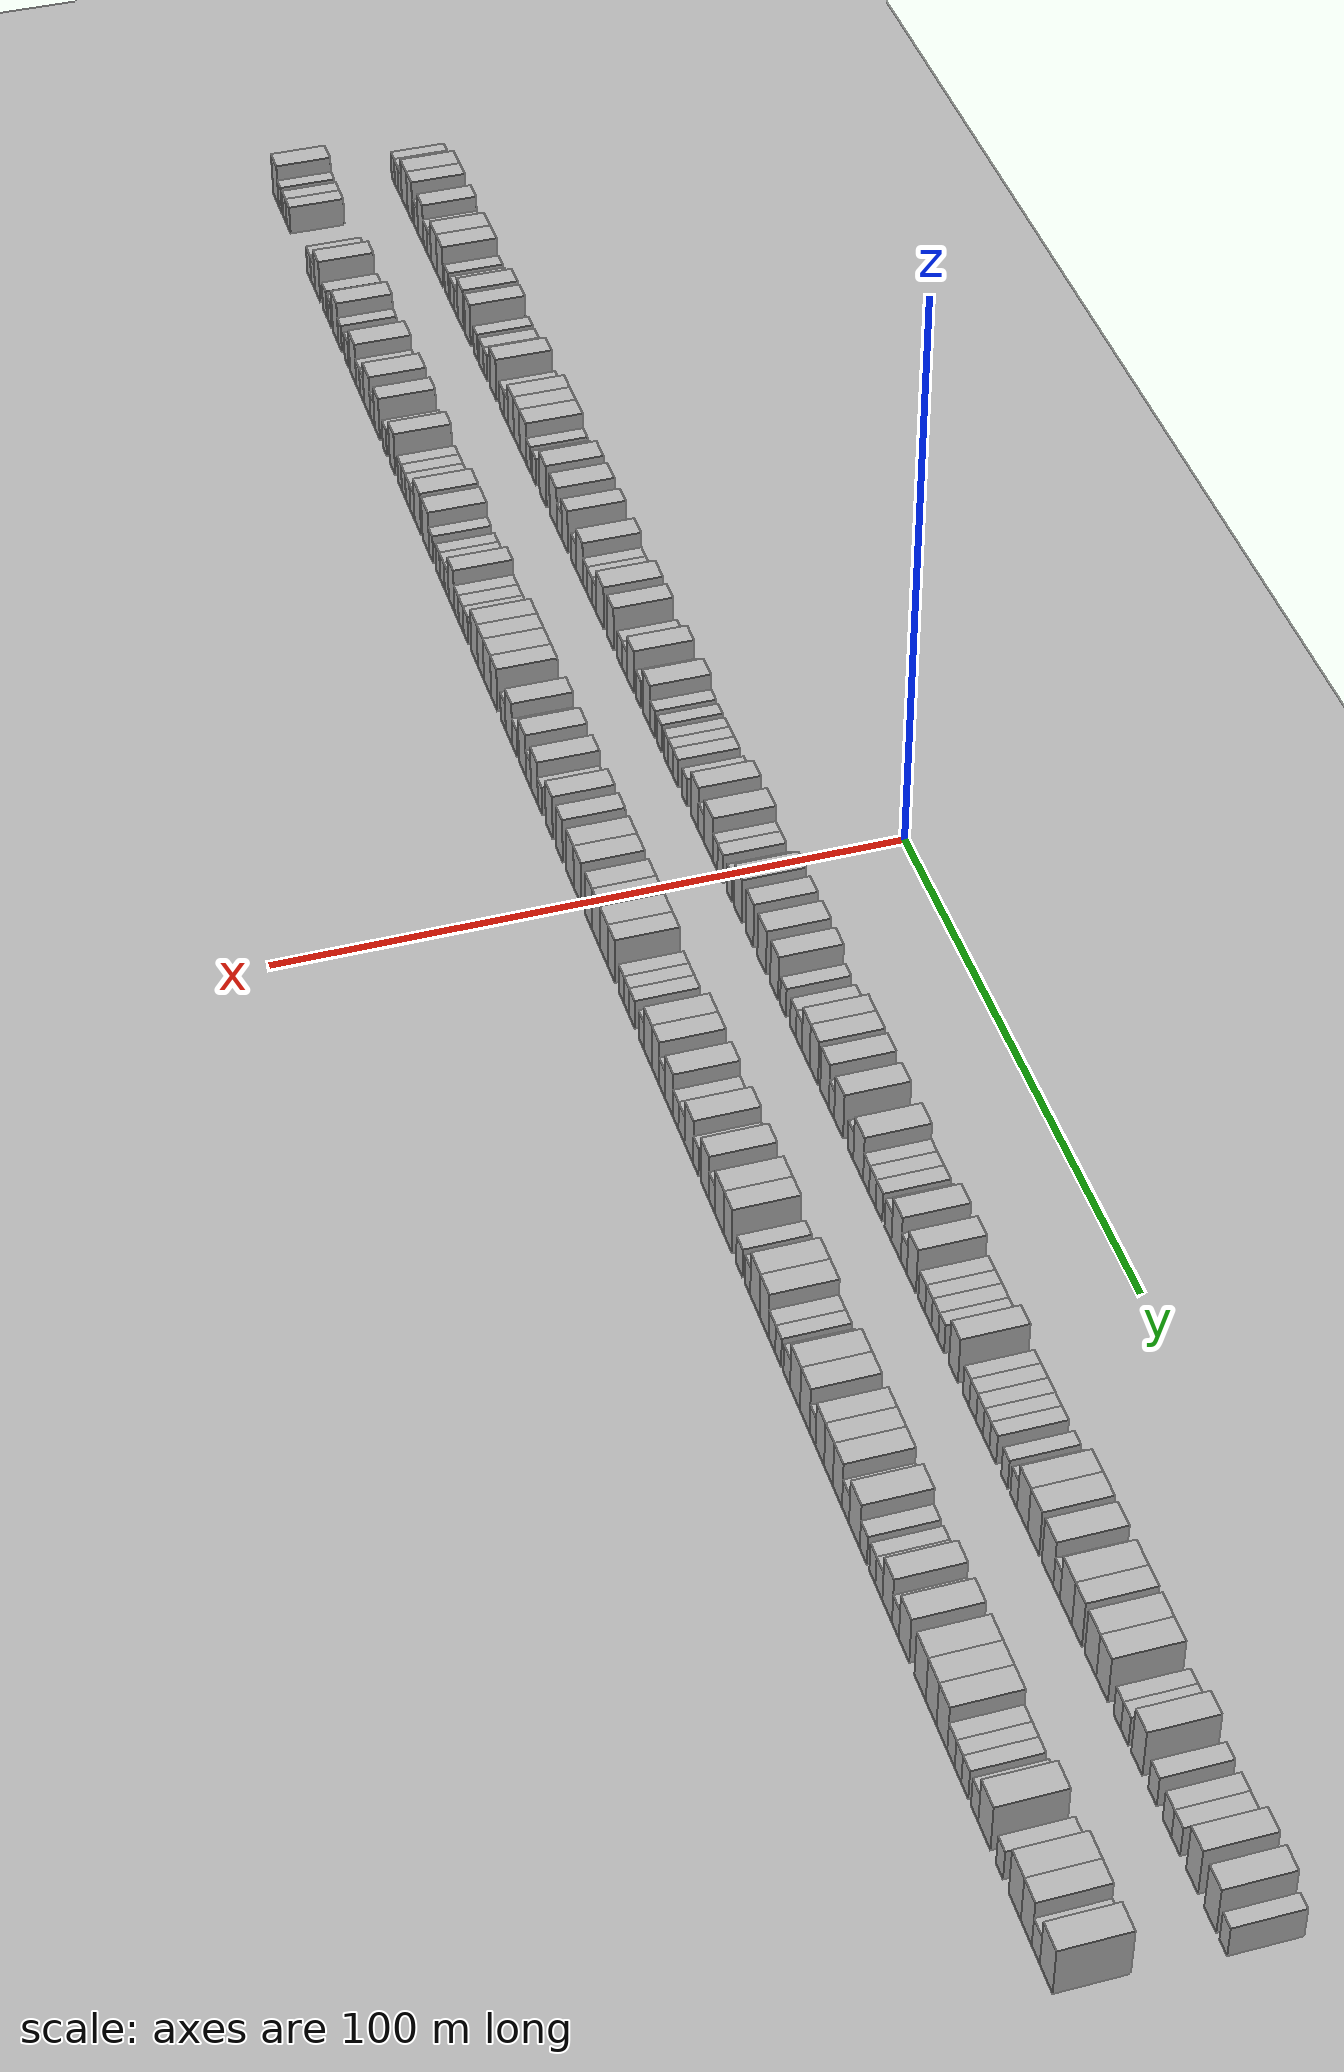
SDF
<?xml version="1.0" encoding="utf-8"?>

<sdf version="1.6">

   <world name="default">

      <gui fullscreen="0">

         <camera name="user_camera">

            <pose>-15 0 4.57585 0 0 0</pose>

            <view_controller>orbit</view_controller>

         </camera>

      </gui>

      <scene>

         <sky>

           <clouds>

             <speed>12</speed>

           </clouds>

         </sky>

         <ambient>0.4 0.4 0.4 1</ambient>

         <background>0.7 0.7 0.7 1</background>

         <shadows>1</shadows>

      </scene>

      <gravity>0 0 -9.8066</gravity>

      <magnetic_field>6e-06 2.3e-05 -4.2e-05</magnetic_field>

      <physics default="0" name="default_physics" type="ode">

         <ode>

            <solver>

               <type>quick</type>

               <iters>10</iters>

               <sor>1.0</sor>

               <use_dynamic_moi_rescaling>0</use_dynamic_moi_rescaling>

            </solver>

            <constraints>

               <cfm>0</cfm>

               <erp>0.2</erp>

               <contact_max_correcting_vel>100</contact_max_correcting_vel>

               <contact_surface_layer>0.001</contact_surface_layer>

            </constraints>

         </ode>

         <max_step_size>0.004</max_step_size>

         <real_time_factor>1</real_time_factor>

         <real_time_update_rate>250</real_time_update_rate>

      </physics>

      <light name="sun" type="directional">

         <cast_shadows>1</cast_shadows>

         <pose>0 0 10 0 0 0</pose>

         <diffuse>0.8 0.8 0.8 1</diffuse>

         <specular>0.2 0.2 0.2 1</specular>

         <attenuation>

            <range>1000</range>

            <constant>0.9</constant>

            <linear>0.01</linear>

            <quadratic>0.001</quadratic>

         </attenuation>

         <direction>-0.5 0.1 -0.9</direction>

      </light>

      <include>

         <name>ground_plane_1</name>

         <uri>model://HANNAS_ground_plane</uri>

         <pose>0 0 0  0 0 0</pose>

      </include>

      <include>

         <name>ground_plane_2</name>

         <uri>model://HANNAS_ground_plane</uri>

         <pose>100 0 0  0 0 0</pose>

      </include>

      <model name="building_1">

         <static>1</static>

         <pose frame="">25.0000 -200.7708 0 0.000000 0.000000 0.000000</pose>

         <link name="link">

            <pose frame="">0 0 3.00 0 0 0</pose>

            <collision name="collision">

               <geometry>

                  <box>

                     <size>10.0000 2.4585 6.0000</size>

                  </box>

               </geometry>

               <max_contacts>10</max_contacts>

               <surface>

                  <contact>

                     <ode/>

                  </contact>

                  <bounce/>

                  <friction>

                     <torsional>

                        <ode/>

                     </torsional>

                     <ode/>

                  </friction>

               </surface>

            </collision>

            <visual name="visual">

               <cast_shadows>0</cast_shadows>

               <geometry>

                  <box>

                     <size>10.0000 2.4585 6.0000</size>

                  </box>

               </geometry>

               <material>

                  <script>

                     <uri>model://HANNAS_wall/materials/scripts</uri>

                     <uri>model://HANNAS_wall/materials/textures</uri>

                     <name>vrc/HANNAS_wall</name>

                  </script>

               </material>

            </visual>

            <self_collide>0</self_collide>

            <enable_wind>0</enable_wind>

            <kinematic>0</kinematic>

         </link>

      </model>

      <model name="building_2">

         <static>1</static>

         <pose frame="">25.0000 -198.2721 0 0.000000 0.000000 0.000000</pose>

         <link name="link">

            <pose frame="">0 0 3.00 0 0 0</pose>

            <collision name="collision">

               <geometry>

                  <box>

                     <size>10.0000 2.5389 6.0000</size>

                  </box>

               </geometry>

               <max_contacts>10</max_contacts>

               <surface>

                  <contact>

                     <ode/>

                  </contact>

                  <bounce/>

                  <friction>

                     <torsional>

                        <ode/>

                     </torsional>

                     <ode/>

                  </friction>

               </surface>

            </collision>

            <visual name="visual">

               <cast_shadows>0</cast_shadows>

               <geometry>

                  <box>

                     <size>10.0000 2.5389 6.0000</size>

                  </box>

               </geometry>

               <material>

                  <script>

                     <uri>model://HANNAS_wall/materials/scripts</uri>

                     <uri>model://HANNAS_wall/materials/textures</uri>

                     <name>vrc/HANNAS_wall</name>

                  </script>

               </material>

            </visual>

            <self_collide>0</self_collide>

            <enable_wind>0</enable_wind>

            <kinematic>0</kinematic>

         </link>

      </model>

      <model name="building_3">

         <static>1</static>

         <pose frame="">25.0000 -195.7499 0 0.000000 0.000000 0.000000</pose>

         <link name="link">

            <pose frame="">0 0 3.00 0 0 0</pose>

            <collision name="collision">

               <geometry>

                  <box>

                     <size>10.0000 2.5055 6.0000</size>

                  </box>

               </geometry>

               <max_contacts>10</max_contacts>

               <surface>

                  <contact>

                     <ode/>

                  </contact>

                  <bounce/>

                  <friction>

                     <torsional>

                        <ode/>

                     </torsional>

                     <ode/>

                  </friction>

               </surface>

            </collision>

            <visual name="visual">

               <cast_shadows>0</cast_shadows>

               <geometry>

                  <box>

                     <size>10.0000 2.5055 6.0000</size>

                  </box>

               </geometry>

               <material>

                  <script>

                     <uri>model://HANNAS_wall/materials/scripts</uri>

                     <uri>model://HANNAS_wall/materials/textures</uri>

                     <name>vrc/HANNAS_wall</name>

                  </script>

               </material>

            </visual>

            <self_collide>0</self_collide>

            <enable_wind>0</enable_wind>

            <kinematic>0</kinematic>

         </link>

      </model>

      <model name="building_4">

         <static>1</static>

         <pose frame="">25.0000 -192.3677 0 0.000000 0.000000 0.000000</pose>

         <link name="link">

            <pose frame="">0 0 4.50 0 0 0</pose>

            <collision name="collision">

               <geometry>

                  <box>

                     <size>10.0000 4.2589 9.0000</size>

                  </box>

               </geometry>

               <max_contacts>10</max_contacts>

               <surface>

                  <contact>

                     <ode/>

                  </contact>

                  <bounce/>

                  <friction>

                     <torsional>

                        <ode/>

                     </torsional>

                     <ode/>

                  </friction>

               </surface>

            </collision>

            <visual name="visual">

               <cast_shadows>0</cast_shadows>

               <geometry>

                  <box>

                     <size>10.0000 4.2589 9.0000</size>

                  </box>

               </geometry>

               <material>

                  <script>

                     <uri>model://HANNAS_wall/materials/scripts</uri>

                     <uri>model://HANNAS_wall/materials/textures</uri>

                     <name>vrc/HANNAS_wall</name>

                  </script>

               </material>

            </visual>

            <self_collide>0</self_collide>

            <enable_wind>0</enable_wind>

            <kinematic>0</kinematic>

         </link>

      </model>

      <model name="building_5">

         <static>1</static>

         <pose frame="">25.0000 -188.3884 0 0.000000 0.000000 0.000000</pose>

         <link name="link">

            <pose frame="">0 0 4.50 0 0 0</pose>

            <collision name="collision">

               <geometry>

                  <box>

                     <size>10.0000 3.6997 9.0000</size>

                  </box>

               </geometry>

               <max_contacts>10</max_contacts>

               <surface>

                  <contact>

                     <ode/>

                  </contact>

                  <bounce/>

                  <friction>

                     <torsional>

                        <ode/>

                     </torsional>

                     <ode/>

                  </friction>

               </surface>

            </collision>

            <visual name="visual">

               <cast_shadows>0</cast_shadows>

               <geometry>

                  <box>

                     <size>10.0000 3.6997 9.0000</size>

                  </box>

               </geometry>

               <material>

                  <script>

                     <uri>model://HANNAS_wall/materials/scripts</uri>

                     <uri>model://HANNAS_wall/materials/textures</uri>

                     <name>vrc/HANNAS_wall</name>

                  </script>

               </material>

            </visual>

            <self_collide>0</self_collide>

            <enable_wind>0</enable_wind>

            <kinematic>0</kinematic>

         </link>

      </model>

      <model name="building_6">

         <static>1</static>

         <pose frame="">25.0000 -184.0949 0 0.000000 0.000000 0.000000</pose>

         <link name="link">

            <pose frame="">0 0 3.00 0 0 0</pose>

            <collision name="collision">

               <geometry>

                  <box>

                     <size>10.0000 2.8872 6.0000</size>

                  </box>

               </geometry>

               <max_contacts>10</max_contacts>

               <surface>

                  <contact>

                     <ode/>

                  </contact>

                  <bounce/>

                  <friction>

                     <torsional>

                        <ode/>

                     </torsional>

                     <ode/>

                  </friction>

               </surface>

            </collision>

            <visual name="visual">

               <cast_shadows>0</cast_shadows>

               <geometry>

                  <box>

                     <size>10.0000 2.8872 6.0000</size>

                  </box>

               </geometry>

               <material>

                  <script>

                     <uri>model://HANNAS_wall/materials/scripts</uri>

                     <uri>model://HANNAS_wall/materials/textures</uri>

                     <name>vrc/HANNAS_wall</name>

                  </script>

               </material>

            </visual>

            <self_collide>0</self_collide>

            <enable_wind>0</enable_wind>

            <kinematic>0</kinematic>

         </link>

      </model>

      <model name="building_7">

         <static>1</static>

         <pose frame="">25.0000 -180.6924 0 0.000000 0.000000 0.000000</pose>

         <link name="link">

            <pose frame="">0 0 4.50 0 0 0</pose>

            <collision name="collision">

               <geometry>

                  <box>

                     <size>10.0000 3.9179 9.0000</size>

                  </box>

               </geometry>

               <max_contacts>10</max_contacts>

               <surface>

                  <contact>

                     <ode/>

                  </contact>

                  <bounce/>

                  <friction>

                     <torsional>

                        <ode/>

                     </torsional>

                     <ode/>

                  </friction>

               </surface>

            </collision>

            <visual name="visual">

               <cast_shadows>0</cast_shadows>

               <geometry>

                  <box>

                     <size>10.0000 3.9179 9.0000</size>

                  </box>

               </geometry>

               <material>

                  <script>

                     <uri>model://HANNAS_wall/materials/scripts</uri>

                     <uri>model://HANNAS_wall/materials/textures</uri>

                     <name>vrc/HANNAS_wall</name>

                  </script>

               </material>

            </visual>

            <self_collide>0</self_collide>

            <enable_wind>0</enable_wind>

            <kinematic>0</kinematic>

         </link>

      </model>

      <model name="building_8">

         <static>1</static>

         <pose frame="">25.0000 -177.3952 0 0.000000 0.000000 0.000000</pose>

         <link name="link">

            <pose frame="">0 0 3.00 0 0 0</pose>

            <collision name="collision">

               <geometry>

                  <box>

                     <size>10.0000 2.6764 6.0000</size>

                  </box>

               </geometry>

               <max_contacts>10</max_contacts>

               <surface>

                  <contact>

                     <ode/>

                  </contact>

                  <bounce/>

                  <friction>

                     <torsional>

                        <ode/>

                     </torsional>

                     <ode/>

                  </friction>

               </surface>

            </collision>

            <visual name="visual">

               <cast_shadows>0</cast_shadows>

               <geometry>

                  <box>

                     <size>10.0000 2.6764 6.0000</size>

                  </box>

               </geometry>

               <material>

                  <script>

                     <uri>model://HANNAS_wall/materials/scripts</uri>

                     <uri>model://HANNAS_wall/materials/textures</uri>

                     <name>vrc/HANNAS_wall</name>

                  </script>

               </material>

            </visual>

            <self_collide>0</self_collide>

            <enable_wind>0</enable_wind>

            <kinematic>0</kinematic>

         </link>

      </model>

      <model name="building_9">

         <static>1</static>

         <pose frame="">25.0000 -174.7308 0 0.000000 0.000000 0.000000</pose>

         <link name="link">

            <pose frame="">0 0 3.00 0 0 0</pose>

            <collision name="collision">

               <geometry>

                  <box>

                     <size>10.0000 2.6524 6.0000</size>

                  </box>

               </geometry>

               <max_contacts>10</max_contacts>

               <surface>

                  <contact>

                     <ode/>

                  </contact>

                  <bounce/>

                  <friction>

                     <torsional>

                        <ode/>

                     </torsional>

                     <ode/>

                  </friction>

               </surface>

            </collision>

            <visual name="visual">

               <cast_shadows>0</cast_shadows>

               <geometry>

                  <box>

                     <size>10.0000 2.6524 6.0000</size>

                  </box>

               </geometry>

               <material>

                  <script>

                     <uri>model://HANNAS_wall/materials/scripts</uri>

                     <uri>model://HANNAS_wall/materials/textures</uri>

                     <name>vrc/HANNAS_wall</name>

                  </script>

               </material>

            </visual>

            <self_collide>0</self_collide>

            <enable_wind>0</enable_wind>

            <kinematic>0</kinematic>

         </link>

      </model>

      <model name="building_10">

         <static>1</static>

         <pose frame="">25.0000 -171.2416 0 0.000000 0.000000 0.000000</pose>

         <link name="link">

            <pose frame="">0 0 4.50 0 0 0</pose>

            <collision name="collision">

               <geometry>

                  <box>

                     <size>10.0000 4.3261 9.0000</size>

                  </box>

               </geometry>

               <max_contacts>10</max_contacts>

               <surface>

                  <contact>

                     <ode/>

                  </contact>

                  <bounce/>

                  <friction>

                     <torsional>

                        <ode/>

                     </torsional>

                     <ode/>

                  </friction>

               </surface>

            </collision>

            <visual name="visual">

               <cast_shadows>0</cast_shadows>

               <geometry>

                  <box>

                     <size>10.0000 4.3261 9.0000</size>

                  </box>

               </geometry>

               <material>

                  <script>

                     <uri>model://HANNAS_wall/materials/scripts</uri>

                     <uri>model://HANNAS_wall/materials/textures</uri>

                     <name>vrc/HANNAS_wall</name>

                  </script>

               </material>

            </visual>

            <self_collide>0</self_collide>

            <enable_wind>0</enable_wind>

            <kinematic>0</kinematic>

         </link>

      </model>

      <model name="building_11">

         <static>1</static>

         <pose frame="">25.0000 -166.9484 0 0.000000 0.000000 0.000000</pose>

         <link name="link">

            <pose frame="">0 0 4.50 0 0 0</pose>

            <collision name="collision">

               <geometry>

                  <box>

                     <size>10.0000 4.2603 9.0000</size>

                  </box>

               </geometry>

               <max_contacts>10</max_contacts>

               <surface>

                  <contact>

                     <ode/>

                  </contact>

                  <bounce/>

                  <friction>

                     <torsional>

                        <ode/>

                     </torsional>

                     <ode/>

                  </friction>

               </surface>

            </collision>

            <visual name="visual">

               <cast_shadows>0</cast_shadows>

               <geometry>

                  <box>

                     <size>10.0000 4.2603 9.0000</size>

                  </box>

               </geometry>

               <material>

                  <script>

                     <uri>model://HANNAS_wall/materials/scripts</uri>

                     <uri>model://HANNAS_wall/materials/textures</uri>

                     <name>vrc/HANNAS_wall</name>

                  </script>

               </material>

            </visual>

            <self_collide>0</self_collide>

            <enable_wind>0</enable_wind>

            <kinematic>0</kinematic>

         </link>

      </model>

      <model name="building_12">

         <static>1</static>

         <pose frame="">25.0000 -162.3492 0 0.000000 0.000000 0.000000</pose>

         <link name="link">

            <pose frame="">0 0 3.00 0 0 0</pose>

            <collision name="collision">

               <geometry>

                  <box>

                     <size>10.0000 2.9381 6.0000</size>

                  </box>

               </geometry>

               <max_contacts>10</max_contacts>

               <surface>

                  <contact>

                     <ode/>

                  </contact>

                  <bounce/>

                  <friction>

                     <torsional>

                        <ode/>

                     </torsional>

                     <ode/>

                  </friction>

               </surface>

            </collision>

            <visual name="visual">

               <cast_shadows>0</cast_shadows>

               <geometry>

                  <box>

                     <size>10.0000 2.9381 6.0000</size>

                  </box>

               </geometry>

               <material>

                  <script>

                     <uri>model://HANNAS_wall/materials/scripts</uri>

                     <uri>model://HANNAS_wall/materials/textures</uri>

                     <name>vrc/HANNAS_wall</name>

                  </script>

               </material>

            </visual>

            <self_collide>0</self_collide>

            <enable_wind>0</enable_wind>

            <kinematic>0</kinematic>

         </link>

      </model>

      <model name="building_13">

         <static>1</static>

         <pose frame="">25.0000 -158.5419 0 0.000000 0.000000 0.000000</pose>

         <link name="link">

            <pose frame="">0 0 3.00 0 0 0</pose>

            <collision name="collision">

               <geometry>

                  <box>

                     <size>10.0000 2.6766 6.0000</size>

                  </box>

               </geometry>

               <max_contacts>10</max_contacts>

               <surface>

                  <contact>

                     <ode/>

                  </contact>

                  <bounce/>

                  <friction>

                     <torsional>

                        <ode/>

                     </torsional>

                     <ode/>

                  </friction>

               </surface>

            </collision>

            <visual name="visual">

               <cast_shadows>0</cast_shadows>

               <geometry>

                  <box>

                     <size>10.0000 2.6766 6.0000</size>

                  </box>

               </geometry>

               <material>

                  <script>

                     <uri>model://HANNAS_wall/materials/scripts</uri>

                     <uri>model://HANNAS_wall/materials/textures</uri>

                     <name>vrc/HANNAS_wall</name>

                  </script>

               </material>

            </visual>

            <self_collide>0</self_collide>

            <enable_wind>0</enable_wind>

            <kinematic>0</kinematic>

         </link>

      </model>

      <model name="building_14">

         <static>1</static>

         <pose frame="">25.0000 -155.9962 0 0.000000 0.000000 0.000000</pose>

         <link name="link">

            <pose frame="">0 0 3.00 0 0 0</pose>

            <collision name="collision">

               <geometry>

                  <box>

                     <size>10.0000 2.4147 6.0000</size>

                  </box>

               </geometry>

               <max_contacts>10</max_contacts>

               <surface>

                  <contact>

                     <ode/>

                  </contact>

                  <bounce/>

                  <friction>

                     <torsional>

                        <ode/>

                     </torsional>

                     <ode/>

                  </friction>

               </surface>

            </collision>

            <visual name="visual">

               <cast_shadows>0</cast_shadows>

               <geometry>

                  <box>

                     <size>10.0000 2.4147 6.0000</size>

                  </box>

               </geometry>

               <material>

                  <script>

                     <uri>model://HANNAS_wall/materials/scripts</uri>

                     <uri>model://HANNAS_wall/materials/textures</uri>

                     <name>vrc/HANNAS_wall</name>

                  </script>

               </material>

            </visual>

            <self_collide>0</self_collide>

            <enable_wind>0</enable_wind>

            <kinematic>0</kinematic>

         </link>

      </model>

      <model name="building_15">

         <static>1</static>

         <pose frame="">25.0000 -152.7614 0 0.000000 0.000000 0.000000</pose>

         <link name="link">

            <pose frame="">0 0 4.50 0 0 0</pose>

            <collision name="collision">

               <geometry>

                  <box>

                     <size>10.0000 4.0549 9.0000</size>

                  </box>

               </geometry>

               <max_contacts>10</max_contacts>

               <surface>

                  <contact>

                     <ode/>

                  </contact>

                  <bounce/>

                  <friction>

                     <torsional>

                        <ode/>

                     </torsional>

                     <ode/>

                  </friction>

               </surface>

            </collision>

            <visual name="visual">

               <cast_shadows>0</cast_shadows>

               <geometry>

                  <box>

                     <size>10.0000 4.0549 9.0000</size>

                  </box>

               </geometry>

               <material>

                  <script>

                     <uri>model://HANNAS_wall/materials/scripts</uri>

                     <uri>model://HANNAS_wall/materials/textures</uri>

                     <name>vrc/HANNAS_wall</name>

                  </script>

               </material>

            </visual>

            <self_collide>0</self_collide>

            <enable_wind>0</enable_wind>

            <kinematic>0</kinematic>

         </link>

      </model>

      <model name="building_16">

         <static>1</static>

         <pose frame="">25.0000 -147.8683 0 0.000000 0.000000 0.000000</pose>

         <link name="link">

            <pose frame="">0 0 4.50 0 0 0</pose>

            <collision name="collision">

               <geometry>

                  <box>

                     <size>10.0000 3.7314 9.0000</size>

                  </box>

               </geometry>

               <max_contacts>10</max_contacts>

               <surface>

                  <contact>

                     <ode/>

                  </contact>

                  <bounce/>

                  <friction>

                     <torsional>

                        <ode/>

                     </torsional>

                     <ode/>

                  </friction>

               </surface>

            </collision>

            <visual name="visual">

               <cast_shadows>0</cast_shadows>

               <geometry>

                  <box>

                     <size>10.0000 3.7314 9.0000</size>

                  </box>

               </geometry>

               <material>

                  <script>

                     <uri>model://HANNAS_wall/materials/scripts</uri>

                     <uri>model://HANNAS_wall/materials/textures</uri>

                     <name>vrc/HANNAS_wall</name>

                  </script>

               </material>

            </visual>

            <self_collide>0</self_collide>

            <enable_wind>0</enable_wind>

            <kinematic>0</kinematic>

         </link>

      </model>

      <model name="building_17">

         <static>1</static>

         <pose frame="">25.0000 -142.6221 0 0.000000 0.000000 0.000000</pose>

         <link name="link">

            <pose frame="">0 0 3.00 0 0 0</pose>

            <collision name="collision">

               <geometry>

                  <box>

                     <size>10.0000 2.7608 6.0000</size>

                  </box>

               </geometry>

               <max_contacts>10</max_contacts>

               <surface>

                  <contact>

                     <ode/>

                  </contact>

                  <bounce/>

                  <friction>

                     <torsional>

                        <ode/>

                     </torsional>

                     <ode/>

                  </friction>

               </surface>

            </collision>

            <visual name="visual">

               <cast_shadows>0</cast_shadows>

               <geometry>

                  <box>

                     <size>10.0000 2.7608 6.0000</size>

                  </box>

               </geometry>

               <material>

                  <script>

                     <uri>model://HANNAS_wall/materials/scripts</uri>

                     <uri>model://HANNAS_wall/materials/textures</uri>

                     <name>vrc/HANNAS_wall</name>

                  </script>

               </material>

            </visual>

            <self_collide>0</self_collide>

            <enable_wind>0</enable_wind>

            <kinematic>0</kinematic>

         </link>

      </model>

      <model name="building_18">

         <static>1</static>

         <pose frame="">25.0000 -138.7657 0 0.000000 0.000000 0.000000</pose>

         <link name="link">

            <pose frame="">0 0 3.00 0 0 0</pose>

            <collision name="collision">

               <geometry>

                  <box>

                     <size>10.0000 2.9520 6.0000</size>

                  </box>

               </geometry>

               <max_contacts>10</max_contacts>

               <surface>

                  <contact>

                     <ode/>

                  </contact>

                  <bounce/>

                  <friction>

                     <torsional>

                        <ode/>

                     </torsional>

                     <ode/>

                  </friction>

               </surface>

            </collision>

            <visual name="visual">

               <cast_shadows>0</cast_shadows>

               <geometry>

                  <box>

                     <size>10.0000 2.9520 6.0000</size>

                  </box>

               </geometry>

               <material>

                  <script>

                     <uri>model://HANNAS_wall/materials/scripts</uri>

                     <uri>model://HANNAS_wall/materials/textures</uri>

                     <name>vrc/HANNAS_wall</name>

                  </script>

               </material>

            </visual>

            <self_collide>0</self_collide>

            <enable_wind>0</enable_wind>

            <kinematic>0</kinematic>

         </link>

      </model>

      <model name="building_19">

         <static>1</static>

         <pose frame="">25.0000 -136.0867 0 0.000000 0.000000 0.000000</pose>

         <link name="link">

            <pose frame="">0 0 3.00 0 0 0</pose>

            <collision name="collision">

               <geometry>

                  <box>

                     <size>10.0000 2.4060 6.0000</size>

                  </box>

               </geometry>

               <max_contacts>10</max_contacts>

               <surface>

                  <contact>

                     <ode/>

                  </contact>

                  <bounce/>

                  <friction>

                     <torsional>

                        <ode/>

                     </torsional>

                     <ode/>

                  </friction>

               </surface>

            </collision>

            <visual name="visual">

               <cast_shadows>0</cast_shadows>

               <geometry>

                  <box>

                     <size>10.0000 2.4060 6.0000</size>

                  </box>

               </geometry>

               <material>

                  <script>

                     <uri>model://HANNAS_wall/materials/scripts</uri>

                     <uri>model://HANNAS_wall/materials/textures</uri>

                     <name>vrc/HANNAS_wall</name>

                  </script>

               </material>

            </visual>

            <self_collide>0</self_collide>

            <enable_wind>0</enable_wind>

            <kinematic>0</kinematic>

         </link>

      </model>

      <model name="building_20">

         <static>1</static>

         <pose frame="">25.0000 -130.8775 0 0.000000 0.000000 0.000000</pose>

         <link name="link">

            <pose frame="">0 0 4.50 0 0 0</pose>

            <collision name="collision">

               <geometry>

                  <box>

                     <size>10.0000 4.0125 9.0000</size>

                  </box>

               </geometry>

               <max_contacts>10</max_contacts>

               <surface>

                  <contact>

                     <ode/>

                  </contact>

                  <bounce/>

                  <friction>

                     <torsional>

                        <ode/>

                     </torsional>

                     <ode/>

                  </friction>

               </surface>

            </collision>

            <visual name="visual">

               <cast_shadows>0</cast_shadows>

               <geometry>

                  <box>

                     <size>10.0000 4.0125 9.0000</size>

                  </box>

               </geometry>

               <material>

                  <script>

                     <uri>model://HANNAS_wall/materials/scripts</uri>

                     <uri>model://HANNAS_wall/materials/textures</uri>

                     <name>vrc/HANNAS_wall</name>

                  </script>

               </material>

            </visual>

            <self_collide>0</self_collide>

            <enable_wind>0</enable_wind>

            <kinematic>0</kinematic>

         </link>

      </model>

      <model name="building_21">

         <static>1</static>

         <pose frame="">25.0000 -125.4084 0 0.000000 0.000000 0.000000</pose>

         <link name="link">

            <pose frame="">0 0 3.00 0 0 0</pose>

            <collision name="collision">

               <geometry>

                  <box>

                     <size>10.0000 2.9255 6.0000</size>

                  </box>

               </geometry>

               <max_contacts>10</max_contacts>

               <surface>

                  <contact>

                     <ode/>

                  </contact>

                  <bounce/>

                  <friction>

                     <torsional>

                        <ode/>

                     </torsional>

                     <ode/>

                  </friction>

               </surface>

            </collision>

            <visual name="visual">

               <cast_shadows>0</cast_shadows>

               <geometry>

                  <box>

                     <size>10.0000 2.9255 6.0000</size>

                  </box>

               </geometry>

               <material>

                  <script>

                     <uri>model://HANNAS_wall/materials/scripts</uri>

                     <uri>model://HANNAS_wall/materials/textures</uri>

                     <name>vrc/HANNAS_wall</name>

                  </script>

               </material>

            </visual>

            <self_collide>0</self_collide>

            <enable_wind>0</enable_wind>

            <kinematic>0</kinematic>

         </link>

      </model>

      <model name="building_22">

         <static>1</static>

         <pose frame="">25.0000 -122.5982 0 0.000000 0.000000 0.000000</pose>

         <link name="link">

            <pose frame="">0 0 3.00 0 0 0</pose>

            <collision name="collision">

               <geometry>

                  <box>

                     <size>10.0000 2.6951 6.0000</size>

                  </box>

               </geometry>

               <max_contacts>10</max_contacts>

               <surface>

                  <contact>

                     <ode/>

                  </contact>

                  <bounce/>

                  <friction>

                     <torsional>

                        <ode/>

                     </torsional>

                     <ode/>

                  </friction>

               </surface>

            </collision>

            <visual name="visual">

               <cast_shadows>0</cast_shadows>

               <geometry>

                  <box>

                     <size>10.0000 2.6951 6.0000</size>

                  </box>

               </geometry>

               <material>

                  <script>

                     <uri>model://HANNAS_wall/materials/scripts</uri>

                     <uri>model://HANNAS_wall/materials/textures</uri>

                     <name>vrc/HANNAS_wall</name>

                  </script>

               </material>

            </visual>

            <self_collide>0</self_collide>

            <enable_wind>0</enable_wind>

            <kinematic>0</kinematic>

         </link>

      </model>

      <model name="building_23">

         <static>1</static>

         <pose frame="">25.0000 -119.4095 0 0.000000 0.000000 0.000000</pose>

         <link name="link">

            <pose frame="">0 0 4.50 0 0 0</pose>

            <collision name="collision">

               <geometry>

                  <box>

                     <size>10.0000 3.6823 9.0000</size>

                  </box>

               </geometry>

               <max_contacts>10</max_contacts>

               <surface>

                  <contact>

                     <ode/>

                  </contact>

                  <bounce/>

                  <friction>

                     <torsional>

                        <ode/>

                     </torsional>

                     <ode/>

                  </friction>

               </surface>

            </collision>

            <visual name="visual">

               <cast_shadows>0</cast_shadows>

               <geometry>

                  <box>

                     <size>10.0000 3.6823 9.0000</size>

                  </box>

               </geometry>

               <material>

                  <script>

                     <uri>model://HANNAS_wall/materials/scripts</uri>

                     <uri>model://HANNAS_wall/materials/textures</uri>

                     <name>vrc/HANNAS_wall</name>

                  </script>

               </material>

            </visual>

            <self_collide>0</self_collide>

            <enable_wind>0</enable_wind>

            <kinematic>0</kinematic>

         </link>

      </model>

      <model name="building_24">

         <static>1</static>

         <pose frame="">25.0000 -115.6903 0 0.000000 0.000000 0.000000</pose>

         <link name="link">

            <pose frame="">0 0 4.50 0 0 0</pose>

            <collision name="collision">

               <geometry>

                  <box>

                     <size>10.0000 3.7561 9.0000</size>

                  </box>

               </geometry>

               <max_contacts>10</max_contacts>

               <surface>

                  <contact>

                     <ode/>

                  </contact>

                  <bounce/>

                  <friction>

                     <torsional>

                        <ode/>

                     </torsional>

                     <ode/>

                  </friction>

               </surface>

            </collision>

            <visual name="visual">

               <cast_shadows>0</cast_shadows>

               <geometry>

                  <box>

                     <size>10.0000 3.7561 9.0000</size>

                  </box>

               </geometry>

               <material>

                  <script>

                     <uri>model://HANNAS_wall/materials/scripts</uri>

                     <uri>model://HANNAS_wall/materials/textures</uri>

                     <name>vrc/HANNAS_wall</name>

                  </script>

               </material>

            </visual>

            <self_collide>0</self_collide>

            <enable_wind>0</enable_wind>

            <kinematic>0</kinematic>

         </link>

      </model>

      <model name="building_25">

         <static>1</static>

         <pose frame="">25.0000 -111.6862 0 0.000000 0.000000 0.000000</pose>

         <link name="link">

            <pose frame="">0 0 4.50 0 0 0</pose>

            <collision name="collision">

               <geometry>

                  <box>

                     <size>10.0000 4.2523 9.0000</size>

                  </box>

               </geometry>

               <max_contacts>10</max_contacts>

               <surface>

                  <contact>

                     <ode/>

                  </contact>

                  <bounce/>

                  <friction>

                     <torsional>

                        <ode/>

                     </torsional>

                     <ode/>

                  </friction>

               </surface>

            </collision>

            <visual name="visual">

               <cast_shadows>0</cast_shadows>

               <geometry>

                  <box>

                     <size>10.0000 4.2523 9.0000</size>

                  </box>

               </geometry>

               <material>

                  <script>

                     <uri>model://HANNAS_wall/materials/scripts</uri>

                     <uri>model://HANNAS_wall/materials/textures</uri>

                     <name>vrc/HANNAS_wall</name>

                  </script>

               </material>

            </visual>

            <self_collide>0</self_collide>

            <enable_wind>0</enable_wind>

            <kinematic>0</kinematic>

         </link>

      </model>

      <model name="building_26">

         <static>1</static>

         <pose frame="">25.0000 -108.2138 0 0.000000 0.000000 0.000000</pose>

         <link name="link">

            <pose frame="">0 0 3.00 0 0 0</pose>

            <collision name="collision">

               <geometry>

                  <box>

                     <size>10.0000 2.6924 6.0000</size>

                  </box>

               </geometry>

               <max_contacts>10</max_contacts>

               <surface>

                  <contact>

                     <ode/>

                  </contact>

                  <bounce/>

                  <friction>

                     <torsional>

                        <ode/>

                     </torsional>

                     <ode/>

                  </friction>

               </surface>

            </collision>

            <visual name="visual">

               <cast_shadows>0</cast_shadows>

               <geometry>

                  <box>

                     <size>10.0000 2.6924 6.0000</size>

                  </box>

               </geometry>

               <material>

                  <script>

                     <uri>model://HANNAS_wall/materials/scripts</uri>

                     <uri>model://HANNAS_wall/materials/textures</uri>

                     <name>vrc/HANNAS_wall</name>

                  </script>

               </material>

            </visual>

            <self_collide>0</self_collide>

            <enable_wind>0</enable_wind>

            <kinematic>0</kinematic>

         </link>

      </model>

      <model name="building_27">

         <static>1</static>

         <pose frame="">25.0000 -104.6309 0 0.000000 0.000000 0.000000</pose>

         <link name="link">

            <pose frame="">0 0 3.00 0 0 0</pose>

            <collision name="collision">

               <geometry>

                  <box>

                     <size>10.0000 2.4735 6.0000</size>

                  </box>

               </geometry>

               <max_contacts>10</max_contacts>

               <surface>

                  <contact>

                     <ode/>

                  </contact>

                  <bounce/>

                  <friction>

                     <torsional>

                        <ode/>

                     </torsional>

                     <ode/>

                  </friction>

               </surface>

            </collision>

            <visual name="visual">

               <cast_shadows>0</cast_shadows>

               <geometry>

                  <box>

                     <size>10.0000 2.4735 6.0000</size>

                  </box>

               </geometry>

               <material>

                  <script>

                     <uri>model://HANNAS_wall/materials/scripts</uri>

                     <uri>model://HANNAS_wall/materials/textures</uri>

                     <name>vrc/HANNAS_wall</name>

                  </script>

               </material>

            </visual>

            <self_collide>0</self_collide>

            <enable_wind>0</enable_wind>

            <kinematic>0</kinematic>

         </link>

      </model>

      <model name="building_28">

         <static>1</static>

         <pose frame="">25.0000 -99.2087 0 0.000000 0.000000 0.000000</pose>

         <link name="link">

            <pose frame="">0 0 4.50 0 0 0</pose>

            <collision name="collision">

               <geometry>

                  <box>

                     <size>10.0000 4.3710 9.0000</size>

                  </box>

               </geometry>

               <max_contacts>10</max_contacts>

               <surface>

                  <contact>

                     <ode/>

                  </contact>

                  <bounce/>

                  <friction>

                     <torsional>

                        <ode/>

                     </torsional>

                     <ode/>

                  </friction>

               </surface>

            </collision>

            <visual name="visual">

               <cast_shadows>0</cast_shadows>

               <geometry>

                  <box>

                     <size>10.0000 4.3710 9.0000</size>

                  </box>

               </geometry>

               <material>

                  <script>

                     <uri>model://HANNAS_wall/materials/scripts</uri>

                     <uri>model://HANNAS_wall/materials/textures</uri>

                     <name>vrc/HANNAS_wall</name>

                  </script>

               </material>

            </visual>

            <self_collide>0</self_collide>

            <enable_wind>0</enable_wind>

            <kinematic>0</kinematic>

         </link>

      </model>

      <model name="building_29">

         <static>1</static>

         <pose frame="">25.0000 -92.8101 0 0.000000 0.000000 0.000000</pose>

         <link name="link">

            <pose frame="">0 0 4.50 0 0 0</pose>

            <collision name="collision">

               <geometry>

                  <box>

                     <size>10.0000 4.4262 9.0000</size>

                  </box>

               </geometry>

               <max_contacts>10</max_contacts>

               <surface>

                  <contact>

                     <ode/>

                  </contact>

                  <bounce/>

                  <friction>

                     <torsional>

                        <ode/>

                     </torsional>

                     <ode/>

                  </friction>

               </surface>

            </collision>

            <visual name="visual">

               <cast_shadows>0</cast_shadows>

               <geometry>

                  <box>

                     <size>10.0000 4.4262 9.0000</size>

                  </box>

               </geometry>

               <material>

                  <script>

                     <uri>model://HANNAS_wall/materials/scripts</uri>

                     <uri>model://HANNAS_wall/materials/textures</uri>

                     <name>vrc/HANNAS_wall</name>

                  </script>

               </material>

            </visual>

            <self_collide>0</self_collide>

            <enable_wind>0</enable_wind>

            <kinematic>0</kinematic>

         </link>

      </model>

      <model name="building_30">

         <static>1</static>

         <pose frame="">25.0000 -89.0975 0 0.000000 0.000000 0.000000</pose>

         <link name="link">

            <pose frame="">0 0 3.00 0 0 0</pose>

            <collision name="collision">

               <geometry>

                  <box>

                     <size>10.0000 2.9989 6.0000</size>

                  </box>

               </geometry>

               <max_contacts>10</max_contacts>

               <surface>

                  <contact>

                     <ode/>

                  </contact>

                  <bounce/>

                  <friction>

                     <torsional>

                        <ode/>

                     </torsional>

                     <ode/>

                  </friction>

               </surface>

            </collision>

            <visual name="visual">

               <cast_shadows>0</cast_shadows>

               <geometry>

                  <box>

                     <size>10.0000 2.9989 6.0000</size>

                  </box>

               </geometry>

               <material>

                  <script>

                     <uri>model://HANNAS_wall/materials/scripts</uri>

                     <uri>model://HANNAS_wall/materials/textures</uri>

                     <name>vrc/HANNAS_wall</name>

                  </script>

               </material>

            </visual>

            <self_collide>0</self_collide>

            <enable_wind>0</enable_wind>

            <kinematic>0</kinematic>

         </link>

      </model>

      <model name="building_31">

         <static>1</static>

         <pose frame="">25.0000 -85.7972 0 0.000000 0.000000 0.000000</pose>

         <link name="link">

            <pose frame="">0 0 4.50 0 0 0</pose>

            <collision name="collision">

               <geometry>

                  <box>

                     <size>10.0000 3.6017 9.0000</size>

                  </box>

               </geometry>

               <max_contacts>10</max_contacts>

               <surface>

                  <contact>

                     <ode/>

                  </contact>

                  <bounce/>

                  <friction>

                     <torsional>

                        <ode/>

                     </torsional>

                     <ode/>

                  </friction>

               </surface>

            </collision>

            <visual name="visual">

               <cast_shadows>0</cast_shadows>

               <geometry>

                  <box>

                     <size>10.0000 3.6017 9.0000</size>

                  </box>

               </geometry>

               <material>

                  <script>

                     <uri>model://HANNAS_wall/materials/scripts</uri>

                     <uri>model://HANNAS_wall/materials/textures</uri>

                     <name>vrc/HANNAS_wall</name>

                  </script>

               </material>

            </visual>

            <self_collide>0</self_collide>

            <enable_wind>0</enable_wind>

            <kinematic>0</kinematic>

         </link>

      </model>

      <model name="building_32">

         <static>1</static>

         <pose frame="">25.0000 -80.5384 0 0.000000 0.000000 0.000000</pose>

         <link name="link">

            <pose frame="">0 0 3.00 0 0 0</pose>

            <collision name="collision">

               <geometry>

                  <box>

                     <size>10.0000 2.9159 6.0000</size>

                  </box>

               </geometry>

               <max_contacts>10</max_contacts>

               <surface>

                  <contact>

                     <ode/>

                  </contact>

                  <bounce/>

                  <friction>

                     <torsional>

                        <ode/>

                     </torsional>

                     <ode/>

                  </friction>

               </surface>

            </collision>

            <visual name="visual">

               <cast_shadows>0</cast_shadows>

               <geometry>

                  <box>

                     <size>10.0000 2.9159 6.0000</size>

                  </box>

               </geometry>

               <material>

                  <script>

                     <uri>model://HANNAS_wall/materials/scripts</uri>

                     <uri>model://HANNAS_wall/materials/textures</uri>

                     <name>vrc/HANNAS_wall</name>

                  </script>

               </material>

            </visual>

            <self_collide>0</self_collide>

            <enable_wind>0</enable_wind>

            <kinematic>0</kinematic>

         </link>

      </model>

      <model name="building_33">

         <static>1</static>

         <pose frame="">25.0000 -77.0380 0 0.000000 0.000000 0.000000</pose>

         <link name="link">

            <pose frame="">0 0 4.50 0 0 0</pose>

            <collision name="collision">

               <geometry>

                  <box>

                     <size>10.0000 4.0849 9.0000</size>

                  </box>

               </geometry>

               <max_contacts>10</max_contacts>

               <surface>

                  <contact>

                     <ode/>

                  </contact>

                  <bounce/>

                  <friction>

                     <torsional>

                        <ode/>

                     </torsional>

                     <ode/>

                  </friction>

               </surface>

            </collision>

            <visual name="visual">

               <cast_shadows>0</cast_shadows>

               <geometry>

                  <box>

                     <size>10.0000 4.0849 9.0000</size>

                  </box>

               </geometry>

               <material>

                  <script>

                     <uri>model://HANNAS_wall/materials/scripts</uri>

                     <uri>model://HANNAS_wall/materials/textures</uri>

                     <name>vrc/HANNAS_wall</name>

                  </script>

               </material>

            </visual>

            <self_collide>0</self_collide>

            <enable_wind>0</enable_wind>

            <kinematic>0</kinematic>

         </link>

      </model>

      <model name="building_34">

         <static>1</static>

         <pose frame="">25.0000 -73.7491 0 0.000000 0.000000 0.000000</pose>

         <link name="link">

            <pose frame="">0 0 3.00 0 0 0</pose>

            <collision name="collision">

               <geometry>

                  <box>

                     <size>10.0000 2.4927 6.0000</size>

                  </box>

               </geometry>

               <max_contacts>10</max_contacts>

               <surface>

                  <contact>

                     <ode/>

                  </contact>

                  <bounce/>

                  <friction>

                     <torsional>

                        <ode/>

                     </torsional>

                     <ode/>

                  </friction>

               </surface>

            </collision>

            <visual name="visual">

               <cast_shadows>0</cast_shadows>

               <geometry>

                  <box>

                     <size>10.0000 2.4927 6.0000</size>

                  </box>

               </geometry>

               <material>

                  <script>

                     <uri>model://HANNAS_wall/materials/scripts</uri>

                     <uri>model://HANNAS_wall/materials/textures</uri>

                     <name>vrc/HANNAS_wall</name>

                  </script>

               </material>

            </visual>

            <self_collide>0</self_collide>

            <enable_wind>0</enable_wind>

            <kinematic>0</kinematic>

         </link>

      </model>

      <model name="building_35">

         <static>1</static>

         <pose frame="">25.0000 -71.1056 0 0.000000 0.000000 0.000000</pose>

         <link name="link">

            <pose frame="">0 0 3.00 0 0 0</pose>

            <collision name="collision">

               <geometry>

                  <box>

                     <size>10.0000 2.7944 6.0000</size>

                  </box>

               </geometry>

               <max_contacts>10</max_contacts>

               <surface>

                  <contact>

                     <ode/>

                  </contact>

                  <bounce/>

                  <friction>

                     <torsional>

                        <ode/>

                     </torsional>

                     <ode/>

                  </friction>

               </surface>

            </collision>

            <visual name="visual">

               <cast_shadows>0</cast_shadows>

               <geometry>

                  <box>

                     <size>10.0000 2.7944 6.0000</size>

                  </box>

               </geometry>

               <material>

                  <script>

                     <uri>model://HANNAS_wall/materials/scripts</uri>

                     <uri>model://HANNAS_wall/materials/textures</uri>

                     <name>vrc/HANNAS_wall</name>

                  </script>

               </material>

            </visual>

            <self_collide>0</self_collide>

            <enable_wind>0</enable_wind>

            <kinematic>0</kinematic>

         </link>

      </model>

      <model name="building_36">

         <static>1</static>

         <pose frame="">25.0000 -68.4861 0 0.000000 0.000000 0.000000</pose>

         <link name="link">

            <pose frame="">0 0 3.00 0 0 0</pose>

            <collision name="collision">

               <geometry>

                  <box>

                     <size>10.0000 2.4445 6.0000</size>

                  </box>

               </geometry>

               <max_contacts>10</max_contacts>

               <surface>

                  <contact>

                     <ode/>

                  </contact>

                  <bounce/>

                  <friction>

                     <torsional>

                        <ode/>

                     </torsional>

                     <ode/>

                  </friction>

               </surface>

            </collision>

            <visual name="visual">

               <cast_shadows>0</cast_shadows>

               <geometry>

                  <box>

                     <size>10.0000 2.4445 6.0000</size>

                  </box>

               </geometry>

               <material>

                  <script>

                     <uri>model://HANNAS_wall/materials/scripts</uri>

                     <uri>model://HANNAS_wall/materials/textures</uri>

                     <name>vrc/HANNAS_wall</name>

                  </script>

               </material>

            </visual>

            <self_collide>0</self_collide>

            <enable_wind>0</enable_wind>

            <kinematic>0</kinematic>

         </link>

      </model>

      <model name="building_37">

         <static>1</static>

         <pose frame="">25.0000 -65.0238 0 0.000000 0.000000 0.000000</pose>

         <link name="link">

            <pose frame="">0 0 4.50 0 0 0</pose>

            <collision name="collision">

               <geometry>

                  <box>

                     <size>10.0000 4.4801 9.0000</size>

                  </box>

               </geometry>

               <max_contacts>10</max_contacts>

               <surface>

                  <contact>

                     <ode/>

                  </contact>

                  <bounce/>

                  <friction>

                     <torsional>

                        <ode/>

                     </torsional>

                     <ode/>

                  </friction>

               </surface>

            </collision>

            <visual name="visual">

               <cast_shadows>0</cast_shadows>

               <geometry>

                  <box>

                     <size>10.0000 4.4801 9.0000</size>

                  </box>

               </geometry>

               <material>

                  <script>

                     <uri>model://HANNAS_wall/materials/scripts</uri>

                     <uri>model://HANNAS_wall/materials/textures</uri>

                     <name>vrc/HANNAS_wall</name>

                  </script>

               </material>

            </visual>

            <self_collide>0</self_collide>

            <enable_wind>0</enable_wind>

            <kinematic>0</kinematic>

         </link>

      </model>

      <model name="building_38">

         <static>1</static>

         <pose frame="">25.0000 -58.9223 0 0.000000 0.000000 0.000000</pose>

         <link name="link">

            <pose frame="">0 0 4.50 0 0 0</pose>

            <collision name="collision">

               <geometry>

                  <box>

                     <size>10.0000 3.7229 9.0000</size>

                  </box>

               </geometry>

               <max_contacts>10</max_contacts>

               <surface>

                  <contact>

                     <ode/>

                  </contact>

                  <bounce/>

                  <friction>

                     <torsional>

                        <ode/>

                     </torsional>

                     <ode/>

                  </friction>

               </surface>

            </collision>

            <visual name="visual">

               <cast_shadows>0</cast_shadows>

               <geometry>

                  <box>

                     <size>10.0000 3.7229 9.0000</size>

                  </box>

               </geometry>

               <material>

                  <script>

                     <uri>model://HANNAS_wall/materials/scripts</uri>

                     <uri>model://HANNAS_wall/materials/textures</uri>

                     <name>vrc/HANNAS_wall</name>

                  </script>

               </material>

            </visual>

            <self_collide>0</self_collide>

            <enable_wind>0</enable_wind>

            <kinematic>0</kinematic>

         </link>

      </model>

      <model name="building_39">

         <static>1</static>

         <pose frame="">25.0000 -53.6632 0 0.000000 0.000000 0.000000</pose>

         <link name="link">

            <pose frame="">0 0 3.00 0 0 0</pose>

            <collision name="collision">

               <geometry>

                  <box>

                     <size>10.0000 2.7953 6.0000</size>

                  </box>

               </geometry>

               <max_contacts>10</max_contacts>

               <surface>

                  <contact>

                     <ode/>

                  </contact>

                  <bounce/>

                  <friction>

                     <torsional>

                        <ode/>

                     </torsional>

                     <ode/>

                  </friction>

               </surface>

            </collision>

            <visual name="visual">

               <cast_shadows>0</cast_shadows>

               <geometry>

                  <box>

                     <size>10.0000 2.7953 6.0000</size>

                  </box>

               </geometry>

               <material>

                  <script>

                     <uri>model://HANNAS_wall/materials/scripts</uri>

                     <uri>model://HANNAS_wall/materials/textures</uri>

                     <name>vrc/HANNAS_wall</name>

                  </script>

               </material>

            </visual>

            <self_collide>0</self_collide>

            <enable_wind>0</enable_wind>

            <kinematic>0</kinematic>

         </link>

      </model>

      <model name="building_40">

         <static>1</static>

         <pose frame="">25.0000 -50.9100 0 0.000000 0.000000 0.000000</pose>

         <link name="link">

            <pose frame="">0 0 3.00 0 0 0</pose>

            <collision name="collision">

               <geometry>

                  <box>

                     <size>10.0000 2.7112 6.0000</size>

                  </box>

               </geometry>

               <max_contacts>10</max_contacts>

               <surface>

                  <contact>

                     <ode/>

                  </contact>

                  <bounce/>

                  <friction>

                     <torsional>

                        <ode/>

                     </torsional>

                     <ode/>

                  </friction>

               </surface>

            </collision>

            <visual name="visual">

               <cast_shadows>0</cast_shadows>

               <geometry>

                  <box>

                     <size>10.0000 2.7112 6.0000</size>

                  </box>

               </geometry>

               <material>

                  <script>

                     <uri>model://HANNAS_wall/materials/scripts</uri>

                     <uri>model://HANNAS_wall/materials/textures</uri>

                     <name>vrc/HANNAS_wall</name>

                  </script>

               </material>

            </visual>

            <self_collide>0</self_collide>

            <enable_wind>0</enable_wind>

            <kinematic>0</kinematic>

         </link>

      </model>

      <model name="building_41">

         <static>1</static>

         <pose frame="">25.0000 -47.5943 0 0.000000 0.000000 0.000000</pose>

         <link name="link">

            <pose frame="">0 0 4.50 0 0 0</pose>

            <collision name="collision">

               <geometry>

                  <box>

                     <size>10.0000 3.9201 9.0000</size>

                  </box>

               </geometry>

               <max_contacts>10</max_contacts>

               <surface>

                  <contact>

                     <ode/>

                  </contact>

                  <bounce/>

                  <friction>

                     <torsional>

                        <ode/>

                     </torsional>

                     <ode/>

                  </friction>

               </surface>

            </collision>

            <visual name="visual">

               <cast_shadows>0</cast_shadows>

               <geometry>

                  <box>

                     <size>10.0000 3.9201 9.0000</size>

                  </box>

               </geometry>

               <material>

                  <script>

                     <uri>model://HANNAS_wall/materials/scripts</uri>

                     <uri>model://HANNAS_wall/materials/textures</uri>

                     <name>vrc/HANNAS_wall</name>

                  </script>

               </material>

            </visual>

            <self_collide>0</self_collide>

            <enable_wind>0</enable_wind>

            <kinematic>0</kinematic>

         </link>

      </model>

      <model name="building_42">

         <static>1</static>

         <pose frame="">25.0000 -43.2173 0 0.000000 0.000000 0.000000</pose>

         <link name="link">

            <pose frame="">0 0 3.00 0 0 0</pose>

            <collision name="collision">

               <geometry>

                  <box>

                     <size>10.0000 2.8340 6.0000</size>

                  </box>

               </geometry>

               <max_contacts>10</max_contacts>

               <surface>

                  <contact>

                     <ode/>

                  </contact>

                  <bounce/>

                  <friction>

                     <torsional>

                        <ode/>

                     </torsional>

                     <ode/>

                  </friction>

               </surface>

            </collision>

            <visual name="visual">

               <cast_shadows>0</cast_shadows>

               <geometry>

                  <box>

                     <size>10.0000 2.8340 6.0000</size>

                  </box>

               </geometry>

               <material>

                  <script>

                     <uri>model://HANNAS_wall/materials/scripts</uri>

                     <uri>model://HANNAS_wall/materials/textures</uri>

                     <name>vrc/HANNAS_wall</name>

                  </script>

               </material>

            </visual>

            <self_collide>0</self_collide>

            <enable_wind>0</enable_wind>

            <kinematic>0</kinematic>

         </link>

      </model>

      <model name="building_43">

         <static>1</static>

         <pose frame="">25.0000 -38.6932 0 0.000000 0.000000 0.000000</pose>

         <link name="link">

            <pose frame="">0 0 4.50 0 0 0</pose>

            <collision name="collision">

               <geometry>

                  <box>

                     <size>10.0000 4.2141 9.0000</size>

                  </box>

               </geometry>

               <max_contacts>10</max_contacts>

               <surface>

                  <contact>

                     <ode/>

                  </contact>

                  <bounce/>

                  <friction>

                     <torsional>

                        <ode/>

                     </torsional>

                     <ode/>

                  </friction>

               </surface>

            </collision>

            <visual name="visual">

               <cast_shadows>0</cast_shadows>

               <geometry>

                  <box>

                     <size>10.0000 4.2141 9.0000</size>

                  </box>

               </geometry>

               <material>

                  <script>

                     <uri>model://HANNAS_wall/materials/scripts</uri>

                     <uri>model://HANNAS_wall/materials/textures</uri>

                     <name>vrc/HANNAS_wall</name>

                  </script>

               </material>

            </visual>

            <self_collide>0</self_collide>

            <enable_wind>0</enable_wind>

            <kinematic>0</kinematic>

         </link>

      </model>

      <model name="building_44">

         <static>1</static>

         <pose frame="">25.0000 -35.2384 0 0.000000 0.000000 0.000000</pose>

         <link name="link">

            <pose frame="">0 0 3.00 0 0 0</pose>

            <collision name="collision">

               <geometry>

                  <box>

                     <size>10.0000 2.6955 6.0000</size>

                  </box>

               </geometry>

               <max_contacts>10</max_contacts>

               <surface>

                  <contact>

                     <ode/>

                  </contact>

                  <bounce/>

                  <friction>

                     <torsional>

                        <ode/>

                     </torsional>

                     <ode/>

                  </friction>

               </surface>

            </collision>

            <visual name="visual">

               <cast_shadows>0</cast_shadows>

               <geometry>

                  <box>

                     <size>10.0000 2.6955 6.0000</size>

                  </box>

               </geometry>

               <material>

                  <script>

                     <uri>model://HANNAS_wall/materials/scripts</uri>

                     <uri>model://HANNAS_wall/materials/textures</uri>

                     <name>vrc/HANNAS_wall</name>

                  </script>

               </material>

            </visual>

            <self_collide>0</self_collide>

            <enable_wind>0</enable_wind>

            <kinematic>0</kinematic>

         </link>

      </model>

      <model name="building_45">

         <static>1</static>

         <pose frame="">25.0000 -31.6136 0 0.000000 0.000000 0.000000</pose>

         <link name="link">

            <pose frame="">0 0 3.00 0 0 0</pose>

            <collision name="collision">

               <geometry>

                  <box>

                     <size>10.0000 2.5543 6.0000</size>

                  </box>

               </geometry>

               <max_contacts>10</max_contacts>

               <surface>

                  <contact>

                     <ode/>

                  </contact>

                  <bounce/>

                  <friction>

                     <torsional>

                        <ode/>

                     </torsional>

                     <ode/>

                  </friction>

               </surface>

            </collision>

            <visual name="visual">

               <cast_shadows>0</cast_shadows>

               <geometry>

                  <box>

                     <size>10.0000 2.5543 6.0000</size>

                  </box>

               </geometry>

               <material>

                  <script>

                     <uri>model://HANNAS_wall/materials/scripts</uri>

                     <uri>model://HANNAS_wall/materials/textures</uri>

                     <name>vrc/HANNAS_wall</name>

                  </script>

               </material>

            </visual>

            <self_collide>0</self_collide>

            <enable_wind>0</enable_wind>

            <kinematic>0</kinematic>

         </link>

      </model>

      <model name="building_46">

         <static>1</static>

         <pose frame="">25.0000 -28.1310 0 0.000000 0.000000 0.000000</pose>

         <link name="link">

            <pose frame="">0 0 3.00 0 0 0</pose>

            <collision name="collision">

               <geometry>

                  <box>

                     <size>10.0000 2.4108 6.0000</size>

                  </box>

               </geometry>

               <max_contacts>10</max_contacts>

               <surface>

                  <contact>

                     <ode/>

                  </contact>

                  <bounce/>

                  <friction>

                     <torsional>

                        <ode/>

                     </torsional>

                     <ode/>

                  </friction>

               </surface>

            </collision>

            <visual name="visual">

               <cast_shadows>0</cast_shadows>

               <geometry>

                  <box>

                     <size>10.0000 2.4108 6.0000</size>

                  </box>

               </geometry>

               <material>

                  <script>

                     <uri>model://HANNAS_wall/materials/scripts</uri>

                     <uri>model://HANNAS_wall/materials/textures</uri>

                     <name>vrc/HANNAS_wall</name>

                  </script>

               </material>

            </visual>

            <self_collide>0</self_collide>

            <enable_wind>0</enable_wind>

            <kinematic>0</kinematic>

         </link>

      </model>

      <model name="building_47">

         <static>1</static>

         <pose frame="">25.0000 -25.6795 0 0.000000 0.000000 0.000000</pose>

         <link name="link">

            <pose frame="">0 0 3.00 0 0 0</pose>

            <collision name="collision">

               <geometry>

                  <box>

                     <size>10.0000 2.4922 6.0000</size>

                  </box>

               </geometry>

               <max_contacts>10</max_contacts>

               <surface>

                  <contact>

                     <ode/>

                  </contact>

                  <bounce/>

                  <friction>

                     <torsional>

                        <ode/>

                     </torsional>

                     <ode/>

                  </friction>

               </surface>

            </collision>

            <visual name="visual">

               <cast_shadows>0</cast_shadows>

               <geometry>

                  <box>

                     <size>10.0000 2.4922 6.0000</size>

                  </box>

               </geometry>

               <material>

                  <script>

                     <uri>model://HANNAS_wall/materials/scripts</uri>

                     <uri>model://HANNAS_wall/materials/textures</uri>

                     <name>vrc/HANNAS_wall</name>

                  </script>

               </material>

            </visual>

            <self_collide>0</self_collide>

            <enable_wind>0</enable_wind>

            <kinematic>0</kinematic>

         </link>

      </model>

      <model name="building_48">

         <static>1</static>

         <pose frame="">25.0000 -22.9481 0 0.000000 0.000000 0.000000</pose>

         <link name="link">

            <pose frame="">0 0 3.00 0 0 0</pose>

            <collision name="collision">

               <geometry>

                  <box>

                     <size>10.0000 2.9707 6.0000</size>

                  </box>

               </geometry>

               <max_contacts>10</max_contacts>

               <surface>

                  <contact>

                     <ode/>

                  </contact>

                  <bounce/>

                  <friction>

                     <torsional>

                        <ode/>

                     </torsional>

                     <ode/>

                  </friction>

               </surface>

            </collision>

            <visual name="visual">

               <cast_shadows>0</cast_shadows>

               <geometry>

                  <box>

                     <size>10.0000 2.9707 6.0000</size>

                  </box>

               </geometry>

               <material>

                  <script>

                     <uri>model://HANNAS_wall/materials/scripts</uri>

                     <uri>model://HANNAS_wall/materials/textures</uri>

                     <name>vrc/HANNAS_wall</name>

                  </script>

               </material>

            </visual>

            <self_collide>0</self_collide>

            <enable_wind>0</enable_wind>

            <kinematic>0</kinematic>

         </link>

      </model>

      <model name="building_49">

         <static>1</static>

         <pose frame="">25.0000 -18.0751 0 0.000000 0.000000 0.000000</pose>

         <link name="link">

            <pose frame="">0 0 3.00 0 0 0</pose>

            <collision name="collision">

               <geometry>

                  <box>

                     <size>10.0000 2.7752 6.0000</size>

                  </box>

               </geometry>

               <max_contacts>10</max_contacts>

               <surface>

                  <contact>

                     <ode/>

                  </contact>

                  <bounce/>

                  <friction>

                     <torsional>

                        <ode/>

                     </torsional>

                     <ode/>

                  </friction>

               </surface>

            </collision>

            <visual name="visual">

               <cast_shadows>0</cast_shadows>

               <geometry>

                  <box>

                     <size>10.0000 2.7752 6.0000</size>

                  </box>

               </geometry>

               <material>

                  <script>

                     <uri>model://HANNAS_wall/materials/scripts</uri>

                     <uri>model://HANNAS_wall/materials/textures</uri>

                     <name>vrc/HANNAS_wall</name>

                  </script>

               </material>

            </visual>

            <self_collide>0</self_collide>

            <enable_wind>0</enable_wind>

            <kinematic>0</kinematic>

         </link>

      </model>

      <model name="building_50">

         <static>1</static>

         <pose frame="">25.0000 -12.7385 0 0.000000 0.000000 0.000000</pose>

         <link name="link">

            <pose frame="">0 0 4.50 0 0 0</pose>

            <collision name="collision">

               <geometry>

                  <box>

                     <size>10.0000 3.8981 9.0000</size>

                  </box>

               </geometry>

               <max_contacts>10</max_contacts>

               <surface>

                  <contact>

                     <ode/>

                  </contact>

                  <bounce/>

                  <friction>

                     <torsional>

                        <ode/>

                     </torsional>

                     <ode/>

                  </friction>

               </surface>

            </collision>

            <visual name="visual">

               <cast_shadows>0</cast_shadows>

               <geometry>

                  <box>

                     <size>10.0000 3.8981 9.0000</size>

                  </box>

               </geometry>

               <material>

                  <script>

                     <uri>model://HANNAS_wall/materials/scripts</uri>

                     <uri>model://HANNAS_wall/materials/textures</uri>

                     <name>vrc/HANNAS_wall</name>

                  </script>

               </material>

            </visual>

            <self_collide>0</self_collide>

            <enable_wind>0</enable_wind>

            <kinematic>0</kinematic>

         </link>

      </model>

      <model name="building_51">

         <static>1</static>

         <pose frame="">25.0000 -9.3016 0 0.000000 0.000000 0.000000</pose>

         <link name="link">

            <pose frame="">0 0 3.00 0 0 0</pose>

            <collision name="collision">

               <geometry>

                  <box>

                     <size>10.0000 2.9758 6.0000</size>

                  </box>

               </geometry>

               <max_contacts>10</max_contacts>

               <surface>

                  <contact>

                     <ode/>

                  </contact>

                  <bounce/>

                  <friction>

                     <torsional>

                        <ode/>

                     </torsional>

                     <ode/>

                  </friction>

               </surface>

            </collision>

            <visual name="visual">

               <cast_shadows>0</cast_shadows>

               <geometry>

                  <box>

                     <size>10.0000 2.9758 6.0000</size>

                  </box>

               </geometry>

               <material>

                  <script>

                     <uri>model://HANNAS_wall/materials/scripts</uri>

                     <uri>model://HANNAS_wall/materials/textures</uri>

                     <name>vrc/HANNAS_wall</name>

                  </script>

               </material>

            </visual>

            <self_collide>0</self_collide>

            <enable_wind>0</enable_wind>

            <kinematic>0</kinematic>

         </link>

      </model>

      <model name="building_52">

         <static>1</static>

         <pose frame="">25.0000 -5.5700 0 0.000000 0.000000 0.000000</pose>

         <link name="link">

            <pose frame="">0 0 4.50 0 0 0</pose>

            <collision name="collision">

               <geometry>

                  <box>

                     <size>10.0000 4.4874 9.0000</size>

                  </box>

               </geometry>

               <max_contacts>10</max_contacts>

               <surface>

                  <contact>

                     <ode/>

                  </contact>

                  <bounce/>

                  <friction>

                     <torsional>

                        <ode/>

                     </torsional>

                     <ode/>

                  </friction>

               </surface>

            </collision>

            <visual name="visual">

               <cast_shadows>0</cast_shadows>

               <geometry>

                  <box>

                     <size>10.0000 4.4874 9.0000</size>

                  </box>

               </geometry>

               <material>

                  <script>

                     <uri>model://HANNAS_wall/materials/scripts</uri>

                     <uri>model://HANNAS_wall/materials/textures</uri>

                     <name>vrc/HANNAS_wall</name>

                  </script>

               </material>

            </visual>

            <self_collide>0</self_collide>

            <enable_wind>0</enable_wind>

            <kinematic>0</kinematic>

         </link>

      </model>

      <model name="building_53">

         <static>1</static>

         <pose frame="">25.0000 -2.1167 0 0.000000 0.000000 0.000000</pose>

         <link name="link">

            <pose frame="">0 0 3.00 0 0 0</pose>

            <collision name="collision">

               <geometry>

                  <box>

                     <size>10.0000 2.4191 6.0000</size>

                  </box>

               </geometry>

               <max_contacts>10</max_contacts>

               <surface>

                  <contact>

                     <ode/>

                  </contact>

                  <bounce/>

                  <friction>

                     <torsional>

                        <ode/>

                     </torsional>

                     <ode/>

                  </friction>

               </surface>

            </collision>

            <visual name="visual">

               <cast_shadows>0</cast_shadows>

               <geometry>

                  <box>

                     <size>10.0000 2.4191 6.0000</size>

                  </box>

               </geometry>

               <material>

                  <script>

                     <uri>model://HANNAS_wall/materials/scripts</uri>

                     <uri>model://HANNAS_wall/materials/textures</uri>

                     <name>vrc/HANNAS_wall</name>

                  </script>

               </material>

            </visual>

            <self_collide>0</self_collide>

            <enable_wind>0</enable_wind>

            <kinematic>0</kinematic>

         </link>

      </model>

      <model name="building_54">

         <static>1</static>

         <pose frame="">25.0000 0.5405 0 0.000000 0.000000 0.000000</pose>

         <link name="link">

            <pose frame="">0 0 3.00 0 0 0</pose>

            <collision name="collision">

               <geometry>

                  <box>

                     <size>10.0000 2.8954 6.0000</size>

                  </box>

               </geometry>

               <max_contacts>10</max_contacts>

               <surface>

                  <contact>

                     <ode/>

                  </contact>

                  <bounce/>

                  <friction>

                     <torsional>

                        <ode/>

                     </torsional>

                     <ode/>

                  </friction>

               </surface>

            </collision>

            <visual name="visual">

               <cast_shadows>0</cast_shadows>

               <geometry>

                  <box>

                     <size>10.0000 2.8954 6.0000</size>

                  </box>

               </geometry>

               <material>

                  <script>

                     <uri>model://HANNAS_wall/materials/scripts</uri>

                     <uri>model://HANNAS_wall/materials/textures</uri>

                     <name>vrc/HANNAS_wall</name>

                  </script>

               </material>

            </visual>

            <self_collide>0</self_collide>

            <enable_wind>0</enable_wind>

            <kinematic>0</kinematic>

         </link>

      </model>

      <model name="building_55">

         <static>1</static>

         <pose frame="">25.0000 5.2751 0 0.000000 0.000000 0.000000</pose>

         <link name="link">

            <pose frame="">0 0 3.00 0 0 0</pose>

            <collision name="collision">

               <geometry>

                  <box>

                     <size>10.0000 2.5737 6.0000</size>

                  </box>

               </geometry>

               <max_contacts>10</max_contacts>

               <surface>

                  <contact>

                     <ode/>

                  </contact>

                  <bounce/>

                  <friction>

                     <torsional>

                        <ode/>

                     </torsional>

                     <ode/>

                  </friction>

               </surface>

            </collision>

            <visual name="visual">

               <cast_shadows>0</cast_shadows>

               <geometry>

                  <box>

                     <size>10.0000 2.5737 6.0000</size>

                  </box>

               </geometry>

               <material>

                  <script>

                     <uri>model://HANNAS_wall/materials/scripts</uri>

                     <uri>model://HANNAS_wall/materials/textures</uri>

                     <name>vrc/HANNAS_wall</name>

                  </script>

               </material>

            </visual>

            <self_collide>0</self_collide>

            <enable_wind>0</enable_wind>

            <kinematic>0</kinematic>

         </link>

      </model>

      <model name="building_56">

         <static>1</static>

         <pose frame="">25.0000 9.5087 0 0.000000 0.000000 0.000000</pose>

         <link name="link">

            <pose frame="">0 0 4.50 0 0 0</pose>

            <collision name="collision">

               <geometry>

                  <box>

                     <size>10.0000 3.8934 9.0000</size>

                  </box>

               </geometry>

               <max_contacts>10</max_contacts>

               <surface>

                  <contact>

                     <ode/>

                  </contact>

                  <bounce/>

                  <friction>

                     <torsional>

                        <ode/>

                     </torsional>

                     <ode/>

                  </friction>

               </surface>

            </collision>

            <visual name="visual">

               <cast_shadows>0</cast_shadows>

               <geometry>

                  <box>

                     <size>10.0000 3.8934 9.0000</size>

                  </box>

               </geometry>

               <material>

                  <script>

                     <uri>model://HANNAS_wall/materials/scripts</uri>

                     <uri>model://HANNAS_wall/materials/textures</uri>

                     <name>vrc/HANNAS_wall</name>

                  </script>

               </material>

            </visual>

            <self_collide>0</self_collide>

            <enable_wind>0</enable_wind>

            <kinematic>0</kinematic>

         </link>

      </model>

      <model name="building_57">

         <static>1</static>

         <pose frame="">25.0000 15.3121 0 0.000000 0.000000 0.000000</pose>

         <link name="link">

            <pose frame="">0 0 4.50 0 0 0</pose>

            <collision name="collision">

               <geometry>

                  <box>

                     <size>10.0000 3.7135 9.0000</size>

                  </box>

               </geometry>

               <max_contacts>10</max_contacts>

               <surface>

                  <contact>

                     <ode/>

                  </contact>

                  <bounce/>

                  <friction>

                     <torsional>

                        <ode/>

                     </torsional>

                     <ode/>

                  </friction>

               </surface>

            </collision>

            <visual name="visual">

               <cast_shadows>0</cast_shadows>

               <geometry>

                  <box>

                     <size>10.0000 3.7135 9.0000</size>

                  </box>

               </geometry>

               <material>

                  <script>

                     <uri>model://HANNAS_wall/materials/scripts</uri>

                     <uri>model://HANNAS_wall/materials/textures</uri>

                     <name>vrc/HANNAS_wall</name>

                  </script>

               </material>

            </visual>

            <self_collide>0</self_collide>

            <enable_wind>0</enable_wind>

            <kinematic>0</kinematic>

         </link>

      </model>

      <model name="building_58">

         <static>1</static>

         <pose frame="">25.0000 21.2771 0 0.000000 0.000000 0.000000</pose>

         <link name="link">

            <pose frame="">0 0 4.50 0 0 0</pose>

            <collision name="collision">

               <geometry>

                  <box>

                     <size>10.0000 4.2165 9.0000</size>

                  </box>

               </geometry>

               <max_contacts>10</max_contacts>

               <surface>

                  <contact>

                     <ode/>

                  </contact>

                  <bounce/>

                  <friction>

                     <torsional>

                        <ode/>

                     </torsional>

                     <ode/>

                  </friction>

               </surface>

            </collision>

            <visual name="visual">

               <cast_shadows>0</cast_shadows>

               <geometry>

                  <box>

                     <size>10.0000 4.2165 9.0000</size>

                  </box>

               </geometry>

               <material>

                  <script>

                     <uri>model://HANNAS_wall/materials/scripts</uri>

                     <uri>model://HANNAS_wall/materials/textures</uri>

                     <name>vrc/HANNAS_wall</name>

                  </script>

               </material>

            </visual>

            <self_collide>0</self_collide>

            <enable_wind>0</enable_wind>

            <kinematic>0</kinematic>

         </link>

      </model>

      <model name="building_59">

         <static>1</static>

         <pose frame="">25.0000 27.3191 0 0.000000 0.000000 0.000000</pose>

         <link name="link">

            <pose frame="">0 0 4.50 0 0 0</pose>

            <collision name="collision">

               <geometry>

                  <box>

                     <size>10.0000 3.8674 9.0000</size>

                  </box>

               </geometry>

               <max_contacts>10</max_contacts>

               <surface>

                  <contact>

                     <ode/>

                  </contact>

                  <bounce/>

                  <friction>

                     <torsional>

                        <ode/>

                     </torsional>

                     <ode/>

                  </friction>

               </surface>

            </collision>

            <visual name="visual">

               <cast_shadows>0</cast_shadows>

               <geometry>

                  <box>

                     <size>10.0000 3.8674 9.0000</size>

                  </box>

               </geometry>

               <material>

                  <script>

                     <uri>model://HANNAS_wall/materials/scripts</uri>

                     <uri>model://HANNAS_wall/materials/textures</uri>

                     <name>vrc/HANNAS_wall</name>

                  </script>

               </material>

            </visual>

            <self_collide>0</self_collide>

            <enable_wind>0</enable_wind>

            <kinematic>0</kinematic>

         </link>

      </model>

      <model name="building_60">

         <static>1</static>

         <pose frame="">25.0000 31.6328 0 0.000000 0.000000 0.000000</pose>

         <link name="link">

            <pose frame="">0 0 3.00 0 0 0</pose>

            <collision name="collision">

               <geometry>

                  <box>

                     <size>10.0000 2.7600 6.0000</size>

                  </box>

               </geometry>

               <max_contacts>10</max_contacts>

               <surface>

                  <contact>

                     <ode/>

                  </contact>

                  <bounce/>

                  <friction>

                     <torsional>

                        <ode/>

                     </torsional>

                     <ode/>

                  </friction>

               </surface>

            </collision>

            <visual name="visual">

               <cast_shadows>0</cast_shadows>

               <geometry>

                  <box>

                     <size>10.0000 2.7600 6.0000</size>

                  </box>

               </geometry>

               <material>

                  <script>

                     <uri>model://HANNAS_wall/materials/scripts</uri>

                     <uri>model://HANNAS_wall/materials/textures</uri>

                     <name>vrc/HANNAS_wall</name>

                  </script>

               </material>

            </visual>

            <self_collide>0</self_collide>

            <enable_wind>0</enable_wind>

            <kinematic>0</kinematic>

         </link>

      </model>

      <model name="building_61">

         <static>1</static>

         <pose frame="">25.0000 36.4050 0 0.000000 0.000000 0.000000</pose>

         <link name="link">

            <pose frame="">0 0 3.00 0 0 0</pose>

            <collision name="collision">

               <geometry>

                  <box>

                     <size>10.0000 2.7844 6.0000</size>

                  </box>

               </geometry>

               <max_contacts>10</max_contacts>

               <surface>

                  <contact>

                     <ode/>

                  </contact>

                  <bounce/>

                  <friction>

                     <torsional>

                        <ode/>

                     </torsional>

                     <ode/>

                  </friction>

               </surface>

            </collision>

            <visual name="visual">

               <cast_shadows>0</cast_shadows>

               <geometry>

                  <box>

                     <size>10.0000 2.7844 6.0000</size>

                  </box>

               </geometry>

               <material>

                  <script>

                     <uri>model://HANNAS_wall/materials/scripts</uri>

                     <uri>model://HANNAS_wall/materials/textures</uri>

                     <name>vrc/HANNAS_wall</name>

                  </script>

               </material>

            </visual>

            <self_collide>0</self_collide>

            <enable_wind>0</enable_wind>

            <kinematic>0</kinematic>

         </link>

      </model>

      <model name="building_62">

         <static>1</static>

         <pose frame="">25.0000 39.1672 0 0.000000 0.000000 0.000000</pose>

         <link name="link">

            <pose frame="">0 0 3.00 0 0 0</pose>

            <collision name="collision">

               <geometry>

                  <box>

                     <size>10.0000 2.7401 6.0000</size>

                  </box>

               </geometry>

               <max_contacts>10</max_contacts>

               <surface>

                  <contact>

                     <ode/>

                  </contact>

                  <bounce/>

                  <friction>

                     <torsional>

                        <ode/>

                     </torsional>

                     <ode/>

                  </friction>

               </surface>

            </collision>

            <visual name="visual">

               <cast_shadows>0</cast_shadows>

               <geometry>

                  <box>

                     <size>10.0000 2.7401 6.0000</size>

                  </box>

               </geometry>

               <material>

                  <script>

                     <uri>model://HANNAS_wall/materials/scripts</uri>

                     <uri>model://HANNAS_wall/materials/textures</uri>

                     <name>vrc/HANNAS_wall</name>

                  </script>

               </material>

            </visual>

            <self_collide>0</self_collide>

            <enable_wind>0</enable_wind>

            <kinematic>0</kinematic>

         </link>

      </model>

      <model name="building_63">

         <static>1</static>

         <pose frame="">25.0000 42.3514 0 0.000000 0.000000 0.000000</pose>

         <link name="link">

            <pose frame="">0 0 4.50 0 0 0</pose>

            <collision name="collision">

               <geometry>

                  <box>

                     <size>10.0000 3.6283 9.0000</size>

                  </box>

               </geometry>

               <max_contacts>10</max_contacts>

               <surface>

                  <contact>

                     <ode/>

                  </contact>

                  <bounce/>

                  <friction>

                     <torsional>

                        <ode/>

                     </torsional>

                     <ode/>

                  </friction>

               </surface>

            </collision>

            <visual name="visual">

               <cast_shadows>0</cast_shadows>

               <geometry>

                  <box>

                     <size>10.0000 3.6283 9.0000</size>

                  </box>

               </geometry>

               <material>

                  <script>

                     <uri>model://HANNAS_wall/materials/scripts</uri>

                     <uri>model://HANNAS_wall/materials/textures</uri>

                     <name>vrc/HANNAS_wall</name>

                  </script>

               </material>

            </visual>

            <self_collide>0</self_collide>

            <enable_wind>0</enable_wind>

            <kinematic>0</kinematic>

         </link>

      </model>

      <model name="building_64">

         <static>1</static>

         <pose frame="">25.0000 46.1379 0 0.000000 0.000000 0.000000</pose>

         <link name="link">

            <pose frame="">0 0 4.50 0 0 0</pose>

            <collision name="collision">

               <geometry>

                  <box>

                     <size>10.0000 3.9446 9.0000</size>

                  </box>

               </geometry>

               <max_contacts>10</max_contacts>

               <surface>

                  <contact>

                     <ode/>

                  </contact>

                  <bounce/>

                  <friction>

                     <torsional>

                        <ode/>

                     </torsional>

                     <ode/>

                  </friction>

               </surface>

            </collision>

            <visual name="visual">

               <cast_shadows>0</cast_shadows>

               <geometry>

                  <box>

                     <size>10.0000 3.9446 9.0000</size>

                  </box>

               </geometry>

               <material>

                  <script>

                     <uri>model://HANNAS_wall/materials/scripts</uri>

                     <uri>model://HANNAS_wall/materials/textures</uri>

                     <name>vrc/HANNAS_wall</name>

                  </script>

               </material>

            </visual>

            <self_collide>0</self_collide>

            <enable_wind>0</enable_wind>

            <kinematic>0</kinematic>

         </link>

      </model>

      <model name="building_65">

         <static>1</static>

         <pose frame="">25.0000 51.0829 0 0.000000 0.000000 0.000000</pose>

         <link name="link">

            <pose frame="">0 0 4.50 0 0 0</pose>

            <collision name="collision">

               <geometry>

                  <box>

                     <size>10.0000 3.9455 9.0000</size>

                  </box>

               </geometry>

               <max_contacts>10</max_contacts>

               <surface>

                  <contact>

                     <ode/>

                  </contact>

                  <bounce/>

                  <friction>

                     <torsional>

                        <ode/>

                     </torsional>

                     <ode/>

                  </friction>

               </surface>

            </collision>

            <visual name="visual">

               <cast_shadows>0</cast_shadows>

               <geometry>

                  <box>

                     <size>10.0000 3.9455 9.0000</size>

                  </box>

               </geometry>

               <material>

                  <script>

                     <uri>model://HANNAS_wall/materials/scripts</uri>

                     <uri>model://HANNAS_wall/materials/textures</uri>

                     <name>vrc/HANNAS_wall</name>

                  </script>

               </material>

            </visual>

            <self_collide>0</self_collide>

            <enable_wind>0</enable_wind>

            <kinematic>0</kinematic>

         </link>

      </model>

      <model name="building_66">

         <static>1</static>

         <pose frame="">25.0000 54.2713 0 0.000000 0.000000 0.000000</pose>

         <link name="link">

            <pose frame="">0 0 3.00 0 0 0</pose>

            <collision name="collision">

               <geometry>

                  <box>

                     <size>10.0000 2.4313 6.0000</size>

                  </box>

               </geometry>

               <max_contacts>10</max_contacts>

               <surface>

                  <contact>

                     <ode/>

                  </contact>

                  <bounce/>

                  <friction>

                     <torsional>

                        <ode/>

                     </torsional>

                     <ode/>

                  </friction>

               </surface>

            </collision>

            <visual name="visual">

               <cast_shadows>0</cast_shadows>

               <geometry>

                  <box>

                     <size>10.0000 2.4313 6.0000</size>

                  </box>

               </geometry>

               <material>

                  <script>

                     <uri>model://HANNAS_wall/materials/scripts</uri>

                     <uri>model://HANNAS_wall/materials/textures</uri>

                     <name>vrc/HANNAS_wall</name>

                  </script>

               </material>

            </visual>

            <self_collide>0</self_collide>

            <enable_wind>0</enable_wind>

            <kinematic>0</kinematic>

         </link>

      </model>

      <model name="building_67">

         <static>1</static>

         <pose frame="">25.0000 57.5253 0 0.000000 0.000000 0.000000</pose>

         <link name="link">

            <pose frame="">0 0 4.50 0 0 0</pose>

            <collision name="collision">

               <geometry>

                  <box>

                     <size>10.0000 4.0767 9.0000</size>

                  </box>

               </geometry>

               <max_contacts>10</max_contacts>

               <surface>

                  <contact>

                     <ode/>

                  </contact>

                  <bounce/>

                  <friction>

                     <torsional>

                        <ode/>

                     </torsional>

                     <ode/>

                  </friction>

               </surface>

            </collision>

            <visual name="visual">

               <cast_shadows>0</cast_shadows>

               <geometry>

                  <box>

                     <size>10.0000 4.0767 9.0000</size>

                  </box>

               </geometry>

               <material>

                  <script>

                     <uri>model://HANNAS_wall/materials/scripts</uri>

                     <uri>model://HANNAS_wall/materials/textures</uri>

                     <name>vrc/HANNAS_wall</name>

                  </script>

               </material>

            </visual>

            <self_collide>0</self_collide>

            <enable_wind>0</enable_wind>

            <kinematic>0</kinematic>

         </link>

      </model>

      <model name="building_68">

         <static>1</static>

         <pose frame="">25.0000 62.8435 0 0.000000 0.000000 0.000000</pose>

         <link name="link">

            <pose frame="">0 0 3.00 0 0 0</pose>

            <collision name="collision">

               <geometry>

                  <box>

                     <size>10.0000 2.5597 6.0000</size>

                  </box>

               </geometry>

               <max_contacts>10</max_contacts>

               <surface>

                  <contact>

                     <ode/>

                  </contact>

                  <bounce/>

                  <friction>

                     <torsional>

                        <ode/>

                     </torsional>

                     <ode/>

                  </friction>

               </surface>

            </collision>

            <visual name="visual">

               <cast_shadows>0</cast_shadows>

               <geometry>

                  <box>

                     <size>10.0000 2.5597 6.0000</size>

                  </box>

               </geometry>

               <material>

                  <script>

                     <uri>model://HANNAS_wall/materials/scripts</uri>

                     <uri>model://HANNAS_wall/materials/textures</uri>

                     <name>vrc/HANNAS_wall</name>

                  </script>

               </material>

            </visual>

            <self_collide>0</self_collide>

            <enable_wind>0</enable_wind>

            <kinematic>0</kinematic>

         </link>

      </model>

      <model name="building_69">

         <static>1</static>

         <pose frame="">25.0000 66.3068 0 0.000000 0.000000 0.000000</pose>

         <link name="link">

            <pose frame="">0 0 4.50 0 0 0</pose>

            <collision name="collision">

               <geometry>

                  <box>

                     <size>10.0000 4.3670 9.0000</size>

                  </box>

               </geometry>

               <max_contacts>10</max_contacts>

               <surface>

                  <contact>

                     <ode/>

                  </contact>

                  <bounce/>

                  <friction>

                     <torsional>

                        <ode/>

                     </torsional>

                     <ode/>

                  </friction>

               </surface>

            </collision>

            <visual name="visual">

               <cast_shadows>0</cast_shadows>

               <geometry>

                  <box>

                     <size>10.0000 4.3670 9.0000</size>

                  </box>

               </geometry>

               <material>

                  <script>

                     <uri>model://HANNAS_wall/materials/scripts</uri>

                     <uri>model://HANNAS_wall/materials/textures</uri>

                     <name>vrc/HANNAS_wall</name>

                  </script>

               </material>

            </visual>

            <self_collide>0</self_collide>

            <enable_wind>0</enable_wind>

            <kinematic>0</kinematic>

         </link>

      </model>

      <model name="building_70">

         <static>1</static>

         <pose frame="">25.0000 69.8033 0 0.000000 0.000000 0.000000</pose>

         <link name="link">

            <pose frame="">0 0 3.00 0 0 0</pose>

            <collision name="collision">

               <geometry>

                  <box>

                     <size>10.0000 2.6260 6.0000</size>

                  </box>

               </geometry>

               <max_contacts>10</max_contacts>

               <surface>

                  <contact>

                     <ode/>

                  </contact>

                  <bounce/>

                  <friction>

                     <torsional>

                        <ode/>

                     </torsional>

                     <ode/>

                  </friction>

               </surface>

            </collision>

            <visual name="visual">

               <cast_shadows>0</cast_shadows>

               <geometry>

                  <box>

                     <size>10.0000 2.6260 6.0000</size>

                  </box>

               </geometry>

               <material>

                  <script>

                     <uri>model://HANNAS_wall/materials/scripts</uri>

                     <uri>model://HANNAS_wall/materials/textures</uri>

                     <name>vrc/HANNAS_wall</name>

                  </script>

               </material>

            </visual>

            <self_collide>0</self_collide>

            <enable_wind>0</enable_wind>

            <kinematic>0</kinematic>

         </link>

      </model>

      <model name="building_71">

         <static>1</static>

         <pose frame="">25.0000 72.5571 0 0.000000 0.000000 0.000000</pose>

         <link name="link">

            <pose frame="">0 0 3.00 0 0 0</pose>

            <collision name="collision">

               <geometry>

                  <box>

                     <size>10.0000 2.8815 6.0000</size>

                  </box>

               </geometry>

               <max_contacts>10</max_contacts>

               <surface>

                  <contact>

                     <ode/>

                  </contact>

                  <bounce/>

                  <friction>

                     <torsional>

                        <ode/>

                     </torsional>

                     <ode/>

                  </friction>

               </surface>

            </collision>

            <visual name="visual">

               <cast_shadows>0</cast_shadows>

               <geometry>

                  <box>

                     <size>10.0000 2.8815 6.0000</size>

                  </box>

               </geometry>

               <material>

                  <script>

                     <uri>model://HANNAS_wall/materials/scripts</uri>

                     <uri>model://HANNAS_wall/materials/textures</uri>

                     <name>vrc/HANNAS_wall</name>

                  </script>

               </material>

            </visual>

            <self_collide>0</self_collide>

            <enable_wind>0</enable_wind>

            <kinematic>0</kinematic>

         </link>

      </model>

      <model name="building_72">

         <static>1</static>

         <pose frame="">25.0000 75.4429 0 0.000000 0.000000 0.000000</pose>

         <link name="link">

            <pose frame="">0 0 3.00 0 0 0</pose>

            <collision name="collision">

               <geometry>

                  <box>

                     <size>10.0000 2.8902 6.0000</size>

                  </box>

               </geometry>

               <max_contacts>10</max_contacts>

               <surface>

                  <contact>

                     <ode/>

                  </contact>

                  <bounce/>

                  <friction>

                     <torsional>

                        <ode/>

                     </torsional>

                     <ode/>

                  </friction>

               </surface>

            </collision>

            <visual name="visual">

               <cast_shadows>0</cast_shadows>

               <geometry>

                  <box>

                     <size>10.0000 2.8902 6.0000</size>

                  </box>

               </geometry>

               <material>

                  <script>

                     <uri>model://HANNAS_wall/materials/scripts</uri>

                     <uri>model://HANNAS_wall/materials/textures</uri>

                     <name>vrc/HANNAS_wall</name>

                  </script>

               </material>

            </visual>

            <self_collide>0</self_collide>

            <enable_wind>0</enable_wind>

            <kinematic>0</kinematic>

         </link>

      </model>

      <model name="building_73">

         <static>1</static>

         <pose frame="">25.0000 79.3870 0 0.000000 0.000000 0.000000</pose>

         <link name="link">

            <pose frame="">0 0 3.00 0 0 0</pose>

            <collision name="collision">

               <geometry>

                  <box>

                     <size>10.0000 2.9979 6.0000</size>

                  </box>

               </geometry>

               <max_contacts>10</max_contacts>

               <surface>

                  <contact>

                     <ode/>

                  </contact>

                  <bounce/>

                  <friction>

                     <torsional>

                        <ode/>

                     </torsional>

                     <ode/>

                  </friction>

               </surface>

            </collision>

            <visual name="visual">

               <cast_shadows>0</cast_shadows>

               <geometry>

                  <box>

                     <size>10.0000 2.9979 6.0000</size>

                  </box>

               </geometry>

               <material>

                  <script>

                     <uri>model://HANNAS_wall/materials/scripts</uri>

                     <uri>model://HANNAS_wall/materials/textures</uri>

                     <name>vrc/HANNAS_wall</name>

                  </script>

               </material>

            </visual>

            <self_collide>0</self_collide>

            <enable_wind>0</enable_wind>

            <kinematic>0</kinematic>

         </link>

      </model>

      <model name="building_74">

         <static>1</static>

         <pose frame="">25.0000 82.8758 0 0.000000 0.000000 0.000000</pose>

         <link name="link">

            <pose frame="">0 0 4.50 0 0 0</pose>

            <collision name="collision">

               <geometry>

                  <box>

                     <size>10.0000 3.9798 9.0000</size>

                  </box>

               </geometry>

               <max_contacts>10</max_contacts>

               <surface>

                  <contact>

                     <ode/>

                  </contact>

                  <bounce/>

                  <friction>

                     <torsional>

                        <ode/>

                     </torsional>

                     <ode/>

                  </friction>

               </surface>

            </collision>

            <visual name="visual">

               <cast_shadows>0</cast_shadows>

               <geometry>

                  <box>

                     <size>10.0000 3.9798 9.0000</size>

                  </box>

               </geometry>

               <material>

                  <script>

                     <uri>model://HANNAS_wall/materials/scripts</uri>

                     <uri>model://HANNAS_wall/materials/textures</uri>

                     <name>vrc/HANNAS_wall</name>

                  </script>

               </material>

            </visual>

            <self_collide>0</self_collide>

            <enable_wind>0</enable_wind>

            <kinematic>0</kinematic>

         </link>

      </model>

      <model name="building_75">

         <static>1</static>

         <pose frame="">25.0000 86.1641 0 0.000000 0.000000 0.000000</pose>

         <link name="link">

            <pose frame="">0 0 3.00 0 0 0</pose>

            <collision name="collision">

               <geometry>

                  <box>

                     <size>10.0000 2.5969 6.0000</size>

                  </box>

               </geometry>

               <max_contacts>10</max_contacts>

               <surface>

                  <contact>

                     <ode/>

                  </contact>

                  <bounce/>

                  <friction>

                     <torsional>

                        <ode/>

                     </torsional>

                     <ode/>

                  </friction>

               </surface>

            </collision>

            <visual name="visual">

               <cast_shadows>0</cast_shadows>

               <geometry>

                  <box>

                     <size>10.0000 2.5969 6.0000</size>

                  </box>

               </geometry>

               <material>

                  <script>

                     <uri>model://HANNAS_wall/materials/scripts</uri>

                     <uri>model://HANNAS_wall/materials/textures</uri>

                     <name>vrc/HANNAS_wall</name>

                  </script>

               </material>

            </visual>

            <self_collide>0</self_collide>

            <enable_wind>0</enable_wind>

            <kinematic>0</kinematic>

         </link>

      </model>

      <model name="building_76">

         <static>1</static>

         <pose frame="">25.0000 89.3958 0 0.000000 0.000000 0.000000</pose>

         <link name="link">

            <pose frame="">0 0 4.50 0 0 0</pose>

            <collision name="collision">

               <geometry>

                  <box>

                     <size>10.0000 3.8663 9.0000</size>

                  </box>

               </geometry>

               <max_contacts>10</max_contacts>

               <surface>

                  <contact>

                     <ode/>

                  </contact>

                  <bounce/>

                  <friction>

                     <torsional>

                        <ode/>

                     </torsional>

                     <ode/>

                  </friction>

               </surface>

            </collision>

            <visual name="visual">

               <cast_shadows>0</cast_shadows>

               <geometry>

                  <box>

                     <size>10.0000 3.8663 9.0000</size>

                  </box>

               </geometry>

               <material>

                  <script>

                     <uri>model://HANNAS_wall/materials/scripts</uri>

                     <uri>model://HANNAS_wall/materials/textures</uri>

                     <name>vrc/HANNAS_wall</name>

                  </script>

               </material>

            </visual>

            <self_collide>0</self_collide>

            <enable_wind>0</enable_wind>

            <kinematic>0</kinematic>

         </link>

      </model>

      <model name="building_77">

         <static>1</static>

         <pose frame="">25.0000 93.7324 0 0.000000 0.000000 0.000000</pose>

         <link name="link">

            <pose frame="">0 0 3.00 0 0 0</pose>

            <collision name="collision">

               <geometry>

                  <box>

                     <size>10.0000 2.8068 6.0000</size>

                  </box>

               </geometry>

               <max_contacts>10</max_contacts>

               <surface>

                  <contact>

                     <ode/>

                  </contact>

                  <bounce/>

                  <friction>

                     <torsional>

                        <ode/>

                     </torsional>

                     <ode/>

                  </friction>

               </surface>

            </collision>

            <visual name="visual">

               <cast_shadows>0</cast_shadows>

               <geometry>

                  <box>

                     <size>10.0000 2.8068 6.0000</size>

                  </box>

               </geometry>

               <material>

                  <script>

                     <uri>model://HANNAS_wall/materials/scripts</uri>

                     <uri>model://HANNAS_wall/materials/textures</uri>

                     <name>vrc/HANNAS_wall</name>

                  </script>

               </material>

            </visual>

            <self_collide>0</self_collide>

            <enable_wind>0</enable_wind>

            <kinematic>0</kinematic>

         </link>

      </model>

      <model name="building_78">

         <static>1</static>

         <pose frame="">25.0000 96.4545 0 0.000000 0.000000 0.000000</pose>

         <link name="link">

            <pose frame="">0 0 3.00 0 0 0</pose>

            <collision name="collision">

               <geometry>

                  <box>

                     <size>10.0000 2.6375 6.0000</size>

                  </box>

               </geometry>

               <max_contacts>10</max_contacts>

               <surface>

                  <contact>

                     <ode/>

                  </contact>

                  <bounce/>

                  <friction>

                     <torsional>

                        <ode/>

                     </torsional>

                     <ode/>

                  </friction>

               </surface>

            </collision>

            <visual name="visual">

               <cast_shadows>0</cast_shadows>

               <geometry>

                  <box>

                     <size>10.0000 2.6375 6.0000</size>

                  </box>

               </geometry>

               <material>

                  <script>

                     <uri>model://HANNAS_wall/materials/scripts</uri>

                     <uri>model://HANNAS_wall/materials/textures</uri>

                     <name>vrc/HANNAS_wall</name>

                  </script>

               </material>

            </visual>

            <self_collide>0</self_collide>

            <enable_wind>0</enable_wind>

            <kinematic>0</kinematic>

         </link>

      </model>

      <model name="building_79">

         <static>1</static>

         <pose frame="">25.0000 99.1739 0 0.000000 0.000000 0.000000</pose>

         <link name="link">

            <pose frame="">0 0 3.00 0 0 0</pose>

            <collision name="collision">

               <geometry>

                  <box>

                     <size>10.0000 2.8012 6.0000</size>

                  </box>

               </geometry>

               <max_contacts>10</max_contacts>

               <surface>

                  <contact>

                     <ode/>

                  </contact>

                  <bounce/>

                  <friction>

                     <torsional>

                        <ode/>

                     </torsional>

                     <ode/>

                  </friction>

               </surface>

            </collision>

            <visual name="visual">

               <cast_shadows>0</cast_shadows>

               <geometry>

                  <box>

                     <size>10.0000 2.8012 6.0000</size>

                  </box>

               </geometry>

               <material>

                  <script>

                     <uri>model://HANNAS_wall/materials/scripts</uri>

                     <uri>model://HANNAS_wall/materials/textures</uri>

                     <name>vrc/HANNAS_wall</name>

                  </script>

               </material>

            </visual>

            <self_collide>0</self_collide>

            <enable_wind>0</enable_wind>

            <kinematic>0</kinematic>

         </link>

      </model>

      <model name="building_80">

         <static>1</static>

         <pose frame="">25.0000 101.7898 0 0.000000 0.000000 0.000000</pose>

         <link name="link">

            <pose frame="">0 0 3.00 0 0 0</pose>

            <collision name="collision">

               <geometry>

                  <box>

                     <size>10.0000 2.4306 6.0000</size>

                  </box>

               </geometry>

               <max_contacts>10</max_contacts>

               <surface>

                  <contact>

                     <ode/>

                  </contact>

                  <bounce/>

                  <friction>

                     <torsional>

                        <ode/>

                     </torsional>

                     <ode/>

                  </friction>

               </surface>

            </collision>

            <visual name="visual">

               <cast_shadows>0</cast_shadows>

               <geometry>

                  <box>

                     <size>10.0000 2.4306 6.0000</size>

                  </box>

               </geometry>

               <material>

                  <script>

                     <uri>model://HANNAS_wall/materials/scripts</uri>

                     <uri>model://HANNAS_wall/materials/textures</uri>

                     <name>vrc/HANNAS_wall</name>

                  </script>

               </material>

            </visual>

            <self_collide>0</self_collide>

            <enable_wind>0</enable_wind>

            <kinematic>0</kinematic>

         </link>

      </model>

      <model name="building_81">

         <static>1</static>

         <pose frame="">25.0000 106.8358 0 0.000000 0.000000 0.000000</pose>

         <link name="link">

            <pose frame="">0 0 4.50 0 0 0</pose>

            <collision name="collision">

               <geometry>

                  <box>

                     <size>10.0000 3.6615 9.0000</size>

                  </box>

               </geometry>

               <max_contacts>10</max_contacts>

               <surface>

                  <contact>

                     <ode/>

                  </contact>

                  <bounce/>

                  <friction>

                     <torsional>

                        <ode/>

                     </torsional>

                     <ode/>

                  </friction>

               </surface>

            </collision>

            <visual name="visual">

               <cast_shadows>0</cast_shadows>

               <geometry>

                  <box>

                     <size>10.0000 3.6615 9.0000</size>

                  </box>

               </geometry>

               <material>

                  <script>

                     <uri>model://HANNAS_wall/materials/scripts</uri>

                     <uri>model://HANNAS_wall/materials/textures</uri>

                     <name>vrc/HANNAS_wall</name>

                  </script>

               </material>

            </visual>

            <self_collide>0</self_collide>

            <enable_wind>0</enable_wind>

            <kinematic>0</kinematic>

         </link>

      </model>

      <model name="building_82">

         <static>1</static>

         <pose frame="">25.0000 111.9291 0 0.000000 0.000000 0.000000</pose>

         <link name="link">

            <pose frame="">0 0 3.00 0 0 0</pose>

            <collision name="collision">

               <geometry>

                  <box>

                     <size>10.0000 2.5251 6.0000</size>

                  </box>

               </geometry>

               <max_contacts>10</max_contacts>

               <surface>

                  <contact>

                     <ode/>

                  </contact>

                  <bounce/>

                  <friction>

                     <torsional>

                        <ode/>

                     </torsional>

                     <ode/>

                  </friction>

               </surface>

            </collision>

            <visual name="visual">

               <cast_shadows>0</cast_shadows>

               <geometry>

                  <box>

                     <size>10.0000 2.5251 6.0000</size>

                  </box>

               </geometry>

               <material>

                  <script>

                     <uri>model://HANNAS_wall/materials/scripts</uri>

                     <uri>model://HANNAS_wall/materials/textures</uri>

                     <name>vrc/HANNAS_wall</name>

                  </script>

               </material>

            </visual>

            <self_collide>0</self_collide>

            <enable_wind>0</enable_wind>

            <kinematic>0</kinematic>

         </link>

      </model>

      <model name="building_83">

         <static>1</static>

         <pose frame="">25.0000 114.5763 0 0.000000 0.000000 0.000000</pose>

         <link name="link">

            <pose frame="">0 0 3.00 0 0 0</pose>

            <collision name="collision">

               <geometry>

                  <box>

                     <size>10.0000 2.7694 6.0000</size>

                  </box>

               </geometry>

               <max_contacts>10</max_contacts>

               <surface>

                  <contact>

                     <ode/>

                  </contact>

                  <bounce/>

                  <friction>

                     <torsional>

                        <ode/>

                     </torsional>

                     <ode/>

                  </friction>

               </surface>

            </collision>

            <visual name="visual">

               <cast_shadows>0</cast_shadows>

               <geometry>

                  <box>

                     <size>10.0000 2.7694 6.0000</size>

                  </box>

               </geometry>

               <material>

                  <script>

                     <uri>model://HANNAS_wall/materials/scripts</uri>

                     <uri>model://HANNAS_wall/materials/textures</uri>

                     <name>vrc/HANNAS_wall</name>

                  </script>

               </material>

            </visual>

            <self_collide>0</self_collide>

            <enable_wind>0</enable_wind>

            <kinematic>0</kinematic>

         </link>

      </model>

      <model name="building_84">

         <static>1</static>

         <pose frame="">25.0000 117.3255 0 0.000000 0.000000 0.000000</pose>

         <link name="link">

            <pose frame="">0 0 3.00 0 0 0</pose>

            <collision name="collision">

               <geometry>

                  <box>

                     <size>10.0000 2.7290 6.0000</size>

                  </box>

               </geometry>

               <max_contacts>10</max_contacts>

               <surface>

                  <contact>

                     <ode/>

                  </contact>

                  <bounce/>

                  <friction>

                     <torsional>

                        <ode/>

                     </torsional>

                     <ode/>

                  </friction>

               </surface>

            </collision>

            <visual name="visual">

               <cast_shadows>0</cast_shadows>

               <geometry>

                  <box>

                     <size>10.0000 2.7290 6.0000</size>

                  </box>

               </geometry>

               <material>

                  <script>

                     <uri>model://HANNAS_wall/materials/scripts</uri>

                     <uri>model://HANNAS_wall/materials/textures</uri>

                     <name>vrc/HANNAS_wall</name>

                  </script>

               </material>

            </visual>

            <self_collide>0</self_collide>

            <enable_wind>0</enable_wind>

            <kinematic>0</kinematic>

         </link>

      </model>

      <model name="building_85">

         <static>1</static>

         <pose frame="">25.0000 119.9507 0 0.000000 0.000000 0.000000</pose>

         <link name="link">

            <pose frame="">0 0 3.00 0 0 0</pose>

            <collision name="collision">

               <geometry>

                  <box>

                     <size>10.0000 2.5216 6.0000</size>

                  </box>

               </geometry>

               <max_contacts>10</max_contacts>

               <surface>

                  <contact>

                     <ode/>

                  </contact>

                  <bounce/>

                  <friction>

                     <torsional>

                        <ode/>

                     </torsional>

                     <ode/>

                  </friction>

               </surface>

            </collision>

            <visual name="visual">

               <cast_shadows>0</cast_shadows>

               <geometry>

                  <box>

                     <size>10.0000 2.5216 6.0000</size>

                  </box>

               </geometry>

               <material>

                  <script>

                     <uri>model://HANNAS_wall/materials/scripts</uri>

                     <uri>model://HANNAS_wall/materials/textures</uri>

                     <name>vrc/HANNAS_wall</name>

                  </script>

               </material>

            </visual>

            <self_collide>0</self_collide>

            <enable_wind>0</enable_wind>

            <kinematic>0</kinematic>

         </link>

      </model>

      <model name="building_86">

         <static>1</static>

         <pose frame="">25.0000 122.5331 0 0.000000 0.000000 0.000000</pose>

         <link name="link">

            <pose frame="">0 0 3.00 0 0 0</pose>

            <collision name="collision">

               <geometry>

                  <box>

                     <size>10.0000 2.6431 6.0000</size>

                  </box>

               </geometry>

               <max_contacts>10</max_contacts>

               <surface>

                  <contact>

                     <ode/>

                  </contact>

                  <bounce/>

                  <friction>

                     <torsional>

                        <ode/>

                     </torsional>

                     <ode/>

                  </friction>

               </surface>

            </collision>

            <visual name="visual">

               <cast_shadows>0</cast_shadows>

               <geometry>

                  <box>

                     <size>10.0000 2.6431 6.0000</size>

                  </box>

               </geometry>

               <material>

                  <script>

                     <uri>model://HANNAS_wall/materials/scripts</uri>

                     <uri>model://HANNAS_wall/materials/textures</uri>

                     <name>vrc/HANNAS_wall</name>

                  </script>

               </material>

            </visual>

            <self_collide>0</self_collide>

            <enable_wind>0</enable_wind>

            <kinematic>0</kinematic>

         </link>

      </model>

      <model name="building_87">

         <static>1</static>

         <pose frame="">25.0000 127.1151 0 0.000000 0.000000 0.000000</pose>

         <link name="link">

            <pose frame="">0 0 3.00 0 0 0</pose>

            <collision name="collision">

               <geometry>

                  <box>

                     <size>10.0000 2.5209 6.0000</size>

                  </box>

               </geometry>

               <max_contacts>10</max_contacts>

               <surface>

                  <contact>

                     <ode/>

                  </contact>

                  <bounce/>

                  <friction>

                     <torsional>

                        <ode/>

                     </torsional>

                     <ode/>

                  </friction>

               </surface>

            </collision>

            <visual name="visual">

               <cast_shadows>0</cast_shadows>

               <geometry>

                  <box>

                     <size>10.0000 2.5209 6.0000</size>

                  </box>

               </geometry>

               <material>

                  <script>

                     <uri>model://HANNAS_wall/materials/scripts</uri>

                     <uri>model://HANNAS_wall/materials/textures</uri>

                     <name>vrc/HANNAS_wall</name>

                  </script>

               </material>

            </visual>

            <self_collide>0</self_collide>

            <enable_wind>0</enable_wind>

            <kinematic>0</kinematic>

         </link>

      </model>

      <model name="building_88">

         <static>1</static>

         <pose frame="">25.0000 130.6685 0 0.000000 0.000000 0.000000</pose>

         <link name="link">

            <pose frame="">0 0 3.00 0 0 0</pose>

            <collision name="collision">

               <geometry>

                  <box>

                     <size>10.0000 2.5859 6.0000</size>

                  </box>

               </geometry>

               <max_contacts>10</max_contacts>

               <surface>

                  <contact>

                     <ode/>

                  </contact>

                  <bounce/>

                  <friction>

                     <torsional>

                        <ode/>

                     </torsional>

                     <ode/>

                  </friction>

               </surface>

            </collision>

            <visual name="visual">

               <cast_shadows>0</cast_shadows>

               <geometry>

                  <box>

                     <size>10.0000 2.5859 6.0000</size>

                  </box>

               </geometry>

               <material>

                  <script>

                     <uri>model://HANNAS_wall/materials/scripts</uri>

                     <uri>model://HANNAS_wall/materials/textures</uri>

                     <name>vrc/HANNAS_wall</name>

                  </script>

               </material>

            </visual>

            <self_collide>0</self_collide>

            <enable_wind>0</enable_wind>

            <kinematic>0</kinematic>

         </link>

      </model>

      <model name="building_89">

         <static>1</static>

         <pose frame="">25.0000 134.0063 0 0.000000 0.000000 0.000000</pose>

         <link name="link">

            <pose frame="">0 0 4.50 0 0 0</pose>

            <collision name="collision">

               <geometry>

                  <box>

                     <size>10.0000 4.0898 9.0000</size>

                  </box>

               </geometry>

               <max_contacts>10</max_contacts>

               <surface>

                  <contact>

                     <ode/>

                  </contact>

                  <bounce/>

                  <friction>

                     <torsional>

                        <ode/>

                     </torsional>

                     <ode/>

                  </friction>

               </surface>

            </collision>

            <visual name="visual">

               <cast_shadows>0</cast_shadows>

               <geometry>

                  <box>

                     <size>10.0000 4.0898 9.0000</size>

                  </box>

               </geometry>

               <material>

                  <script>

                     <uri>model://HANNAS_wall/materials/scripts</uri>

                     <uri>model://HANNAS_wall/materials/textures</uri>

                     <name>vrc/HANNAS_wall</name>

                  </script>

               </material>

            </visual>

            <self_collide>0</self_collide>

            <enable_wind>0</enable_wind>

            <kinematic>0</kinematic>

         </link>

      </model>

      <model name="building_90">

         <static>1</static>

         <pose frame="">25.0000 138.2001 0 0.000000 0.000000 0.000000</pose>

         <link name="link">

            <pose frame="">0 0 4.50 0 0 0</pose>

            <collision name="collision">

               <geometry>

                  <box>

                     <size>10.0000 4.2977 9.0000</size>

                  </box>

               </geometry>

               <max_contacts>10</max_contacts>

               <surface>

                  <contact>

                     <ode/>

                  </contact>

                  <bounce/>

                  <friction>

                     <torsional>

                        <ode/>

                     </torsional>

                     <ode/>

                  </friction>

               </surface>

            </collision>

            <visual name="visual">

               <cast_shadows>0</cast_shadows>

               <geometry>

                  <box>

                     <size>10.0000 4.2977 9.0000</size>

                  </box>

               </geometry>

               <material>

                  <script>

                     <uri>model://HANNAS_wall/materials/scripts</uri>

                     <uri>model://HANNAS_wall/materials/textures</uri>

                     <name>vrc/HANNAS_wall</name>

                  </script>

               </material>

            </visual>

            <self_collide>0</self_collide>

            <enable_wind>0</enable_wind>

            <kinematic>0</kinematic>

         </link>

      </model>

      <model name="building_91">

         <static>1</static>

         <pose frame="">25.0000 143.4867 0 0.000000 0.000000 0.000000</pose>

         <link name="link">

            <pose frame="">0 0 4.50 0 0 0</pose>

            <collision name="collision">

               <geometry>

                  <box>

                     <size>10.0000 4.2757 9.0000</size>

                  </box>

               </geometry>

               <max_contacts>10</max_contacts>

               <surface>

                  <contact>

                     <ode/>

                  </contact>

                  <bounce/>

                  <friction>

                     <torsional>

                        <ode/>

                     </torsional>

                     <ode/>

                  </friction>

               </surface>

            </collision>

            <visual name="visual">

               <cast_shadows>0</cast_shadows>

               <geometry>

                  <box>

                     <size>10.0000 4.2757 9.0000</size>

                  </box>

               </geometry>

               <material>

                  <script>

                     <uri>model://HANNAS_wall/materials/scripts</uri>

                     <uri>model://HANNAS_wall/materials/textures</uri>

                     <name>vrc/HANNAS_wall</name>

                  </script>

               </material>

            </visual>

            <self_collide>0</self_collide>

            <enable_wind>0</enable_wind>

            <kinematic>0</kinematic>

         </link>

      </model>

      <model name="building_92">

         <static>1</static>

         <pose frame="">25.0000 146.8455 0 0.000000 0.000000 0.000000</pose>

         <link name="link">

            <pose frame="">0 0 3.00 0 0 0</pose>

            <collision name="collision">

               <geometry>

                  <box>

                     <size>10.0000 2.4419 6.0000</size>

                  </box>

               </geometry>

               <max_contacts>10</max_contacts>

               <surface>

                  <contact>

                     <ode/>

                  </contact>

                  <bounce/>

                  <friction>

                     <torsional>

                        <ode/>

                     </torsional>

                     <ode/>

                  </friction>

               </surface>

            </collision>

            <visual name="visual">

               <cast_shadows>0</cast_shadows>

               <geometry>

                  <box>

                     <size>10.0000 2.4419 6.0000</size>

                  </box>

               </geometry>

               <material>

                  <script>

                     <uri>model://HANNAS_wall/materials/scripts</uri>

                     <uri>model://HANNAS_wall/materials/textures</uri>

                     <name>vrc/HANNAS_wall</name>

                  </script>

               </material>

            </visual>

            <self_collide>0</self_collide>

            <enable_wind>0</enable_wind>

            <kinematic>0</kinematic>

         </link>

      </model>

      <model name="building_93">

         <static>1</static>

         <pose frame="">25.0000 150.2772 0 0.000000 0.000000 0.000000</pose>

         <link name="link">

            <pose frame="">0 0 4.50 0 0 0</pose>

            <collision name="collision">

               <geometry>

                  <box>

                     <size>10.0000 4.4215 9.0000</size>

                  </box>

               </geometry>

               <max_contacts>10</max_contacts>

               <surface>

                  <contact>

                     <ode/>

                  </contact>

                  <bounce/>

                  <friction>

                     <torsional>

                        <ode/>

                     </torsional>

                     <ode/>

                  </friction>

               </surface>

            </collision>

            <visual name="visual">

               <cast_shadows>0</cast_shadows>

               <geometry>

                  <box>

                     <size>10.0000 4.4215 9.0000</size>

                  </box>

               </geometry>

               <material>

                  <script>

                     <uri>model://HANNAS_wall/materials/scripts</uri>

                     <uri>model://HANNAS_wall/materials/textures</uri>

                     <name>vrc/HANNAS_wall</name>

                  </script>

               </material>

            </visual>

            <self_collide>0</self_collide>

            <enable_wind>0</enable_wind>

            <kinematic>0</kinematic>

         </link>

      </model>

      <model name="building_94">

         <static>1</static>

         <pose frame="">25.0000 154.3212 0 0.000000 0.000000 0.000000</pose>

         <link name="link">

            <pose frame="">0 0 4.50 0 0 0</pose>

            <collision name="collision">

               <geometry>

                  <box>

                     <size>10.0000 3.6666 9.0000</size>

                  </box>

               </geometry>

               <max_contacts>10</max_contacts>

               <surface>

                  <contact>

                     <ode/>

                  </contact>

                  <bounce/>

                  <friction>

                     <torsional>

                        <ode/>

                     </torsional>

                     <ode/>

                  </friction>

               </surface>

            </collision>

            <visual name="visual">

               <cast_shadows>0</cast_shadows>

               <geometry>

                  <box>

                     <size>10.0000 3.6666 9.0000</size>

                  </box>

               </geometry>

               <material>

                  <script>

                     <uri>model://HANNAS_wall/materials/scripts</uri>

                     <uri>model://HANNAS_wall/materials/textures</uri>

                     <name>vrc/HANNAS_wall</name>

                  </script>

               </material>

            </visual>

            <self_collide>0</self_collide>

            <enable_wind>0</enable_wind>

            <kinematic>0</kinematic>

         </link>

      </model>

      <model name="building_95">

         <static>1</static>

         <pose frame="">25.0000 159.2352 0 0.000000 0.000000 0.000000</pose>

         <link name="link">

            <pose frame="">0 0 4.50 0 0 0</pose>

            <collision name="collision">

               <geometry>

                  <box>

                     <size>10.0000 4.1613 9.0000</size>

                  </box>

               </geometry>

               <max_contacts>10</max_contacts>

               <surface>

                  <contact>

                     <ode/>

                  </contact>

                  <bounce/>

                  <friction>

                     <torsional>

                        <ode/>

                     </torsional>

                     <ode/>

                  </friction>

               </surface>

            </collision>

            <visual name="visual">

               <cast_shadows>0</cast_shadows>

               <geometry>

                  <box>

                     <size>10.0000 4.1613 9.0000</size>

                  </box>

               </geometry>

               <material>

                  <script>

                     <uri>model://HANNAS_wall/materials/scripts</uri>

                     <uri>model://HANNAS_wall/materials/textures</uri>

                     <name>vrc/HANNAS_wall</name>

                  </script>

               </material>

            </visual>

            <self_collide>0</self_collide>

            <enable_wind>0</enable_wind>

            <kinematic>0</kinematic>

         </link>

      </model>

      <model name="building_96">

         <static>1</static>

         <pose frame="">25.0000 163.3816 0 0.000000 0.000000 0.000000</pose>

         <link name="link">

            <pose frame="">0 0 4.50 0 0 0</pose>

            <collision name="collision">

               <geometry>

                  <box>

                     <size>10.0000 4.1316 9.0000</size>

                  </box>

               </geometry>

               <max_contacts>10</max_contacts>

               <surface>

                  <contact>

                     <ode/>

                  </contact>

                  <bounce/>

                  <friction>

                     <torsional>

                        <ode/>

                     </torsional>

                     <ode/>

                  </friction>

               </surface>

            </collision>

            <visual name="visual">

               <cast_shadows>0</cast_shadows>

               <geometry>

                  <box>

                     <size>10.0000 4.1316 9.0000</size>

                  </box>

               </geometry>

               <material>

                  <script>

                     <uri>model://HANNAS_wall/materials/scripts</uri>

                     <uri>model://HANNAS_wall/materials/textures</uri>

                     <name>vrc/HANNAS_wall</name>

                  </script>

               </material>

            </visual>

            <self_collide>0</self_collide>

            <enable_wind>0</enable_wind>

            <kinematic>0</kinematic>

         </link>

      </model>

      <model name="building_97">

         <static>1</static>

         <pose frame="">25.0000 168.7137 0 0.000000 0.000000 0.000000</pose>

         <link name="link">

            <pose frame="">0 0 3.00 0 0 0</pose>

            <collision name="collision">

               <geometry>

                  <box>

                     <size>10.0000 2.5326 6.0000</size>

                  </box>

               </geometry>

               <max_contacts>10</max_contacts>

               <surface>

                  <contact>

                     <ode/>

                  </contact>

                  <bounce/>

                  <friction>

                     <torsional>

                        <ode/>

                     </torsional>

                     <ode/>

                  </friction>

               </surface>

            </collision>

            <visual name="visual">

               <cast_shadows>0</cast_shadows>

               <geometry>

                  <box>

                     <size>10.0000 2.5326 6.0000</size>

                  </box>

               </geometry>

               <material>

                  <script>

                     <uri>model://HANNAS_wall/materials/scripts</uri>

                     <uri>model://HANNAS_wall/materials/textures</uri>

                     <name>vrc/HANNAS_wall</name>

                  </script>

               </material>

            </visual>

            <self_collide>0</self_collide>

            <enable_wind>0</enable_wind>

            <kinematic>0</kinematic>

         </link>

      </model>

      <model name="building_98">

         <static>1</static>

         <pose frame="">25.0000 171.3043 0 0.000000 0.000000 0.000000</pose>

         <link name="link">

            <pose frame="">0 0 3.00 0 0 0</pose>

            <collision name="collision">

               <geometry>

                  <box>

                     <size>10.0000 2.6486 6.0000</size>

                  </box>

               </geometry>

               <max_contacts>10</max_contacts>

               <surface>

                  <contact>

                     <ode/>

                  </contact>

                  <bounce/>

                  <friction>

                     <torsional>

                        <ode/>

                     </torsional>

                     <ode/>

                  </friction>

               </surface>

            </collision>

            <visual name="visual">

               <cast_shadows>0</cast_shadows>

               <geometry>

                  <box>

                     <size>10.0000 2.6486 6.0000</size>

                  </box>

               </geometry>

               <material>

                  <script>

                     <uri>model://HANNAS_wall/materials/scripts</uri>

                     <uri>model://HANNAS_wall/materials/textures</uri>

                     <name>vrc/HANNAS_wall</name>

                  </script>

               </material>

            </visual>

            <self_collide>0</self_collide>

            <enable_wind>0</enable_wind>

            <kinematic>0</kinematic>

         </link>

      </model>

      <model name="building_99">

         <static>1</static>

         <pose frame="">25.0000 175.5673 0 0.000000 0.000000 0.000000</pose>

         <link name="link">

            <pose frame="">0 0 4.50 0 0 0</pose>

            <collision name="collision">

               <geometry>

                  <box>

                     <size>10.0000 3.8774 9.0000</size>

                  </box>

               </geometry>

               <max_contacts>10</max_contacts>

               <surface>

                  <contact>

                     <ode/>

                  </contact>

                  <bounce/>

                  <friction>

                     <torsional>

                        <ode/>

                     </torsional>

                     <ode/>

                  </friction>

               </surface>

            </collision>

            <visual name="visual">

               <cast_shadows>0</cast_shadows>

               <geometry>

                  <box>

                     <size>10.0000 3.8774 9.0000</size>

                  </box>

               </geometry>

               <material>

                  <script>

                     <uri>model://HANNAS_wall/materials/scripts</uri>

                     <uri>model://HANNAS_wall/materials/textures</uri>

                     <name>vrc/HANNAS_wall</name>

                  </script>

               </material>

            </visual>

            <self_collide>0</self_collide>

            <enable_wind>0</enable_wind>

            <kinematic>0</kinematic>

         </link>

      </model>

      <model name="building_100">

         <static>1</static>

         <pose frame="">25.0000 180.9476 0 0.000000 0.000000 0.000000</pose>

         <link name="link">

            <pose frame="">0 0 3.00 0 0 0</pose>

            <collision name="collision">

               <geometry>

                  <box>

                     <size>10.0000 2.8832 6.0000</size>

                  </box>

               </geometry>

               <max_contacts>10</max_contacts>

               <surface>

                  <contact>

                     <ode/>

                  </contact>

                  <bounce/>

                  <friction>

                     <torsional>

                        <ode/>

                     </torsional>

                     <ode/>

                  </friction>

               </surface>

            </collision>

            <visual name="visual">

               <cast_shadows>0</cast_shadows>

               <geometry>

                  <box>

                     <size>10.0000 2.8832 6.0000</size>

                  </box>

               </geometry>

               <material>

                  <script>

                     <uri>model://HANNAS_wall/materials/scripts</uri>

                     <uri>model://HANNAS_wall/materials/textures</uri>

                     <name>vrc/HANNAS_wall</name>

                  </script>

               </material>

            </visual>

            <self_collide>0</self_collide>

            <enable_wind>0</enable_wind>

            <kinematic>0</kinematic>

         </link>

      </model>

      <model name="building_101">

         <static>1</static>

         <pose frame="">25.0000 185.8654 0 0.000000 0.000000 0.000000</pose>

         <link name="link">

            <pose frame="">0 0 3.00 0 0 0</pose>

            <collision name="collision">

               <geometry>

                  <box>

                     <size>10.0000 2.9524 6.0000</size>

                  </box>

               </geometry>

               <max_contacts>10</max_contacts>

               <surface>

                  <contact>

                     <ode/>

                  </contact>

                  <bounce/>

                  <friction>

                     <torsional>

                        <ode/>

                     </torsional>

                     <ode/>

                  </friction>

               </surface>

            </collision>

            <visual name="visual">

               <cast_shadows>0</cast_shadows>

               <geometry>

                  <box>

                     <size>10.0000 2.9524 6.0000</size>

                  </box>

               </geometry>

               <material>

                  <script>

                     <uri>model://HANNAS_wall/materials/scripts</uri>

                     <uri>model://HANNAS_wall/materials/textures</uri>

                     <name>vrc/HANNAS_wall</name>

                  </script>

               </material>

            </visual>

            <self_collide>0</self_collide>

            <enable_wind>0</enable_wind>

            <kinematic>0</kinematic>

         </link>

      </model>

      <model name="building_102">

         <static>1</static>

         <pose frame="">25.0000 188.8003 0 0.000000 0.000000 0.000000</pose>

         <link name="link">

            <pose frame="">0 0 3.00 0 0 0</pose>

            <collision name="collision">

               <geometry>

                  <box>

                     <size>10.0000 2.9174 6.0000</size>

                  </box>

               </geometry>

               <max_contacts>10</max_contacts>

               <surface>

                  <contact>

                     <ode/>

                  </contact>

                  <bounce/>

                  <friction>

                     <torsional>

                        <ode/>

                     </torsional>

                     <ode/>

                  </friction>

               </surface>

            </collision>

            <visual name="visual">

               <cast_shadows>0</cast_shadows>

               <geometry>

                  <box>

                     <size>10.0000 2.9174 6.0000</size>

                  </box>

               </geometry>

               <material>

                  <script>

                     <uri>model://HANNAS_wall/materials/scripts</uri>

                     <uri>model://HANNAS_wall/materials/textures</uri>

                     <name>vrc/HANNAS_wall</name>

                  </script>

               </material>

            </visual>

            <self_collide>0</self_collide>

            <enable_wind>0</enable_wind>

            <kinematic>0</kinematic>

         </link>

      </model>

      <model name="building_103">

         <static>1</static>

         <pose frame="">25.0000 194.2139 0 0.000000 0.000000 0.000000</pose>

         <link name="link">

            <pose frame="">0 0 4.50 0 0 0</pose>

            <collision name="collision">

               <geometry>

                  <box>

                     <size>10.0000 3.9099 9.0000</size>

                  </box>

               </geometry>

               <max_contacts>10</max_contacts>

               <surface>

                  <contact>

                     <ode/>

                  </contact>

                  <bounce/>

                  <friction>

                     <torsional>

                        <ode/>

                     </torsional>

                     <ode/>

                  </friction>

               </surface>

            </collision>

            <visual name="visual">

               <cast_shadows>0</cast_shadows>

               <geometry>

                  <box>

                     <size>10.0000 3.9099 9.0000</size>

                  </box>

               </geometry>

               <material>

                  <script>

                     <uri>model://HANNAS_wall/materials/scripts</uri>

                     <uri>model://HANNAS_wall/materials/textures</uri>

                     <name>vrc/HANNAS_wall</name>

                  </script>

               </material>

            </visual>

            <self_collide>0</self_collide>

            <enable_wind>0</enable_wind>

            <kinematic>0</kinematic>

         </link>

      </model>

      <model name="building_104">

         <static>1</static>

         <pose frame="">25.0000 200.1415 0 0.000000 0.000000 0.000000</pose>

         <link name="link">

            <pose frame="">0 0 4.50 0 0 0</pose>

            <collision name="collision">

               <geometry>

                  <box>

                     <size>10.0000 3.9453 9.0000</size>

                  </box>

               </geometry>

               <max_contacts>10</max_contacts>

               <surface>

                  <contact>

                     <ode/>

                  </contact>

                  <bounce/>

                  <friction>

                     <torsional>

                        <ode/>

                     </torsional>

                     <ode/>

                  </friction>

               </surface>

            </collision>

            <visual name="visual">

               <cast_shadows>0</cast_shadows>

               <geometry>

                  <box>

                     <size>10.0000 3.9453 9.0000</size>

                  </box>

               </geometry>

               <material>

                  <script>

                     <uri>model://HANNAS_wall/materials/scripts</uri>

                     <uri>model://HANNAS_wall/materials/textures</uri>

                     <name>vrc/HANNAS_wall</name>

                  </script>

               </material>

            </visual>

            <self_collide>0</self_collide>

            <enable_wind>0</enable_wind>

            <kinematic>0</kinematic>

         </link>

      </model>

      <model name="building_105">

         <static>1</static>

         <pose frame="">25.0000 204.3710 0 0.000000 0.000000 0.000000</pose>

         <link name="link">

            <pose frame="">0 0 3.00 0 0 0</pose>

            <collision name="collision">

               <geometry>

                  <box>

                     <size>10.0000 2.5138 6.0000</size>

                  </box>

               </geometry>

               <max_contacts>10</max_contacts>

               <surface>

                  <contact>

                     <ode/>

                  </contact>

                  <bounce/>

                  <friction>

                     <torsional>

                        <ode/>

                     </torsional>

                     <ode/>

                  </friction>

               </surface>

            </collision>

            <visual name="visual">

               <cast_shadows>0</cast_shadows>

               <geometry>

                  <box>

                     <size>10.0000 2.5138 6.0000</size>

                  </box>

               </geometry>

               <material>

                  <script>

                     <uri>model://HANNAS_wall/materials/scripts</uri>

                     <uri>model://HANNAS_wall/materials/textures</uri>

                     <name>vrc/HANNAS_wall</name>

                  </script>

               </material>

            </visual>

            <self_collide>0</self_collide>

            <enable_wind>0</enable_wind>

            <kinematic>0</kinematic>

         </link>

      </model>

      <model name="building_106">

         <static>1</static>

         <pose frame="">47.0000 -200.8595 0 0.000000 0.000000 0.000000</pose>

         <link name="link">

            <pose frame="">0 0 4.50 0 0 0</pose>

            <collision name="collision">

               <geometry>

                  <box>

                     <size>10.0000 4.2809 9.0000</size>

                  </box>

               </geometry>

               <max_contacts>10</max_contacts>

               <surface>

                  <contact>

                     <ode/>

                  </contact>

                  <bounce/>

                  <friction>

                     <torsional>

                        <ode/>

                     </torsional>

                     <ode/>

                  </friction>

               </surface>

            </collision>

            <visual name="visual">

               <cast_shadows>0</cast_shadows>

               <geometry>

                  <box>

                     <size>10.0000 4.2809 9.0000</size>

                  </box>

               </geometry>

               <material>

                  <script>

                     <uri>model://HANNAS_wall/materials/scripts</uri>

                     <uri>model://HANNAS_wall/materials/textures</uri>

                     <name>vrc/HANNAS_wall</name>

                  </script>

               </material>

            </visual>

            <self_collide>0</self_collide>

            <enable_wind>0</enable_wind>

            <kinematic>0</kinematic>

         </link>

      </model>

      <model name="building_107">

         <static>1</static>

         <pose frame="">47.0000 -197.4300 0 0.000000 0.000000 0.000000</pose>

         <link name="link">

            <pose frame="">0 0 3.00 0 0 0</pose>

            <collision name="collision">

               <geometry>

                  <box>

                     <size>10.0000 2.5781 6.0000</size>

                  </box>

               </geometry>

               <max_contacts>10</max_contacts>

               <surface>

                  <contact>

                     <ode/>

                  </contact>

                  <bounce/>

                  <friction>

                     <torsional>

                        <ode/>

                     </torsional>

                     <ode/>

                  </friction>

               </surface>

            </collision>

            <visual name="visual">

               <cast_shadows>0</cast_shadows>

               <geometry>

                  <box>

                     <size>10.0000 2.5781 6.0000</size>

                  </box>

               </geometry>

               <material>

                  <script>

                     <uri>model://HANNAS_wall/materials/scripts</uri>

                     <uri>model://HANNAS_wall/materials/textures</uri>

                     <name>vrc/HANNAS_wall</name>

                  </script>

               </material>

            </visual>

            <self_collide>0</self_collide>

            <enable_wind>0</enable_wind>

            <kinematic>0</kinematic>

         </link>

      </model>

      <model name="building_108">

         <static>1</static>

         <pose frame="">47.0000 -193.7611 0 0.000000 0.000000 0.000000</pose>

         <link name="link">

            <pose frame="">0 0 3.00 0 0 0</pose>

            <collision name="collision">

               <geometry>

                  <box>

                     <size>10.0000 2.7598 6.0000</size>

                  </box>

               </geometry>

               <max_contacts>10</max_contacts>

               <surface>

                  <contact>

                     <ode/>

                  </contact>

                  <bounce/>

                  <friction>

                     <torsional>

                        <ode/>

                     </torsional>

                     <ode/>

                  </friction>

               </surface>

            </collision>

            <visual name="visual">

               <cast_shadows>0</cast_shadows>

               <geometry>

                  <box>

                     <size>10.0000 2.7598 6.0000</size>

                  </box>

               </geometry>

               <material>

                  <script>

                     <uri>model://HANNAS_wall/materials/scripts</uri>

                     <uri>model://HANNAS_wall/materials/textures</uri>

                     <name>vrc/HANNAS_wall</name>

                  </script>

               </material>

            </visual>

            <self_collide>0</self_collide>

            <enable_wind>0</enable_wind>

            <kinematic>0</kinematic>

         </link>

      </model>

      <model name="building_109">

         <static>1</static>

         <pose frame="">47.0000 -190.8844 0 0.000000 0.000000 0.000000</pose>

         <link name="link">

            <pose frame="">0 0 3.00 0 0 0</pose>

            <collision name="collision">

               <geometry>

                  <box>

                     <size>10.0000 2.9935 6.0000</size>

                  </box>

               </geometry>

               <max_contacts>10</max_contacts>

               <surface>

                  <contact>

                     <ode/>

                  </contact>

                  <bounce/>

                  <friction>

                     <torsional>

                        <ode/>

                     </torsional>

                     <ode/>

                  </friction>

               </surface>

            </collision>

            <visual name="visual">

               <cast_shadows>0</cast_shadows>

               <geometry>

                  <box>

                     <size>10.0000 2.9935 6.0000</size>

                  </box>

               </geometry>

               <material>

                  <script>

                     <uri>model://HANNAS_wall/materials/scripts</uri>

                     <uri>model://HANNAS_wall/materials/textures</uri>

                     <name>vrc/HANNAS_wall</name>

                  </script>

               </material>

            </visual>

            <self_collide>0</self_collide>

            <enable_wind>0</enable_wind>

            <kinematic>0</kinematic>

         </link>

      </model>

      <model name="building_110">

         <static>1</static>

         <pose frame="">47.0000 -174.9523 0 0.000000 0.000000 0.000000</pose>

         <link name="link">

            <pose frame="">0 0 3.00 0 0 0</pose>

            <collision name="collision">

               <geometry>

                  <box>

                     <size>10.0000 2.9569 6.0000</size>

                  </box>

               </geometry>

               <max_contacts>10</max_contacts>

               <surface>

                  <contact>

                     <ode/>

                  </contact>

                  <bounce/>

                  <friction>

                     <torsional>

                        <ode/>

                     </torsional>

                     <ode/>

                  </friction>

               </surface>

            </collision>

            <visual name="visual">

               <cast_shadows>0</cast_shadows>

               <geometry>

                  <box>

                     <size>10.0000 2.9569 6.0000</size>

                  </box>

               </geometry>

               <material>

                  <script>

                     <uri>model://HANNAS_wall/materials/scripts</uri>

                     <uri>model://HANNAS_wall/materials/textures</uri>

                     <name>vrc/HANNAS_wall</name>

                  </script>

               </material>

            </visual>

            <self_collide>0</self_collide>

            <enable_wind>0</enable_wind>

            <kinematic>0</kinematic>

         </link>

      </model>

      <model name="building_111">

         <static>1</static>

         <pose frame="">47.0000 -171.9740 0 0.000000 0.000000 0.000000</pose>

         <link name="link">

            <pose frame="">0 0 3.00 0 0 0</pose>

            <collision name="collision">

               <geometry>

                  <box>

                     <size>10.0000 2.9997 6.0000</size>

                  </box>

               </geometry>

               <max_contacts>10</max_contacts>

               <surface>

                  <contact>

                     <ode/>

                  </contact>

                  <bounce/>

                  <friction>

                     <torsional>

                        <ode/>

                     </torsional>

                     <ode/>

                  </friction>

               </surface>

            </collision>

            <visual name="visual">

               <cast_shadows>0</cast_shadows>

               <geometry>

                  <box>

                     <size>10.0000 2.9997 6.0000</size>

                  </box>

               </geometry>

               <material>

                  <script>

                     <uri>model://HANNAS_wall/materials/scripts</uri>

                     <uri>model://HANNAS_wall/materials/textures</uri>

                     <name>vrc/HANNAS_wall</name>

                  </script>

               </material>

            </visual>

            <self_collide>0</self_collide>

            <enable_wind>0</enable_wind>

            <kinematic>0</kinematic>

         </link>

      </model>

      <model name="building_112">

         <static>1</static>

         <pose frame="">47.0000 -168.5303 0 0.000000 0.000000 0.000000</pose>

         <link name="link">

            <pose frame="">0 0 4.50 0 0 0</pose>

            <collision name="collision">

               <geometry>

                  <box>

                     <size>10.0000 3.8877 9.0000</size>

                  </box>

               </geometry>

               <max_contacts>10</max_contacts>

               <surface>

                  <contact>

                     <ode/>

                  </contact>

                  <bounce/>

                  <friction>

                     <torsional>

                        <ode/>

                     </torsional>

                     <ode/>

                  </friction>

               </surface>

            </collision>

            <visual name="visual">

               <cast_shadows>0</cast_shadows>

               <geometry>

                  <box>

                     <size>10.0000 3.8877 9.0000</size>

                  </box>

               </geometry>

               <material>

                  <script>

                     <uri>model://HANNAS_wall/materials/scripts</uri>

                     <uri>model://HANNAS_wall/materials/textures</uri>

                     <name>vrc/HANNAS_wall</name>

                  </script>

               </material>

            </visual>

            <self_collide>0</self_collide>

            <enable_wind>0</enable_wind>

            <kinematic>0</kinematic>

         </link>

      </model>

      <model name="building_113">

         <static>1</static>

         <pose frame="">47.0000 -163.1110 0 0.000000 0.000000 0.000000</pose>

         <link name="link">

            <pose frame="">0 0 3.00 0 0 0</pose>

            <collision name="collision">

               <geometry>

                  <box>

                     <size>10.0000 2.9507 6.0000</size>

                  </box>

               </geometry>

               <max_contacts>10</max_contacts>

               <surface>

                  <contact>

                     <ode/>

                  </contact>

                  <bounce/>

                  <friction>

                     <torsional>

                        <ode/>

                     </torsional>

                     <ode/>

                  </friction>

               </surface>

            </collision>

            <visual name="visual">

               <cast_shadows>0</cast_shadows>

               <geometry>

                  <box>

                     <size>10.0000 2.9507 6.0000</size>

                  </box>

               </geometry>

               <material>

                  <script>

                     <uri>model://HANNAS_wall/materials/scripts</uri>

                     <uri>model://HANNAS_wall/materials/textures</uri>

                     <name>vrc/HANNAS_wall</name>

                  </script>

               </material>

            </visual>

            <self_collide>0</self_collide>

            <enable_wind>0</enable_wind>

            <kinematic>0</kinematic>

         </link>

      </model>

      <model name="building_114">

         <static>1</static>

         <pose frame="">47.0000 -159.4293 0 0.000000 0.000000 0.000000</pose>

         <link name="link">

            <pose frame="">0 0 3.00 0 0 0</pose>

            <collision name="collision">

               <geometry>

                  <box>

                     <size>10.0000 2.4127 6.0000</size>

                  </box>

               </geometry>

               <max_contacts>10</max_contacts>

               <surface>

                  <contact>

                     <ode/>

                  </contact>

                  <bounce/>

                  <friction>

                     <torsional>

                        <ode/>

                     </torsional>

                     <ode/>

                  </friction>

               </surface>

            </collision>

            <visual name="visual">

               <cast_shadows>0</cast_shadows>

               <geometry>

                  <box>

                     <size>10.0000 2.4127 6.0000</size>

                  </box>

               </geometry>

               <material>

                  <script>

                     <uri>model://HANNAS_wall/materials/scripts</uri>

                     <uri>model://HANNAS_wall/materials/textures</uri>

                     <name>vrc/HANNAS_wall</name>

                  </script>

               </material>

            </visual>

            <self_collide>0</self_collide>

            <enable_wind>0</enable_wind>

            <kinematic>0</kinematic>

         </link>

      </model>

      <model name="building_115">

         <static>1</static>

         <pose frame="">47.0000 -155.2098 0 0.000000 0.000000 0.000000</pose>

         <link name="link">

            <pose frame="">0 0 4.50 0 0 0</pose>

            <collision name="collision">

               <geometry>

                  <box>

                     <size>10.0000 4.0263 9.0000</size>

                  </box>

               </geometry>

               <max_contacts>10</max_contacts>

               <surface>

                  <contact>

                     <ode/>

                  </contact>

                  <bounce/>

                  <friction>

                     <torsional>

                        <ode/>

                     </torsional>

                     <ode/>

                  </friction>

               </surface>

            </collision>

            <visual name="visual">

               <cast_shadows>0</cast_shadows>

               <geometry>

                  <box>

                     <size>10.0000 4.0263 9.0000</size>

                  </box>

               </geometry>

               <material>

                  <script>

                     <uri>model://HANNAS_wall/materials/scripts</uri>

                     <uri>model://HANNAS_wall/materials/textures</uri>

                     <name>vrc/HANNAS_wall</name>

                  </script>

               </material>

            </visual>

            <self_collide>0</self_collide>

            <enable_wind>0</enable_wind>

            <kinematic>0</kinematic>

         </link>

      </model>

      <model name="building_116">

         <static>1</static>

         <pose frame="">47.0000 -151.9077 0 0.000000 0.000000 0.000000</pose>

         <link name="link">

            <pose frame="">0 0 3.00 0 0 0</pose>

            <collision name="collision">

               <geometry>

                  <box>

                     <size>10.0000 2.5779 6.0000</size>

                  </box>

               </geometry>

               <max_contacts>10</max_contacts>

               <surface>

                  <contact>

                     <ode/>

                  </contact>

                  <bounce/>

                  <friction>

                     <torsional>

                        <ode/>

                     </torsional>

                     <ode/>

                  </friction>

               </surface>

            </collision>

            <visual name="visual">

               <cast_shadows>0</cast_shadows>

               <geometry>

                  <box>

                     <size>10.0000 2.5779 6.0000</size>

                  </box>

               </geometry>

               <material>

                  <script>

                     <uri>model://HANNAS_wall/materials/scripts</uri>

                     <uri>model://HANNAS_wall/materials/textures</uri>

                     <name>vrc/HANNAS_wall</name>

                  </script>

               </material>

            </visual>

            <self_collide>0</self_collide>

            <enable_wind>0</enable_wind>

            <kinematic>0</kinematic>

         </link>

      </model>

      <model name="building_117">

         <static>1</static>

         <pose frame="">47.0000 -147.1453 0 0.000000 0.000000 0.000000</pose>

         <link name="link">

            <pose frame="">0 0 3.00 0 0 0</pose>

            <collision name="collision">

               <geometry>

                  <box>

                     <size>10.0000 2.9470 6.0000</size>

                  </box>

               </geometry>

               <max_contacts>10</max_contacts>

               <surface>

                  <contact>

                     <ode/>

                  </contact>

                  <bounce/>

                  <friction>

                     <torsional>

                        <ode/>

                     </torsional>

                     <ode/>

                  </friction>

               </surface>

            </collision>

            <visual name="visual">

               <cast_shadows>0</cast_shadows>

               <geometry>

                  <box>

                     <size>10.0000 2.9470 6.0000</size>

                  </box>

               </geometry>

               <material>

                  <script>

                     <uri>model://HANNAS_wall/materials/scripts</uri>

                     <uri>model://HANNAS_wall/materials/textures</uri>

                     <name>vrc/HANNAS_wall</name>

                  </script>

               </material>

            </visual>

            <self_collide>0</self_collide>

            <enable_wind>0</enable_wind>

            <kinematic>0</kinematic>

         </link>

      </model>

      <model name="building_118">

         <static>1</static>

         <pose frame="">47.0000 -142.4270 0 0.000000 0.000000 0.000000</pose>

         <link name="link">

            <pose frame="">0 0 4.50 0 0 0</pose>

            <collision name="collision">

               <geometry>

                  <box>

                     <size>10.0000 4.4896 9.0000</size>

                  </box>

               </geometry>

               <max_contacts>10</max_contacts>

               <surface>

                  <contact>

                     <ode/>

                  </contact>

                  <bounce/>

                  <friction>

                     <torsional>

                        <ode/>

                     </torsional>

                     <ode/>

                  </friction>

               </surface>

            </collision>

            <visual name="visual">

               <cast_shadows>0</cast_shadows>

               <geometry>

                  <box>

                     <size>10.0000 4.4896 9.0000</size>

                  </box>

               </geometry>

               <material>

                  <script>

                     <uri>model://HANNAS_wall/materials/scripts</uri>

                     <uri>model://HANNAS_wall/materials/textures</uri>

                     <name>vrc/HANNAS_wall</name>

                  </script>

               </material>

            </visual>

            <self_collide>0</self_collide>

            <enable_wind>0</enable_wind>

            <kinematic>0</kinematic>

         </link>

      </model>

      <model name="building_119">

         <static>1</static>

         <pose frame="">47.0000 -138.8107 0 0.000000 0.000000 0.000000</pose>

         <link name="link">

            <pose frame="">0 0 3.00 0 0 0</pose>

            <collision name="collision">

               <geometry>

                  <box>

                     <size>10.0000 2.7430 6.0000</size>

                  </box>

               </geometry>

               <max_contacts>10</max_contacts>

               <surface>

                  <contact>

                     <ode/>

                  </contact>

                  <bounce/>

                  <friction>

                     <torsional>

                        <ode/>

                     </torsional>

                     <ode/>

                  </friction>

               </surface>

            </collision>

            <visual name="visual">

               <cast_shadows>0</cast_shadows>

               <geometry>

                  <box>

                     <size>10.0000 2.7430 6.0000</size>

                  </box>

               </geometry>

               <material>

                  <script>

                     <uri>model://HANNAS_wall/materials/scripts</uri>

                     <uri>model://HANNAS_wall/materials/textures</uri>

                     <name>vrc/HANNAS_wall</name>

                  </script>

               </material>

            </visual>

            <self_collide>0</self_collide>

            <enable_wind>0</enable_wind>

            <kinematic>0</kinematic>

         </link>

      </model>

      <model name="building_120">

         <static>1</static>

         <pose frame="">47.0000 -136.0185 0 0.000000 0.000000 0.000000</pose>

         <link name="link">

            <pose frame="">0 0 3.00 0 0 0</pose>

            <collision name="collision">

               <geometry>

                  <box>

                     <size>10.0000 2.8412 6.0000</size>

                  </box>

               </geometry>

               <max_contacts>10</max_contacts>

               <surface>

                  <contact>

                     <ode/>

                  </contact>

                  <bounce/>

                  <friction>

                     <torsional>

                        <ode/>

                     </torsional>

                     <ode/>

                  </friction>

               </surface>

            </collision>

            <visual name="visual">

               <cast_shadows>0</cast_shadows>

               <geometry>

                  <box>

                     <size>10.0000 2.8412 6.0000</size>

                  </box>

               </geometry>

               <material>

                  <script>

                     <uri>model://HANNAS_wall/materials/scripts</uri>

                     <uri>model://HANNAS_wall/materials/textures</uri>

                     <name>vrc/HANNAS_wall</name>

                  </script>

               </material>

            </visual>

            <self_collide>0</self_collide>

            <enable_wind>0</enable_wind>

            <kinematic>0</kinematic>

         </link>

      </model>

      <model name="building_121">

         <static>1</static>

         <pose frame="">47.0000 -132.3555 0 0.000000 0.000000 0.000000</pose>

         <link name="link">

            <pose frame="">0 0 4.50 0 0 0</pose>

            <collision name="collision">

               <geometry>

                  <box>

                     <size>10.0000 4.4849 9.0000</size>

                  </box>

               </geometry>

               <max_contacts>10</max_contacts>

               <surface>

                  <contact>

                     <ode/>

                  </contact>

                  <bounce/>

                  <friction>

                     <torsional>

                        <ode/>

                     </torsional>

                     <ode/>

                  </friction>

               </surface>

            </collision>

            <visual name="visual">

               <cast_shadows>0</cast_shadows>

               <geometry>

                  <box>

                     <size>10.0000 4.4849 9.0000</size>

                  </box>

               </geometry>

               <material>

                  <script>

                     <uri>model://HANNAS_wall/materials/scripts</uri>

                     <uri>model://HANNAS_wall/materials/textures</uri>

                     <name>vrc/HANNAS_wall</name>

                  </script>

               </material>

            </visual>

            <self_collide>0</self_collide>

            <enable_wind>0</enable_wind>

            <kinematic>0</kinematic>

         </link>

      </model>

      <model name="building_122">

         <static>1</static>

         <pose frame="">47.0000 -128.6467 0 0.000000 0.000000 0.000000</pose>

         <link name="link">

            <pose frame="">0 0 3.00 0 0 0</pose>

            <collision name="collision">

               <geometry>

                  <box>

                     <size>10.0000 2.9327 6.0000</size>

                  </box>

               </geometry>

               <max_contacts>10</max_contacts>

               <surface>

                  <contact>

                     <ode/>

                  </contact>

                  <bounce/>

                  <friction>

                     <torsional>

                        <ode/>

                     </torsional>

                     <ode/>

                  </friction>

               </surface>

            </collision>

            <visual name="visual">

               <cast_shadows>0</cast_shadows>

               <geometry>

                  <box>

                     <size>10.0000 2.9327 6.0000</size>

                  </box>

               </geometry>

               <material>

                  <script>

                     <uri>model://HANNAS_wall/materials/scripts</uri>

                     <uri>model://HANNAS_wall/materials/textures</uri>

                     <name>vrc/HANNAS_wall</name>

                  </script>

               </material>

            </visual>

            <self_collide>0</self_collide>

            <enable_wind>0</enable_wind>

            <kinematic>0</kinematic>

         </link>

      </model>

      <model name="building_123">

         <static>1</static>

         <pose frame="">47.0000 -125.3660 0 0.000000 0.000000 0.000000</pose>

         <link name="link">

            <pose frame="">0 0 4.50 0 0 0</pose>

            <collision name="collision">

               <geometry>

                  <box>

                     <size>10.0000 3.6287 9.0000</size>

                  </box>

               </geometry>

               <max_contacts>10</max_contacts>

               <surface>

                  <contact>

                     <ode/>

                  </contact>

                  <bounce/>

                  <friction>

                     <torsional>

                        <ode/>

                     </torsional>

                     <ode/>

                  </friction>

               </surface>

            </collision>

            <visual name="visual">

               <cast_shadows>0</cast_shadows>

               <geometry>

                  <box>

                     <size>10.0000 3.6287 9.0000</size>

                  </box>

               </geometry>

               <material>

                  <script>

                     <uri>model://HANNAS_wall/materials/scripts</uri>

                     <uri>model://HANNAS_wall/materials/textures</uri>

                     <name>vrc/HANNAS_wall</name>

                  </script>

               </material>

            </visual>

            <self_collide>0</self_collide>

            <enable_wind>0</enable_wind>

            <kinematic>0</kinematic>

         </link>

      </model>

      <model name="building_124">

         <static>1</static>

         <pose frame="">47.0000 -120.1359 0 0.000000 0.000000 0.000000</pose>

         <link name="link">

            <pose frame="">0 0 3.00 0 0 0</pose>

            <collision name="collision">

               <geometry>

                  <box>

                     <size>10.0000 2.8315 6.0000</size>

                  </box>

               </geometry>

               <max_contacts>10</max_contacts>

               <surface>

                  <contact>

                     <ode/>

                  </contact>

                  <bounce/>

                  <friction>

                     <torsional>

                        <ode/>

                     </torsional>

                     <ode/>

                  </friction>

               </surface>

            </collision>

            <visual name="visual">

               <cast_shadows>0</cast_shadows>

               <geometry>

                  <box>

                     <size>10.0000 2.8315 6.0000</size>

                  </box>

               </geometry>

               <material>

                  <script>

                     <uri>model://HANNAS_wall/materials/scripts</uri>

                     <uri>model://HANNAS_wall/materials/textures</uri>

                     <name>vrc/HANNAS_wall</name>

                  </script>

               </material>

            </visual>

            <self_collide>0</self_collide>

            <enable_wind>0</enable_wind>

            <kinematic>0</kinematic>

         </link>

      </model>

      <model name="building_125">

         <static>1</static>

         <pose frame="">47.0000 -114.8649 0 0.000000 0.000000 0.000000</pose>

         <link name="link">

            <pose frame="">0 0 4.50 0 0 0</pose>

            <collision name="collision">

               <geometry>

                  <box>

                     <size>10.0000 3.7105 9.0000</size>

                  </box>

               </geometry>

               <max_contacts>10</max_contacts>

               <surface>

                  <contact>

                     <ode/>

                  </contact>

                  <bounce/>

                  <friction>

                     <torsional>

                        <ode/>

                     </torsional>

                     <ode/>

                  </friction>

               </surface>

            </collision>

            <visual name="visual">

               <cast_shadows>0</cast_shadows>

               <geometry>

                  <box>

                     <size>10.0000 3.7105 9.0000</size>

                  </box>

               </geometry>

               <material>

                  <script>

                     <uri>model://HANNAS_wall/materials/scripts</uri>

                     <uri>model://HANNAS_wall/materials/textures</uri>

                     <name>vrc/HANNAS_wall</name>

                  </script>

               </material>

            </visual>

            <self_collide>0</self_collide>

            <enable_wind>0</enable_wind>

            <kinematic>0</kinematic>

         </link>

      </model>

      <model name="building_126">

         <static>1</static>

         <pose frame="">47.0000 -109.7215 0 0.000000 0.000000 0.000000</pose>

         <link name="link">

            <pose frame="">0 0 3.00 0 0 0</pose>

            <collision name="collision">

               <geometry>

                  <box>

                     <size>10.0000 2.5764 6.0000</size>

                  </box>

               </geometry>

               <max_contacts>10</max_contacts>

               <surface>

                  <contact>

                     <ode/>

                  </contact>

                  <bounce/>

                  <friction>

                     <torsional>

                        <ode/>

                     </torsional>

                     <ode/>

                  </friction>

               </surface>

            </collision>

            <visual name="visual">

               <cast_shadows>0</cast_shadows>

               <geometry>

                  <box>

                     <size>10.0000 2.5764 6.0000</size>

                  </box>

               </geometry>

               <material>

                  <script>

                     <uri>model://HANNAS_wall/materials/scripts</uri>

                     <uri>model://HANNAS_wall/materials/textures</uri>

                     <name>vrc/HANNAS_wall</name>

                  </script>

               </material>

            </visual>

            <self_collide>0</self_collide>

            <enable_wind>0</enable_wind>

            <kinematic>0</kinematic>

         </link>

      </model>

      <model name="building_127">

         <static>1</static>

         <pose frame="">47.0000 -107.0878 0 0.000000 0.000000 0.000000</pose>

         <link name="link">

            <pose frame="">0 0 3.00 0 0 0</pose>

            <collision name="collision">

               <geometry>

                  <box>

                     <size>10.0000 2.6909 6.0000</size>

                  </box>

               </geometry>

               <max_contacts>10</max_contacts>

               <surface>

                  <contact>

                     <ode/>

                  </contact>

                  <bounce/>

                  <friction>

                     <torsional>

                        <ode/>

                     </torsional>

                     <ode/>

                  </friction>

               </surface>

            </collision>

            <visual name="visual">

               <cast_shadows>0</cast_shadows>

               <geometry>

                  <box>

                     <size>10.0000 2.6909 6.0000</size>

                  </box>

               </geometry>

               <material>

                  <script>

                     <uri>model://HANNAS_wall/materials/scripts</uri>

                     <uri>model://HANNAS_wall/materials/textures</uri>

                     <name>vrc/HANNAS_wall</name>

                  </script>

               </material>

            </visual>

            <self_collide>0</self_collide>

            <enable_wind>0</enable_wind>

            <kinematic>0</kinematic>

         </link>

      </model>

      <model name="building_128">

         <static>1</static>

         <pose frame="">47.0000 -104.2547 0 0.000000 0.000000 0.000000</pose>

         <link name="link">

            <pose frame="">0 0 3.00 0 0 0</pose>

            <collision name="collision">

               <geometry>

                  <box>

                     <size>10.0000 2.9753 6.0000</size>

                  </box>

               </geometry>

               <max_contacts>10</max_contacts>

               <surface>

                  <contact>

                     <ode/>

                  </contact>

                  <bounce/>

                  <friction>

                     <torsional>

                        <ode/>

                     </torsional>

                     <ode/>

                  </friction>

               </surface>

            </collision>

            <visual name="visual">

               <cast_shadows>0</cast_shadows>

               <geometry>

                  <box>

                     <size>10.0000 2.9753 6.0000</size>

                  </box>

               </geometry>

               <material>

                  <script>

                     <uri>model://HANNAS_wall/materials/scripts</uri>

                     <uri>model://HANNAS_wall/materials/textures</uri>

                     <name>vrc/HANNAS_wall</name>

                  </script>

               </material>

            </visual>

            <self_collide>0</self_collide>

            <enable_wind>0</enable_wind>

            <kinematic>0</kinematic>

         </link>

      </model>

      <model name="building_129">

         <static>1</static>

         <pose frame="">47.0000 -101.3745 0 0.000000 0.000000 0.000000</pose>

         <link name="link">

            <pose frame="">0 0 3.00 0 0 0</pose>

            <collision name="collision">

               <geometry>

                  <box>

                     <size>10.0000 2.7851 6.0000</size>

                  </box>

               </geometry>

               <max_contacts>10</max_contacts>

               <surface>

                  <contact>

                     <ode/>

                  </contact>

                  <bounce/>

                  <friction>

                     <torsional>

                        <ode/>

                     </torsional>

                     <ode/>

                  </friction>

               </surface>

            </collision>

            <visual name="visual">

               <cast_shadows>0</cast_shadows>

               <geometry>

                  <box>

                     <size>10.0000 2.7851 6.0000</size>

                  </box>

               </geometry>

               <material>

                  <script>

                     <uri>model://HANNAS_wall/materials/scripts</uri>

                     <uri>model://HANNAS_wall/materials/textures</uri>

                     <name>vrc/HANNAS_wall</name>

                  </script>

               </material>

            </visual>

            <self_collide>0</self_collide>

            <enable_wind>0</enable_wind>

            <kinematic>0</kinematic>

         </link>

      </model>

      <model name="building_130">

         <static>1</static>

         <pose frame="">47.0000 -97.8074 0 0.000000 0.000000 0.000000</pose>

         <link name="link">

            <pose frame="">0 0 4.50 0 0 0</pose>

            <collision name="collision">

               <geometry>

                  <box>

                     <size>10.0000 4.3491 9.0000</size>

                  </box>

               </geometry>

               <max_contacts>10</max_contacts>

               <surface>

                  <contact>

                     <ode/>

                  </contact>

                  <bounce/>

                  <friction>

                     <torsional>

                        <ode/>

                     </torsional>

                     <ode/>

                  </friction>

               </surface>

            </collision>

            <visual name="visual">

               <cast_shadows>0</cast_shadows>

               <geometry>

                  <box>

                     <size>10.0000 4.3491 9.0000</size>

                  </box>

               </geometry>

               <material>

                  <script>

                     <uri>model://HANNAS_wall/materials/scripts</uri>

                     <uri>model://HANNAS_wall/materials/textures</uri>

                     <name>vrc/HANNAS_wall</name>

                  </script>

               </material>

            </visual>

            <self_collide>0</self_collide>

            <enable_wind>0</enable_wind>

            <kinematic>0</kinematic>

         </link>

      </model>

      <model name="building_131">

         <static>1</static>

         <pose frame="">47.0000 -92.4303 0 0.000000 0.000000 0.000000</pose>

         <link name="link">

            <pose frame="">0 0 4.50 0 0 0</pose>

            <collision name="collision">

               <geometry>

                  <box>

                     <size>10.0000 4.4052 9.0000</size>

                  </box>

               </geometry>

               <max_contacts>10</max_contacts>

               <surface>

                  <contact>

                     <ode/>

                  </contact>

                  <bounce/>

                  <friction>

                     <torsional>

                        <ode/>

                     </torsional>

                     <ode/>

                  </friction>

               </surface>

            </collision>

            <visual name="visual">

               <cast_shadows>0</cast_shadows>

               <geometry>

                  <box>

                     <size>10.0000 4.4052 9.0000</size>

                  </box>

               </geometry>

               <material>

                  <script>

                     <uri>model://HANNAS_wall/materials/scripts</uri>

                     <uri>model://HANNAS_wall/materials/textures</uri>

                     <name>vrc/HANNAS_wall</name>

                  </script>

               </material>

            </visual>

            <self_collide>0</self_collide>

            <enable_wind>0</enable_wind>

            <kinematic>0</kinematic>

         </link>

      </model>

      <model name="building_132">

         <static>1</static>

         <pose frame="">47.0000 -88.9315 0 0.000000 0.000000 0.000000</pose>

         <link name="link">

            <pose frame="">0 0 3.00 0 0 0</pose>

            <collision name="collision">

               <geometry>

                  <box>

                     <size>10.0000 2.5923 6.0000</size>

                  </box>

               </geometry>

               <max_contacts>10</max_contacts>

               <surface>

                  <contact>

                     <ode/>

                  </contact>

                  <bounce/>

                  <friction>

                     <torsional>

                        <ode/>

                     </torsional>

                     <ode/>

                  </friction>

               </surface>

            </collision>

            <visual name="visual">

               <cast_shadows>0</cast_shadows>

               <geometry>

                  <box>

                     <size>10.0000 2.5923 6.0000</size>

                  </box>

               </geometry>

               <material>

                  <script>

                     <uri>model://HANNAS_wall/materials/scripts</uri>

                     <uri>model://HANNAS_wall/materials/textures</uri>

                     <name>vrc/HANNAS_wall</name>

                  </script>

               </material>

            </visual>

            <self_collide>0</self_collide>

            <enable_wind>0</enable_wind>

            <kinematic>0</kinematic>

         </link>

      </model>

      <model name="building_133">

         <static>1</static>

         <pose frame="">47.0000 -84.4056 0 0.000000 0.000000 0.000000</pose>

         <link name="link">

            <pose frame="">0 0 3.00 0 0 0</pose>

            <collision name="collision">

               <geometry>

                  <box>

                     <size>10.0000 2.4596 6.0000</size>

                  </box>

               </geometry>

               <max_contacts>10</max_contacts>

               <surface>

                  <contact>

                     <ode/>

                  </contact>

                  <bounce/>

                  <friction>

                     <torsional>

                        <ode/>

                     </torsional>

                     <ode/>

                  </friction>

               </surface>

            </collision>

            <visual name="visual">

               <cast_shadows>0</cast_shadows>

               <geometry>

                  <box>

                     <size>10.0000 2.4596 6.0000</size>

                  </box>

               </geometry>

               <material>

                  <script>

                     <uri>model://HANNAS_wall/materials/scripts</uri>

                     <uri>model://HANNAS_wall/materials/textures</uri>

                     <name>vrc/HANNAS_wall</name>

                  </script>

               </material>

            </visual>

            <self_collide>0</self_collide>

            <enable_wind>0</enable_wind>

            <kinematic>0</kinematic>

         </link>

      </model>

      <model name="building_134">

         <static>1</static>

         <pose frame="">47.0000 -81.7333 0 0.000000 0.000000 0.000000</pose>

         <link name="link">

            <pose frame="">0 0 3.00 0 0 0</pose>

            <collision name="collision">

               <geometry>

                  <box>

                     <size>10.0000 2.8851 6.0000</size>

                  </box>

               </geometry>

               <max_contacts>10</max_contacts>

               <surface>

                  <contact>

                     <ode/>

                  </contact>

                  <bounce/>

                  <friction>

                     <torsional>

                        <ode/>

                     </torsional>

                     <ode/>

                  </friction>

               </surface>

            </collision>

            <visual name="visual">

               <cast_shadows>0</cast_shadows>

               <geometry>

                  <box>

                     <size>10.0000 2.8851 6.0000</size>

                  </box>

               </geometry>

               <material>

                  <script>

                     <uri>model://HANNAS_wall/materials/scripts</uri>

                     <uri>model://HANNAS_wall/materials/textures</uri>

                     <name>vrc/HANNAS_wall</name>

                  </script>

               </material>

            </visual>

            <self_collide>0</self_collide>

            <enable_wind>0</enable_wind>

            <kinematic>0</kinematic>

         </link>

      </model>

      <model name="building_135">

         <static>1</static>

         <pose frame="">47.0000 -78.9583 0 0.000000 0.000000 0.000000</pose>

         <link name="link">

            <pose frame="">0 0 3.00 0 0 0</pose>

            <collision name="collision">

               <geometry>

                  <box>

                     <size>10.0000 2.6649 6.0000</size>

                  </box>

               </geometry>

               <max_contacts>10</max_contacts>

               <surface>

                  <contact>

                     <ode/>

                  </contact>

                  <bounce/>

                  <friction>

                     <torsional>

                        <ode/>

                     </torsional>

                     <ode/>

                  </friction>

               </surface>

            </collision>

            <visual name="visual">

               <cast_shadows>0</cast_shadows>

               <geometry>

                  <box>

                     <size>10.0000 2.6649 6.0000</size>

                  </box>

               </geometry>

               <material>

                  <script>

                     <uri>model://HANNAS_wall/materials/scripts</uri>

                     <uri>model://HANNAS_wall/materials/textures</uri>

                     <name>vrc/HANNAS_wall</name>

                  </script>

               </material>

            </visual>

            <self_collide>0</self_collide>

            <enable_wind>0</enable_wind>

            <kinematic>0</kinematic>

         </link>

      </model>

      <model name="building_136">

         <static>1</static>

         <pose frame="">47.0000 -75.8178 0 0.000000 0.000000 0.000000</pose>

         <link name="link">

            <pose frame="">0 0 4.50 0 0 0</pose>

            <collision name="collision">

               <geometry>

                  <box>

                     <size>10.0000 3.6159 9.0000</size>

                  </box>

               </geometry>

               <max_contacts>10</max_contacts>

               <surface>

                  <contact>

                     <ode/>

                  </contact>

                  <bounce/>

                  <friction>

                     <torsional>

                        <ode/>

                     </torsional>

                     <ode/>

                  </friction>

               </surface>

            </collision>

            <visual name="visual">

               <cast_shadows>0</cast_shadows>

               <geometry>

                  <box>

                     <size>10.0000 3.6159 9.0000</size>

                  </box>

               </geometry>

               <material>

                  <script>

                     <uri>model://HANNAS_wall/materials/scripts</uri>

                     <uri>model://HANNAS_wall/materials/textures</uri>

                     <name>vrc/HANNAS_wall</name>

                  </script>

               </material>

            </visual>

            <self_collide>0</self_collide>

            <enable_wind>0</enable_wind>

            <kinematic>0</kinematic>

         </link>

      </model>

      <model name="building_137">

         <static>1</static>

         <pose frame="">47.0000 -72.6596 0 0.000000 0.000000 0.000000</pose>

         <link name="link">

            <pose frame="">0 0 3.00 0 0 0</pose>

            <collision name="collision">

               <geometry>

                  <box>

                     <size>10.0000 2.7004 6.0000</size>

                  </box>

               </geometry>

               <max_contacts>10</max_contacts>

               <surface>

                  <contact>

                     <ode/>

                  </contact>

                  <bounce/>

                  <friction>

                     <torsional>

                        <ode/>

                     </torsional>

                     <ode/>

                  </friction>

               </surface>

            </collision>

            <visual name="visual">

               <cast_shadows>0</cast_shadows>

               <geometry>

                  <box>

                     <size>10.0000 2.7004 6.0000</size>

                  </box>

               </geometry>

               <material>

                  <script>

                     <uri>model://HANNAS_wall/materials/scripts</uri>

                     <uri>model://HANNAS_wall/materials/textures</uri>

                     <name>vrc/HANNAS_wall</name>

                  </script>

               </material>

            </visual>

            <self_collide>0</self_collide>

            <enable_wind>0</enable_wind>

            <kinematic>0</kinematic>

         </link>

      </model>

      <model name="building_138">

         <static>1</static>

         <pose frame="">47.0000 -69.8106 0 0.000000 0.000000 0.000000</pose>

         <link name="link">

            <pose frame="">0 0 3.00 0 0 0</pose>

            <collision name="collision">

               <geometry>

                  <box>

                     <size>10.0000 2.9976 6.0000</size>

                  </box>

               </geometry>

               <max_contacts>10</max_contacts>

               <surface>

                  <contact>

                     <ode/>

                  </contact>

                  <bounce/>

                  <friction>

                     <torsional>

                        <ode/>

                     </torsional>

                     <ode/>

                  </friction>

               </surface>

            </collision>

            <visual name="visual">

               <cast_shadows>0</cast_shadows>

               <geometry>

                  <box>

                     <size>10.0000 2.9976 6.0000</size>

                  </box>

               </geometry>

               <material>

                  <script>

                     <uri>model://HANNAS_wall/materials/scripts</uri>

                     <uri>model://HANNAS_wall/materials/textures</uri>

                     <name>vrc/HANNAS_wall</name>

                  </script>

               </material>

            </visual>

            <self_collide>0</self_collide>

            <enable_wind>0</enable_wind>

            <kinematic>0</kinematic>

         </link>

      </model>

      <model name="building_139">

         <static>1</static>

         <pose frame="">47.0000 -66.8503 0 0.000000 0.000000 0.000000</pose>

         <link name="link">

            <pose frame="">0 0 3.00 0 0 0</pose>

            <collision name="collision">

               <geometry>

                  <box>

                     <size>10.0000 2.9230 6.0000</size>

                  </box>

               </geometry>

               <max_contacts>10</max_contacts>

               <surface>

                  <contact>

                     <ode/>

                  </contact>

                  <bounce/>

                  <friction>

                     <torsional>

                        <ode/>

                     </torsional>

                     <ode/>

                  </friction>

               </surface>

            </collision>

            <visual name="visual">

               <cast_shadows>0</cast_shadows>

               <geometry>

                  <box>

                     <size>10.0000 2.9230 6.0000</size>

                  </box>

               </geometry>

               <material>

                  <script>

                     <uri>model://HANNAS_wall/materials/scripts</uri>

                     <uri>model://HANNAS_wall/materials/textures</uri>

                     <name>vrc/HANNAS_wall</name>

                  </script>

               </material>

            </visual>

            <self_collide>0</self_collide>

            <enable_wind>0</enable_wind>

            <kinematic>0</kinematic>

         </link>

      </model>

      <model name="building_140">

         <static>1</static>

         <pose frame="">47.0000 -61.4051 0 0.000000 0.000000 0.000000</pose>

         <link name="link">

            <pose frame="">0 0 4.50 0 0 0</pose>

            <collision name="collision">

               <geometry>

                  <box>

                     <size>10.0000 3.9674 9.0000</size>

                  </box>

               </geometry>

               <max_contacts>10</max_contacts>

               <surface>

                  <contact>

                     <ode/>

                  </contact>

                  <bounce/>

                  <friction>

                     <torsional>

                        <ode/>

                     </torsional>

                     <ode/>

                  </friction>

               </surface>

            </collision>

            <visual name="visual">

               <cast_shadows>0</cast_shadows>

               <geometry>

                  <box>

                     <size>10.0000 3.9674 9.0000</size>

                  </box>

               </geometry>

               <material>

                  <script>

                     <uri>model://HANNAS_wall/materials/scripts</uri>

                     <uri>model://HANNAS_wall/materials/textures</uri>

                     <name>vrc/HANNAS_wall</name>

                  </script>

               </material>

            </visual>

            <self_collide>0</self_collide>

            <enable_wind>0</enable_wind>

            <kinematic>0</kinematic>

         </link>

      </model>

      <model name="building_141">

         <static>1</static>

         <pose frame="">47.0000 -57.5249 0 0.000000 0.000000 0.000000</pose>

         <link name="link">

            <pose frame="">0 0 4.50 0 0 0</pose>

            <collision name="collision">

               <geometry>

                  <box>

                     <size>10.0000 3.7930 9.0000</size>

                  </box>

               </geometry>

               <max_contacts>10</max_contacts>

               <surface>

                  <contact>

                     <ode/>

                  </contact>

                  <bounce/>

                  <friction>

                     <torsional>

                        <ode/>

                     </torsional>

                     <ode/>

                  </friction>

               </surface>

            </collision>

            <visual name="visual">

               <cast_shadows>0</cast_shadows>

               <geometry>

                  <box>

                     <size>10.0000 3.7930 9.0000</size>

                  </box>

               </geometry>

               <material>

                  <script>

                     <uri>model://HANNAS_wall/materials/scripts</uri>

                     <uri>model://HANNAS_wall/materials/textures</uri>

                     <name>vrc/HANNAS_wall</name>

                  </script>

               </material>

            </visual>

            <self_collide>0</self_collide>

            <enable_wind>0</enable_wind>

            <kinematic>0</kinematic>

         </link>

      </model>

      <model name="building_142">

         <static>1</static>

         <pose frame="">47.0000 -53.4305 0 0.000000 0.000000 0.000000</pose>

         <link name="link">

            <pose frame="">0 0 4.50 0 0 0</pose>

            <collision name="collision">

               <geometry>

                  <box>

                     <size>10.0000 4.3957 9.0000</size>

                  </box>

               </geometry>

               <max_contacts>10</max_contacts>

               <surface>

                  <contact>

                     <ode/>

                  </contact>

                  <bounce/>

                  <friction>

                     <torsional>

                        <ode/>

                     </torsional>

                     <ode/>

                  </friction>

               </surface>

            </collision>

            <visual name="visual">

               <cast_shadows>0</cast_shadows>

               <geometry>

                  <box>

                     <size>10.0000 4.3957 9.0000</size>

                  </box>

               </geometry>

               <material>

                  <script>

                     <uri>model://HANNAS_wall/materials/scripts</uri>

                     <uri>model://HANNAS_wall/materials/textures</uri>

                     <name>vrc/HANNAS_wall</name>

                  </script>

               </material>

            </visual>

            <self_collide>0</self_collide>

            <enable_wind>0</enable_wind>

            <kinematic>0</kinematic>

         </link>

      </model>

      <model name="building_143">

         <static>1</static>

         <pose frame="">47.0000 -49.3524 0 0.000000 0.000000 0.000000</pose>

         <link name="link">

            <pose frame="">0 0 4.50 0 0 0</pose>

            <collision name="collision">

               <geometry>

                  <box>

                     <size>10.0000 3.7604 9.0000</size>

                  </box>

               </geometry>

               <max_contacts>10</max_contacts>

               <surface>

                  <contact>

                     <ode/>

                  </contact>

                  <bounce/>

                  <friction>

                     <torsional>

                        <ode/>

                     </torsional>

                     <ode/>

                  </friction>

               </surface>

            </collision>

            <visual name="visual">

               <cast_shadows>0</cast_shadows>

               <geometry>

                  <box>

                     <size>10.0000 3.7604 9.0000</size>

                  </box>

               </geometry>

               <material>

                  <script>

                     <uri>model://HANNAS_wall/materials/scripts</uri>

                     <uri>model://HANNAS_wall/materials/textures</uri>

                     <name>vrc/HANNAS_wall</name>

                  </script>

               </material>

            </visual>

            <self_collide>0</self_collide>

            <enable_wind>0</enable_wind>

            <kinematic>0</kinematic>

         </link>

      </model>

      <model name="building_144">

         <static>1</static>

         <pose frame="">47.0000 -43.9926 0 0.000000 0.000000 0.000000</pose>

         <link name="link">

            <pose frame="">0 0 3.00 0 0 0</pose>

            <collision name="collision">

               <geometry>

                  <box>

                     <size>10.0000 2.9592 6.0000</size>

                  </box>

               </geometry>

               <max_contacts>10</max_contacts>

               <surface>

                  <contact>

                     <ode/>

                  </contact>

                  <bounce/>

                  <friction>

                     <torsional>

                        <ode/>

                     </torsional>

                     <ode/>

                  </friction>

               </surface>

            </collision>

            <visual name="visual">

               <cast_shadows>0</cast_shadows>

               <geometry>

                  <box>

                     <size>10.0000 2.9592 6.0000</size>

                  </box>

               </geometry>

               <material>

                  <script>

                     <uri>model://HANNAS_wall/materials/scripts</uri>

                     <uri>model://HANNAS_wall/materials/textures</uri>

                     <name>vrc/HANNAS_wall</name>

                  </script>

               </material>

            </visual>

            <self_collide>0</self_collide>

            <enable_wind>0</enable_wind>

            <kinematic>0</kinematic>

         </link>

      </model>

      <model name="building_145">

         <static>1</static>

         <pose frame="">47.0000 -40.5436 0 0.000000 0.000000 0.000000</pose>

         <link name="link">

            <pose frame="">0 0 4.50 0 0 0</pose>

            <collision name="collision">

               <geometry>

                  <box>

                     <size>10.0000 3.9390 9.0000</size>

                  </box>

               </geometry>

               <max_contacts>10</max_contacts>

               <surface>

                  <contact>

                     <ode/>

                  </contact>

                  <bounce/>

                  <friction>

                     <torsional>

                        <ode/>

                     </torsional>

                     <ode/>

                  </friction>

               </surface>

            </collision>

            <visual name="visual">

               <cast_shadows>0</cast_shadows>

               <geometry>

                  <box>

                     <size>10.0000 3.9390 9.0000</size>

                  </box>

               </geometry>

               <material>

                  <script>

                     <uri>model://HANNAS_wall/materials/scripts</uri>

                     <uri>model://HANNAS_wall/materials/textures</uri>

                     <name>vrc/HANNAS_wall</name>

                  </script>

               </material>

            </visual>

            <self_collide>0</self_collide>

            <enable_wind>0</enable_wind>

            <kinematic>0</kinematic>

         </link>

      </model>

      <model name="building_146">

         <static>1</static>

         <pose frame="">47.0000 -37.1193 0 0.000000 0.000000 0.000000</pose>

         <link name="link">

            <pose frame="">0 0 3.00 0 0 0</pose>

            <collision name="collision">

               <geometry>

                  <box>

                     <size>10.0000 2.9095 6.0000</size>

                  </box>

               </geometry>

               <max_contacts>10</max_contacts>

               <surface>

                  <contact>

                     <ode/>

                  </contact>

                  <bounce/>

                  <friction>

                     <torsional>

                        <ode/>

                     </torsional>

                     <ode/>

                  </friction>

               </surface>

            </collision>

            <visual name="visual">

               <cast_shadows>0</cast_shadows>

               <geometry>

                  <box>

                     <size>10.0000 2.9095 6.0000</size>

                  </box>

               </geometry>

               <material>

                  <script>

                     <uri>model://HANNAS_wall/materials/scripts</uri>

                     <uri>model://HANNAS_wall/materials/textures</uri>

                     <name>vrc/HANNAS_wall</name>

                  </script>

               </material>

            </visual>

            <self_collide>0</self_collide>

            <enable_wind>0</enable_wind>

            <kinematic>0</kinematic>

         </link>

      </model>

      <model name="building_147">

         <static>1</static>

         <pose frame="">47.0000 -32.5930 0 0.000000 0.000000 0.000000</pose>

         <link name="link">

            <pose frame="">0 0 4.50 0 0 0</pose>

            <collision name="collision">

               <geometry>

                  <box>

                     <size>10.0000 4.1429 9.0000</size>

                  </box>

               </geometry>

               <max_contacts>10</max_contacts>

               <surface>

                  <contact>

                     <ode/>

                  </contact>

                  <bounce/>

                  <friction>

                     <torsional>

                        <ode/>

                     </torsional>

                     <ode/>

                  </friction>

               </surface>

            </collision>

            <visual name="visual">

               <cast_shadows>0</cast_shadows>

               <geometry>

                  <box>

                     <size>10.0000 4.1429 9.0000</size>

                  </box>

               </geometry>

               <material>

                  <script>

                     <uri>model://HANNAS_wall/materials/scripts</uri>

                     <uri>model://HANNAS_wall/materials/textures</uri>

                     <name>vrc/HANNAS_wall</name>

                  </script>

               </material>

            </visual>

            <self_collide>0</self_collide>

            <enable_wind>0</enable_wind>

            <kinematic>0</kinematic>

         </link>

      </model>

      <model name="building_148">

         <static>1</static>

         <pose frame="">47.0000 -29.1048 0 0.000000 0.000000 0.000000</pose>

         <link name="link">

            <pose frame="">0 0 3.00 0 0 0</pose>

            <collision name="collision">

               <geometry>

                  <box>

                     <size>10.0000 2.8335 6.0000</size>

                  </box>

               </geometry>

               <max_contacts>10</max_contacts>

               <surface>

                  <contact>

                     <ode/>

                  </contact>

                  <bounce/>

                  <friction>

                     <torsional>

                        <ode/>

                     </torsional>

                     <ode/>

                  </friction>

               </surface>

            </collision>

            <visual name="visual">

               <cast_shadows>0</cast_shadows>

               <geometry>

                  <box>

                     <size>10.0000 2.8335 6.0000</size>

                  </box>

               </geometry>

               <material>

                  <script>

                     <uri>model://HANNAS_wall/materials/scripts</uri>

                     <uri>model://HANNAS_wall/materials/textures</uri>

                     <name>vrc/HANNAS_wall</name>

                  </script>

               </material>

            </visual>

            <self_collide>0</self_collide>

            <enable_wind>0</enable_wind>

            <kinematic>0</kinematic>

         </link>

      </model>

      <model name="building_149">

         <static>1</static>

         <pose frame="">47.0000 -25.6892 0 0.000000 0.000000 0.000000</pose>

         <link name="link">

            <pose frame="">0 0 4.50 0 0 0</pose>

            <collision name="collision">

               <geometry>

                  <box>

                     <size>10.0000 3.9977 9.0000</size>

                  </box>

               </geometry>

               <max_contacts>10</max_contacts>

               <surface>

                  <contact>

                     <ode/>

                  </contact>

                  <bounce/>

                  <friction>

                     <torsional>

                        <ode/>

                     </torsional>

                     <ode/>

                  </friction>

               </surface>

            </collision>

            <visual name="visual">

               <cast_shadows>0</cast_shadows>

               <geometry>

                  <box>

                     <size>10.0000 3.9977 9.0000</size>

                  </box>

               </geometry>

               <material>

                  <script>

                     <uri>model://HANNAS_wall/materials/scripts</uri>

                     <uri>model://HANNAS_wall/materials/textures</uri>

                     <name>vrc/HANNAS_wall</name>

                  </script>

               </material>

            </visual>

            <self_collide>0</self_collide>

            <enable_wind>0</enable_wind>

            <kinematic>0</kinematic>

         </link>

      </model>

      <model name="building_150">

         <static>1</static>

         <pose frame="">47.0000 -22.4272 0 0.000000 0.000000 0.000000</pose>

         <link name="link">

            <pose frame="">0 0 3.00 0 0 0</pose>

            <collision name="collision">

               <geometry>

                  <box>

                     <size>10.0000 2.5263 6.0000</size>

                  </box>

               </geometry>

               <max_contacts>10</max_contacts>

               <surface>

                  <contact>

                     <ode/>

                  </contact>

                  <bounce/>

                  <friction>

                     <torsional>

                        <ode/>

                     </torsional>

                     <ode/>

                  </friction>

               </surface>

            </collision>

            <visual name="visual">

               <cast_shadows>0</cast_shadows>

               <geometry>

                  <box>

                     <size>10.0000 2.5263 6.0000</size>

                  </box>

               </geometry>

               <material>

                  <script>

                     <uri>model://HANNAS_wall/materials/scripts</uri>

                     <uri>model://HANNAS_wall/materials/textures</uri>

                     <name>vrc/HANNAS_wall</name>

                  </script>

               </material>

            </visual>

            <self_collide>0</self_collide>

            <enable_wind>0</enable_wind>

            <kinematic>0</kinematic>

         </link>

      </model>

      <model name="building_151">

         <static>1</static>

         <pose frame="">47.0000 -17.1824 0 0.000000 0.000000 0.000000</pose>

         <link name="link">

            <pose frame="">0 0 4.50 0 0 0</pose>

            <collision name="collision">

               <geometry>

                  <box>

                     <size>10.0000 3.9633 9.0000</size>

                  </box>

               </geometry>

               <max_contacts>10</max_contacts>

               <surface>

                  <contact>

                     <ode/>

                  </contact>

                  <bounce/>

                  <friction>

                     <torsional>

                        <ode/>

                     </torsional>

                     <ode/>

                  </friction>

               </surface>

            </collision>

            <visual name="visual">

               <cast_shadows>0</cast_shadows>

               <geometry>

                  <box>

                     <size>10.0000 3.9633 9.0000</size>

                  </box>

               </geometry>

               <material>

                  <script>

                     <uri>model://HANNAS_wall/materials/scripts</uri>

                     <uri>model://HANNAS_wall/materials/textures</uri>

                     <name>vrc/HANNAS_wall</name>

                  </script>

               </material>

            </visual>

            <self_collide>0</self_collide>

            <enable_wind>0</enable_wind>

            <kinematic>0</kinematic>

         </link>

      </model>

      <model name="building_152">

         <static>1</static>

         <pose frame="">47.0000 -11.3661 0 0.000000 0.000000 0.000000</pose>

         <link name="link">

            <pose frame="">0 0 4.50 0 0 0</pose>

            <collision name="collision">

               <geometry>

                  <box>

                     <size>10.0000 3.6693 9.0000</size>

                  </box>

               </geometry>

               <max_contacts>10</max_contacts>

               <surface>

                  <contact>

                     <ode/>

                  </contact>

                  <bounce/>

                  <friction>

                     <torsional>

                        <ode/>

                     </torsional>

                     <ode/>

                  </friction>

               </surface>

            </collision>

            <visual name="visual">

               <cast_shadows>0</cast_shadows>

               <geometry>

                  <box>

                     <size>10.0000 3.6693 9.0000</size>

                  </box>

               </geometry>

               <material>

                  <script>

                     <uri>model://HANNAS_wall/materials/scripts</uri>

                     <uri>model://HANNAS_wall/materials/textures</uri>

                     <name>vrc/HANNAS_wall</name>

                  </script>

               </material>

            </visual>

            <self_collide>0</self_collide>

            <enable_wind>0</enable_wind>

            <kinematic>0</kinematic>

         </link>

      </model>

      <model name="building_153">

         <static>1</static>

         <pose frame="">47.0000 -5.4560 0 0.000000 0.000000 0.000000</pose>

         <link name="link">

            <pose frame="">0 0 4.50 0 0 0</pose>

            <collision name="collision">

               <geometry>

                  <box>

                     <size>10.0000 4.1510 9.0000</size>

                  </box>

               </geometry>

               <max_contacts>10</max_contacts>

               <surface>

                  <contact>

                     <ode/>

                  </contact>

                  <bounce/>

                  <friction>

                     <torsional>

                        <ode/>

                     </torsional>

                     <ode/>

                  </friction>

               </surface>

            </collision>

            <visual name="visual">

               <cast_shadows>0</cast_shadows>

               <geometry>

                  <box>

                     <size>10.0000 4.1510 9.0000</size>

                  </box>

               </geometry>

               <material>

                  <script>

                     <uri>model://HANNAS_wall/materials/scripts</uri>

                     <uri>model://HANNAS_wall/materials/textures</uri>

                     <name>vrc/HANNAS_wall</name>

                  </script>

               </material>

            </visual>

            <self_collide>0</self_collide>

            <enable_wind>0</enable_wind>

            <kinematic>0</kinematic>

         </link>

      </model>

      <model name="building_154">

         <static>1</static>

         <pose frame="">47.0000 -1.3012 0 0.000000 0.000000 0.000000</pose>

         <link name="link">

            <pose frame="">0 0 4.50 0 0 0</pose>

            <collision name="collision">

               <geometry>

                  <box>

                     <size>10.0000 4.1586 9.0000</size>

                  </box>

               </geometry>

               <max_contacts>10</max_contacts>

               <surface>

                  <contact>

                     <ode/>

                  </contact>

                  <bounce/>

                  <friction>

                     <torsional>

                        <ode/>

                     </torsional>

                     <ode/>

                  </friction>

               </surface>

            </collision>

            <visual name="visual">

               <cast_shadows>0</cast_shadows>

               <geometry>

                  <box>

                     <size>10.0000 4.1586 9.0000</size>

                  </box>

               </geometry>

               <material>

                  <script>

                     <uri>model://HANNAS_wall/materials/scripts</uri>

                     <uri>model://HANNAS_wall/materials/textures</uri>

                     <name>vrc/HANNAS_wall</name>

                  </script>

               </material>

            </visual>

            <self_collide>0</self_collide>

            <enable_wind>0</enable_wind>

            <kinematic>0</kinematic>

         </link>

      </model>

      <model name="building_155">

         <static>1</static>

         <pose frame="">47.0000 4.7556 0 0.000000 0.000000 0.000000</pose>

         <link name="link">

            <pose frame="">0 0 4.50 0 0 0</pose>

            <collision name="collision">

               <geometry>

                  <box>

                     <size>10.0000 3.9550 9.0000</size>

                  </box>

               </geometry>

               <max_contacts>10</max_contacts>

               <surface>

                  <contact>

                     <ode/>

                  </contact>

                  <bounce/>

                  <friction>

                     <torsional>

                        <ode/>

                     </torsional>

                     <ode/>

                  </friction>

               </surface>

            </collision>

            <visual name="visual">

               <cast_shadows>0</cast_shadows>

               <geometry>

                  <box>

                     <size>10.0000 3.9550 9.0000</size>

                  </box>

               </geometry>

               <material>

                  <script>

                     <uri>model://HANNAS_wall/materials/scripts</uri>

                     <uri>model://HANNAS_wall/materials/textures</uri>

                     <name>vrc/HANNAS_wall</name>

                  </script>

               </material>

            </visual>

            <self_collide>0</self_collide>

            <enable_wind>0</enable_wind>

            <kinematic>0</kinematic>

         </link>

      </model>

      <model name="building_156">

         <static>1</static>

         <pose frame="">47.0000 8.8017 0 0.000000 0.000000 0.000000</pose>

         <link name="link">

            <pose frame="">0 0 4.50 0 0 0</pose>

            <collision name="collision">

               <geometry>

                  <box>

                     <size>10.0000 4.1373 9.0000</size>

                  </box>

               </geometry>

               <max_contacts>10</max_contacts>

               <surface>

                  <contact>

                     <ode/>

                  </contact>

                  <bounce/>

                  <friction>

                     <torsional>

                        <ode/>

                     </torsional>

                     <ode/>

                  </friction>

               </surface>

            </collision>

            <visual name="visual">

               <cast_shadows>0</cast_shadows>

               <geometry>

                  <box>

                     <size>10.0000 4.1373 9.0000</size>

                  </box>

               </geometry>

               <material>

                  <script>

                     <uri>model://HANNAS_wall/materials/scripts</uri>

                     <uri>model://HANNAS_wall/materials/textures</uri>

                     <name>vrc/HANNAS_wall</name>

                  </script>

               </material>

            </visual>

            <self_collide>0</self_collide>

            <enable_wind>0</enable_wind>

            <kinematic>0</kinematic>

         </link>

      </model>

      <model name="building_157">

         <static>1</static>

         <pose frame="">47.0000 12.9937 0 0.000000 0.000000 0.000000</pose>

         <link name="link">

            <pose frame="">0 0 4.50 0 0 0</pose>

            <collision name="collision">

               <geometry>

                  <box>

                     <size>10.0000 4.2466 9.0000</size>

                  </box>

               </geometry>

               <max_contacts>10</max_contacts>

               <surface>

                  <contact>

                     <ode/>

                  </contact>

                  <bounce/>

                  <friction>

                     <torsional>

                        <ode/>

                     </torsional>

                     <ode/>

                  </friction>

               </surface>

            </collision>

            <visual name="visual">

               <cast_shadows>0</cast_shadows>

               <geometry>

                  <box>

                     <size>10.0000 4.2466 9.0000</size>

                  </box>

               </geometry>

               <material>

                  <script>

                     <uri>model://HANNAS_wall/materials/scripts</uri>

                     <uri>model://HANNAS_wall/materials/textures</uri>

                     <name>vrc/HANNAS_wall</name>

                  </script>

               </material>

            </visual>

            <self_collide>0</self_collide>

            <enable_wind>0</enable_wind>

            <kinematic>0</kinematic>

         </link>

      </model>

      <model name="building_158">

         <static>1</static>

         <pose frame="">47.0000 16.9335 0 0.000000 0.000000 0.000000</pose>

         <link name="link">

            <pose frame="">0 0 4.50 0 0 0</pose>

            <collision name="collision">

               <geometry>

                  <box>

                     <size>10.0000 3.6330 9.0000</size>

                  </box>

               </geometry>

               <max_contacts>10</max_contacts>

               <surface>

                  <contact>

                     <ode/>

                  </contact>

                  <bounce/>

                  <friction>

                     <torsional>

                        <ode/>

                     </torsional>

                     <ode/>

                  </friction>

               </surface>

            </collision>

            <visual name="visual">

               <cast_shadows>0</cast_shadows>

               <geometry>

                  <box>

                     <size>10.0000 3.6330 9.0000</size>

                  </box>

               </geometry>

               <material>

                  <script>

                     <uri>model://HANNAS_wall/materials/scripts</uri>

                     <uri>model://HANNAS_wall/materials/textures</uri>

                     <name>vrc/HANNAS_wall</name>

                  </script>

               </material>

            </visual>

            <self_collide>0</self_collide>

            <enable_wind>0</enable_wind>

            <kinematic>0</kinematic>

         </link>

      </model>

      <model name="building_159">

         <static>1</static>

         <pose frame="">47.0000 22.1198 0 0.000000 0.000000 0.000000</pose>

         <link name="link">

            <pose frame="">0 0 3.00 0 0 0</pose>

            <collision name="collision">

               <geometry>

                  <box>

                     <size>10.0000 2.7396 6.0000</size>

                  </box>

               </geometry>

               <max_contacts>10</max_contacts>

               <surface>

                  <contact>

                     <ode/>

                  </contact>

                  <bounce/>

                  <friction>

                     <torsional>

                        <ode/>

                     </torsional>

                     <ode/>

                  </friction>

               </surface>

            </collision>

            <visual name="visual">

               <cast_shadows>0</cast_shadows>

               <geometry>

                  <box>

                     <size>10.0000 2.7396 6.0000</size>

                  </box>

               </geometry>

               <material>

                  <script>

                     <uri>model://HANNAS_wall/materials/scripts</uri>

                     <uri>model://HANNAS_wall/materials/textures</uri>

                     <name>vrc/HANNAS_wall</name>

                  </script>

               </material>

            </visual>

            <self_collide>0</self_collide>

            <enable_wind>0</enable_wind>

            <kinematic>0</kinematic>

         </link>

      </model>

      <model name="building_160">

         <static>1</static>

         <pose frame="">47.0000 24.8403 0 0.000000 0.000000 0.000000</pose>

         <link name="link">

            <pose frame="">0 0 3.00 0 0 0</pose>

            <collision name="collision">

               <geometry>

                  <box>

                     <size>10.0000 2.7014 6.0000</size>

                  </box>

               </geometry>

               <max_contacts>10</max_contacts>

               <surface>

                  <contact>

                     <ode/>

                  </contact>

                  <bounce/>

                  <friction>

                     <torsional>

                        <ode/>

                     </torsional>

                     <ode/>

                  </friction>

               </surface>

            </collision>

            <visual name="visual">

               <cast_shadows>0</cast_shadows>

               <geometry>

                  <box>

                     <size>10.0000 2.7014 6.0000</size>

                  </box>

               </geometry>

               <material>

                  <script>

                     <uri>model://HANNAS_wall/materials/scripts</uri>

                     <uri>model://HANNAS_wall/materials/textures</uri>

                     <name>vrc/HANNAS_wall</name>

                  </script>

               </material>

            </visual>

            <self_collide>0</self_collide>

            <enable_wind>0</enable_wind>

            <kinematic>0</kinematic>

         </link>

      </model>

      <model name="building_161">

         <static>1</static>

         <pose frame="">47.0000 27.6323 0 0.000000 0.000000 0.000000</pose>

         <link name="link">

            <pose frame="">0 0 3.00 0 0 0</pose>

            <collision name="collision">

               <geometry>

                  <box>

                     <size>10.0000 2.8826 6.0000</size>

                  </box>

               </geometry>

               <max_contacts>10</max_contacts>

               <surface>

                  <contact>

                     <ode/>

                  </contact>

                  <bounce/>

                  <friction>

                     <torsional>

                        <ode/>

                     </torsional>

                     <ode/>

                  </friction>

               </surface>

            </collision>

            <visual name="visual">

               <cast_shadows>0</cast_shadows>

               <geometry>

                  <box>

                     <size>10.0000 2.8826 6.0000</size>

                  </box>

               </geometry>

               <material>

                  <script>

                     <uri>model://HANNAS_wall/materials/scripts</uri>

                     <uri>model://HANNAS_wall/materials/textures</uri>

                     <name>vrc/HANNAS_wall</name>

                  </script>

               </material>

            </visual>

            <self_collide>0</self_collide>

            <enable_wind>0</enable_wind>

            <kinematic>0</kinematic>

         </link>

      </model>

      <model name="building_162">

         <static>1</static>

         <pose frame="">47.0000 32.3753 0 0.000000 0.000000 0.000000</pose>

         <link name="link">

            <pose frame="">0 0 3.00 0 0 0</pose>

            <collision name="collision">

               <geometry>

                  <box>

                     <size>10.0000 2.6034 6.0000</size>

                  </box>

               </geometry>

               <max_contacts>10</max_contacts>

               <surface>

                  <contact>

                     <ode/>

                  </contact>

                  <bounce/>

                  <friction>

                     <torsional>

                        <ode/>

                     </torsional>

                     <ode/>

                  </friction>

               </surface>

            </collision>

            <visual name="visual">

               <cast_shadows>0</cast_shadows>

               <geometry>

                  <box>

                     <size>10.0000 2.6034 6.0000</size>

                  </box>

               </geometry>

               <material>

                  <script>

                     <uri>model://HANNAS_wall/materials/scripts</uri>

                     <uri>model://HANNAS_wall/materials/textures</uri>

                     <name>vrc/HANNAS_wall</name>

                  </script>

               </material>

            </visual>

            <self_collide>0</self_collide>

            <enable_wind>0</enable_wind>

            <kinematic>0</kinematic>

         </link>

      </model>

      <model name="building_163">

         <static>1</static>

         <pose frame="">47.0000 35.7351 0 0.000000 0.000000 0.000000</pose>

         <link name="link">

            <pose frame="">0 0 4.50 0 0 0</pose>

            <collision name="collision">

               <geometry>

                  <box>

                     <size>10.0000 4.1162 9.0000</size>

                  </box>

               </geometry>

               <max_contacts>10</max_contacts>

               <surface>

                  <contact>

                     <ode/>

                  </contact>

                  <bounce/>

                  <friction>

                     <torsional>

                        <ode/>

                     </torsional>

                     <ode/>

                  </friction>

               </surface>

            </collision>

            <visual name="visual">

               <cast_shadows>0</cast_shadows>

               <geometry>

                  <box>

                     <size>10.0000 4.1162 9.0000</size>

                  </box>

               </geometry>

               <material>

                  <script>

                     <uri>model://HANNAS_wall/materials/scripts</uri>

                     <uri>model://HANNAS_wall/materials/textures</uri>

                     <name>vrc/HANNAS_wall</name>

                  </script>

               </material>

            </visual>

            <self_collide>0</self_collide>

            <enable_wind>0</enable_wind>

            <kinematic>0</kinematic>

         </link>

      </model>

      <model name="building_164">

         <static>1</static>

         <pose frame="">47.0000 39.6847 0 0.000000 0.000000 0.000000</pose>

         <link name="link">

            <pose frame="">0 0 4.50 0 0 0</pose>

            <collision name="collision">

               <geometry>

                  <box>

                     <size>10.0000 3.7829 9.0000</size>

                  </box>

               </geometry>

               <max_contacts>10</max_contacts>

               <surface>

                  <contact>

                     <ode/>

                  </contact>

                  <bounce/>

                  <friction>

                     <torsional>

                        <ode/>

                     </torsional>

                     <ode/>

                  </friction>

               </surface>

            </collision>

            <visual name="visual">

               <cast_shadows>0</cast_shadows>

               <geometry>

                  <box>

                     <size>10.0000 3.7829 9.0000</size>

                  </box>

               </geometry>

               <material>

                  <script>

                     <uri>model://HANNAS_wall/materials/scripts</uri>

                     <uri>model://HANNAS_wall/materials/textures</uri>

                     <name>vrc/HANNAS_wall</name>

                  </script>

               </material>

            </visual>

            <self_collide>0</self_collide>

            <enable_wind>0</enable_wind>

            <kinematic>0</kinematic>

         </link>

      </model>

      <model name="building_165">

         <static>1</static>

         <pose frame="">47.0000 42.9679 0 0.000000 0.000000 0.000000</pose>

         <link name="link">

            <pose frame="">0 0 3.00 0 0 0</pose>

            <collision name="collision">

               <geometry>

                  <box>

                     <size>10.0000 2.7835 6.0000</size>

                  </box>

               </geometry>

               <max_contacts>10</max_contacts>

               <surface>

                  <contact>

                     <ode/>

                  </contact>

                  <bounce/>

                  <friction>

                     <torsional>

                        <ode/>

                     </torsional>

                     <ode/>

                  </friction>

               </surface>

            </collision>

            <visual name="visual">

               <cast_shadows>0</cast_shadows>

               <geometry>

                  <box>

                     <size>10.0000 2.7835 6.0000</size>

                  </box>

               </geometry>

               <material>

                  <script>

                     <uri>model://HANNAS_wall/materials/scripts</uri>

                     <uri>model://HANNAS_wall/materials/textures</uri>

                     <name>vrc/HANNAS_wall</name>

                  </script>

               </material>

            </visual>

            <self_collide>0</self_collide>

            <enable_wind>0</enable_wind>

            <kinematic>0</kinematic>

         </link>

      </model>

      <model name="building_166">

         <static>1</static>

         <pose frame="">47.0000 46.4261 0 0.000000 0.000000 0.000000</pose>

         <link name="link">

            <pose frame="">0 0 4.50 0 0 0</pose>

            <collision name="collision">

               <geometry>

                  <box>

                     <size>10.0000 4.1331 9.0000</size>

                  </box>

               </geometry>

               <max_contacts>10</max_contacts>

               <surface>

                  <contact>

                     <ode/>

                  </contact>

                  <bounce/>

                  <friction>

                     <torsional>

                        <ode/>

                     </torsional>

                     <ode/>

                  </friction>

               </surface>

            </collision>

            <visual name="visual">

               <cast_shadows>0</cast_shadows>

               <geometry>

                  <box>

                     <size>10.0000 4.1331 9.0000</size>

                  </box>

               </geometry>

               <material>

                  <script>

                     <uri>model://HANNAS_wall/materials/scripts</uri>

                     <uri>model://HANNAS_wall/materials/textures</uri>

                     <name>vrc/HANNAS_wall</name>

                  </script>

               </material>

            </visual>

            <self_collide>0</self_collide>

            <enable_wind>0</enable_wind>

            <kinematic>0</kinematic>

         </link>

      </model>

      <model name="building_167">

         <static>1</static>

         <pose frame="">47.0000 49.7883 0 0.000000 0.000000 0.000000</pose>

         <link name="link">

            <pose frame="">0 0 3.00 0 0 0</pose>

            <collision name="collision">

               <geometry>

                  <box>

                     <size>10.0000 2.5912 6.0000</size>

                  </box>

               </geometry>

               <max_contacts>10</max_contacts>

               <surface>

                  <contact>

                     <ode/>

                  </contact>

                  <bounce/>

                  <friction>

                     <torsional>

                        <ode/>

                     </torsional>

                     <ode/>

                  </friction>

               </surface>

            </collision>

            <visual name="visual">

               <cast_shadows>0</cast_shadows>

               <geometry>

                  <box>

                     <size>10.0000 2.5912 6.0000</size>

                  </box>

               </geometry>

               <material>

                  <script>

                     <uri>model://HANNAS_wall/materials/scripts</uri>

                     <uri>model://HANNAS_wall/materials/textures</uri>

                     <name>vrc/HANNAS_wall</name>

                  </script>

               </material>

            </visual>

            <self_collide>0</self_collide>

            <enable_wind>0</enable_wind>

            <kinematic>0</kinematic>

         </link>

      </model>

      <model name="building_168">

         <static>1</static>

         <pose frame="">47.0000 52.5590 0 0.000000 0.000000 0.000000</pose>

         <link name="link">

            <pose frame="">0 0 3.00 0 0 0</pose>

            <collision name="collision">

               <geometry>

                  <box>

                     <size>10.0000 2.9502 6.0000</size>

                  </box>

               </geometry>

               <max_contacts>10</max_contacts>

               <surface>

                  <contact>

                     <ode/>

                  </contact>

                  <bounce/>

                  <friction>

                     <torsional>

                        <ode/>

                     </torsional>

                     <ode/>

                  </friction>

               </surface>

            </collision>

            <visual name="visual">

               <cast_shadows>0</cast_shadows>

               <geometry>

                  <box>

                     <size>10.0000 2.9502 6.0000</size>

                  </box>

               </geometry>

               <material>

                  <script>

                     <uri>model://HANNAS_wall/materials/scripts</uri>

                     <uri>model://HANNAS_wall/materials/textures</uri>

                     <name>vrc/HANNAS_wall</name>

                  </script>

               </material>

            </visual>

            <self_collide>0</self_collide>

            <enable_wind>0</enable_wind>

            <kinematic>0</kinematic>

         </link>

      </model>

      <model name="building_169">

         <static>1</static>

         <pose frame="">47.0000 56.1866 0 0.000000 0.000000 0.000000</pose>

         <link name="link">

            <pose frame="">0 0 4.50 0 0 0</pose>

            <collision name="collision">

               <geometry>

                  <box>

                     <size>10.0000 4.3051 9.0000</size>

                  </box>

               </geometry>

               <max_contacts>10</max_contacts>

               <surface>

                  <contact>

                     <ode/>

                  </contact>

                  <bounce/>

                  <friction>

                     <torsional>

                        <ode/>

                     </torsional>

                     <ode/>

                  </friction>

               </surface>

            </collision>

            <visual name="visual">

               <cast_shadows>0</cast_shadows>

               <geometry>

                  <box>

                     <size>10.0000 4.3051 9.0000</size>

                  </box>

               </geometry>

               <material>

                  <script>

                     <uri>model://HANNAS_wall/materials/scripts</uri>

                     <uri>model://HANNAS_wall/materials/textures</uri>

                     <name>vrc/HANNAS_wall</name>

                  </script>

               </material>

            </visual>

            <self_collide>0</self_collide>

            <enable_wind>0</enable_wind>

            <kinematic>0</kinematic>

         </link>

      </model>

      <model name="building_170">

         <static>1</static>

         <pose frame="">47.0000 59.5799 0 0.000000 0.000000 0.000000</pose>

         <link name="link">

            <pose frame="">0 0 3.00 0 0 0</pose>

            <collision name="collision">

               <geometry>

                  <box>

                     <size>10.0000 2.4814 6.0000</size>

                  </box>

               </geometry>

               <max_contacts>10</max_contacts>

               <surface>

                  <contact>

                     <ode/>

                  </contact>

                  <bounce/>

                  <friction>

                     <torsional>

                        <ode/>

                     </torsional>

                     <ode/>

                  </friction>

               </surface>

            </collision>

            <visual name="visual">

               <cast_shadows>0</cast_shadows>

               <geometry>

                  <box>

                     <size>10.0000 2.4814 6.0000</size>

                  </box>

               </geometry>

               <material>

                  <script>

                     <uri>model://HANNAS_wall/materials/scripts</uri>

                     <uri>model://HANNAS_wall/materials/textures</uri>

                     <name>vrc/HANNAS_wall</name>

                  </script>

               </material>

            </visual>

            <self_collide>0</self_collide>

            <enable_wind>0</enable_wind>

            <kinematic>0</kinematic>

         </link>

      </model>

      <model name="building_171">

         <static>1</static>

         <pose frame="">47.0000 63.8076 0 0.000000 0.000000 0.000000</pose>

         <link name="link">

            <pose frame="">0 0 4.50 0 0 0</pose>

            <collision name="collision">

               <geometry>

                  <box>

                     <size>10.0000 3.9742 9.0000</size>

                  </box>

               </geometry>

               <max_contacts>10</max_contacts>

               <surface>

                  <contact>

                     <ode/>

                  </contact>

                  <bounce/>

                  <friction>

                     <torsional>

                        <ode/>

                     </torsional>

                     <ode/>

                  </friction>

               </surface>

            </collision>

            <visual name="visual">

               <cast_shadows>0</cast_shadows>

               <geometry>

                  <box>

                     <size>10.0000 3.9742 9.0000</size>

                  </box>

               </geometry>

               <material>

                  <script>

                     <uri>model://HANNAS_wall/materials/scripts</uri>

                     <uri>model://HANNAS_wall/materials/textures</uri>

                     <name>vrc/HANNAS_wall</name>

                  </script>

               </material>

            </visual>

            <self_collide>0</self_collide>

            <enable_wind>0</enable_wind>

            <kinematic>0</kinematic>

         </link>

      </model>

      <model name="building_172">

         <static>1</static>

         <pose frame="">47.0000 67.2148 0 0.000000 0.000000 0.000000</pose>

         <link name="link">

            <pose frame="">0 0 3.00 0 0 0</pose>

            <collision name="collision">

               <geometry>

                  <box>

                     <size>10.0000 2.8403 6.0000</size>

                  </box>

               </geometry>

               <max_contacts>10</max_contacts>

               <surface>

                  <contact>

                     <ode/>

                  </contact>

                  <bounce/>

                  <friction>

                     <torsional>

                        <ode/>

                     </torsional>

                     <ode/>

                  </friction>

               </surface>

            </collision>

            <visual name="visual">

               <cast_shadows>0</cast_shadows>

               <geometry>

                  <box>

                     <size>10.0000 2.8403 6.0000</size>

                  </box>

               </geometry>

               <material>

                  <script>

                     <uri>model://HANNAS_wall/materials/scripts</uri>

                     <uri>model://HANNAS_wall/materials/textures</uri>

                     <name>vrc/HANNAS_wall</name>

                  </script>

               </material>

            </visual>

            <self_collide>0</self_collide>

            <enable_wind>0</enable_wind>

            <kinematic>0</kinematic>

         </link>

      </model>

      <model name="building_173">

         <static>1</static>

         <pose frame="">47.0000 70.7205 0 0.000000 0.000000 0.000000</pose>

         <link name="link">

            <pose frame="">0 0 4.50 0 0 0</pose>

            <collision name="collision">

               <geometry>

                  <box>

                     <size>10.0000 4.1709 9.0000</size>

                  </box>

               </geometry>

               <max_contacts>10</max_contacts>

               <surface>

                  <contact>

                     <ode/>

                  </contact>

                  <bounce/>

                  <friction>

                     <torsional>

                        <ode/>

                     </torsional>

                     <ode/>

                  </friction>

               </surface>

            </collision>

            <visual name="visual">

               <cast_shadows>0</cast_shadows>

               <geometry>

                  <box>

                     <size>10.0000 4.1709 9.0000</size>

                  </box>

               </geometry>

               <material>

                  <script>

                     <uri>model://HANNAS_wall/materials/scripts</uri>

                     <uri>model://HANNAS_wall/materials/textures</uri>

                     <name>vrc/HANNAS_wall</name>

                  </script>

               </material>

            </visual>

            <self_collide>0</self_collide>

            <enable_wind>0</enable_wind>

            <kinematic>0</kinematic>

         </link>

      </model>

      <model name="building_174">

         <static>1</static>

         <pose frame="">47.0000 74.7306 0 0.000000 0.000000 0.000000</pose>

         <link name="link">

            <pose frame="">0 0 4.50 0 0 0</pose>

            <collision name="collision">

               <geometry>

                  <box>

                     <size>10.0000 3.8493 9.0000</size>

                  </box>

               </geometry>

               <max_contacts>10</max_contacts>

               <surface>

                  <contact>

                     <ode/>

                  </contact>

                  <bounce/>

                  <friction>

                     <torsional>

                        <ode/>

                     </torsional>

                     <ode/>

                  </friction>

               </surface>

            </collision>

            <visual name="visual">

               <cast_shadows>0</cast_shadows>

               <geometry>

                  <box>

                     <size>10.0000 3.8493 9.0000</size>

                  </box>

               </geometry>

               <material>

                  <script>

                     <uri>model://HANNAS_wall/materials/scripts</uri>

                     <uri>model://HANNAS_wall/materials/textures</uri>

                     <name>vrc/HANNAS_wall</name>

                  </script>

               </material>

            </visual>

            <self_collide>0</self_collide>

            <enable_wind>0</enable_wind>

            <kinematic>0</kinematic>

         </link>

      </model>

      <model name="building_175">

         <static>1</static>

         <pose frame="">47.0000 80.1007 0 0.000000 0.000000 0.000000</pose>

         <link name="link">

            <pose frame="">0 0 3.00 0 0 0</pose>

            <collision name="collision">

               <geometry>

                  <box>

                     <size>10.0000 2.8911 6.0000</size>

                  </box>

               </geometry>

               <max_contacts>10</max_contacts>

               <surface>

                  <contact>

                     <ode/>

                  </contact>

                  <bounce/>

                  <friction>

                     <torsional>

                        <ode/>

                     </torsional>

                     <ode/>

                  </friction>

               </surface>

            </collision>

            <visual name="visual">

               <cast_shadows>0</cast_shadows>

               <geometry>

                  <box>

                     <size>10.0000 2.8911 6.0000</size>

                  </box>

               </geometry>

               <material>

                  <script>

                     <uri>model://HANNAS_wall/materials/scripts</uri>

                     <uri>model://HANNAS_wall/materials/textures</uri>

                     <name>vrc/HANNAS_wall</name>

                  </script>

               </material>

            </visual>

            <self_collide>0</self_collide>

            <enable_wind>0</enable_wind>

            <kinematic>0</kinematic>

         </link>

      </model>

      <model name="building_176">

         <static>1</static>

         <pose frame="">47.0000 83.8261 0 0.000000 0.000000 0.000000</pose>

         <link name="link">

            <pose frame="">0 0 3.00 0 0 0</pose>

            <collision name="collision">

               <geometry>

                  <box>

                     <size>10.0000 2.5595 6.0000</size>

                  </box>

               </geometry>

               <max_contacts>10</max_contacts>

               <surface>

                  <contact>

                     <ode/>

                  </contact>

                  <bounce/>

                  <friction>

                     <torsional>

                        <ode/>

                     </torsional>

                     <ode/>

                  </friction>

               </surface>

            </collision>

            <visual name="visual">

               <cast_shadows>0</cast_shadows>

               <geometry>

                  <box>

                     <size>10.0000 2.5595 6.0000</size>

                  </box>

               </geometry>

               <material>

                  <script>

                     <uri>model://HANNAS_wall/materials/scripts</uri>

                     <uri>model://HANNAS_wall/materials/textures</uri>

                     <name>vrc/HANNAS_wall</name>

                  </script>

               </material>

            </visual>

            <self_collide>0</self_collide>

            <enable_wind>0</enable_wind>

            <kinematic>0</kinematic>

         </link>

      </model>

      <model name="building_177">

         <static>1</static>

         <pose frame="">47.0000 87.2421 0 0.000000 0.000000 0.000000</pose>

         <link name="link">

            <pose frame="">0 0 4.50 0 0 0</pose>

            <collision name="collision">

               <geometry>

                  <box>

                     <size>10.0000 4.2725 9.0000</size>

                  </box>

               </geometry>

               <max_contacts>10</max_contacts>

               <surface>

                  <contact>

                     <ode/>

                  </contact>

                  <bounce/>

                  <friction>

                     <torsional>

                        <ode/>

                     </torsional>

                     <ode/>

                  </friction>

               </surface>

            </collision>

            <visual name="visual">

               <cast_shadows>0</cast_shadows>

               <geometry>

                  <box>

                     <size>10.0000 4.2725 9.0000</size>

                  </box>

               </geometry>

               <material>

                  <script>

                     <uri>model://HANNAS_wall/materials/scripts</uri>

                     <uri>model://HANNAS_wall/materials/textures</uri>

                     <name>vrc/HANNAS_wall</name>

                  </script>

               </material>

            </visual>

            <self_collide>0</self_collide>

            <enable_wind>0</enable_wind>

            <kinematic>0</kinematic>

         </link>

      </model>

      <model name="building_178">

         <static>1</static>

         <pose frame="">47.0000 91.3925 0 0.000000 0.000000 0.000000</pose>

         <link name="link">

            <pose frame="">0 0 4.50 0 0 0</pose>

            <collision name="collision">

               <geometry>

                  <box>

                     <size>10.0000 4.0284 9.0000</size>

                  </box>

               </geometry>

               <max_contacts>10</max_contacts>

               <surface>

                  <contact>

                     <ode/>

                  </contact>

                  <bounce/>

                  <friction>

                     <torsional>

                        <ode/>

                     </torsional>

                     <ode/>

                  </friction>

               </surface>

            </collision>

            <visual name="visual">

               <cast_shadows>0</cast_shadows>

               <geometry>

                  <box>

                     <size>10.0000 4.0284 9.0000</size>

                  </box>

               </geometry>

               <material>

                  <script>

                     <uri>model://HANNAS_wall/materials/scripts</uri>

                     <uri>model://HANNAS_wall/materials/textures</uri>

                     <name>vrc/HANNAS_wall</name>

                  </script>

               </material>

            </visual>

            <self_collide>0</self_collide>

            <enable_wind>0</enable_wind>

            <kinematic>0</kinematic>

         </link>

      </model>

      <model name="building_179">

         <static>1</static>

         <pose frame="">47.0000 94.8837 0 0.000000 0.000000 0.000000</pose>

         <link name="link">

            <pose frame="">0 0 3.00 0 0 0</pose>

            <collision name="collision">

               <geometry>

                  <box>

                     <size>10.0000 2.9539 6.0000</size>

                  </box>

               </geometry>

               <max_contacts>10</max_contacts>

               <surface>

                  <contact>

                     <ode/>

                  </contact>

                  <bounce/>

                  <friction>

                     <torsional>

                        <ode/>

                     </torsional>

                     <ode/>

                  </friction>

               </surface>

            </collision>

            <visual name="visual">

               <cast_shadows>0</cast_shadows>

               <geometry>

                  <box>

                     <size>10.0000 2.9539 6.0000</size>

                  </box>

               </geometry>

               <material>

                  <script>

                     <uri>model://HANNAS_wall/materials/scripts</uri>

                     <uri>model://HANNAS_wall/materials/textures</uri>

                     <name>vrc/HANNAS_wall</name>

                  </script>

               </material>

            </visual>

            <self_collide>0</self_collide>

            <enable_wind>0</enable_wind>

            <kinematic>0</kinematic>

         </link>

      </model>

      <model name="building_180">

         <static>1</static>

         <pose frame="">47.0000 97.6708 0 0.000000 0.000000 0.000000</pose>

         <link name="link">

            <pose frame="">0 0 3.00 0 0 0</pose>

            <collision name="collision">

               <geometry>

                  <box>

                     <size>10.0000 2.6204 6.0000</size>

                  </box>

               </geometry>

               <max_contacts>10</max_contacts>

               <surface>

                  <contact>

                     <ode/>

                  </contact>

                  <bounce/>

                  <friction>

                     <torsional>

                        <ode/>

                     </torsional>

                     <ode/>

                  </friction>

               </surface>

            </collision>

            <visual name="visual">

               <cast_shadows>0</cast_shadows>

               <geometry>

                  <box>

                     <size>10.0000 2.6204 6.0000</size>

                  </box>

               </geometry>

               <material>

                  <script>

                     <uri>model://HANNAS_wall/materials/scripts</uri>

                     <uri>model://HANNAS_wall/materials/textures</uri>

                     <name>vrc/HANNAS_wall</name>

                  </script>

               </material>

            </visual>

            <self_collide>0</self_collide>

            <enable_wind>0</enable_wind>

            <kinematic>0</kinematic>

         </link>

      </model>

      <model name="building_181">

         <static>1</static>

         <pose frame="">47.0000 101.4555 0 0.000000 0.000000 0.000000</pose>

         <link name="link">

            <pose frame="">0 0 3.00 0 0 0</pose>

            <collision name="collision">

               <geometry>

                  <box>

                     <size>10.0000 2.9488 6.0000</size>

                  </box>

               </geometry>

               <max_contacts>10</max_contacts>

               <surface>

                  <contact>

                     <ode/>

                  </contact>

                  <bounce/>

                  <friction>

                     <torsional>

                        <ode/>

                     </torsional>

                     <ode/>

                  </friction>

               </surface>

            </collision>

            <visual name="visual">

               <cast_shadows>0</cast_shadows>

               <geometry>

                  <box>

                     <size>10.0000 2.9488 6.0000</size>

                  </box>

               </geometry>

               <material>

                  <script>

                     <uri>model://HANNAS_wall/materials/scripts</uri>

                     <uri>model://HANNAS_wall/materials/textures</uri>

                     <name>vrc/HANNAS_wall</name>

                  </script>

               </material>

            </visual>

            <self_collide>0</self_collide>

            <enable_wind>0</enable_wind>

            <kinematic>0</kinematic>

         </link>

      </model>

      <model name="building_182">

         <static>1</static>

         <pose frame="">47.0000 105.0922 0 0.000000 0.000000 0.000000</pose>

         <link name="link">

            <pose frame="">0 0 4.50 0 0 0</pose>

            <collision name="collision">

               <geometry>

                  <box>

                     <size>10.0000 4.3245 9.0000</size>

                  </box>

               </geometry>

               <max_contacts>10</max_contacts>

               <surface>

                  <contact>

                     <ode/>

                  </contact>

                  <bounce/>

                  <friction>

                     <torsional>

                        <ode/>

                     </torsional>

                     <ode/>

                  </friction>

               </surface>

            </collision>

            <visual name="visual">

               <cast_shadows>0</cast_shadows>

               <geometry>

                  <box>

                     <size>10.0000 4.3245 9.0000</size>

                  </box>

               </geometry>

               <material>

                  <script>

                     <uri>model://HANNAS_wall/materials/scripts</uri>

                     <uri>model://HANNAS_wall/materials/textures</uri>

                     <name>vrc/HANNAS_wall</name>

                  </script>

               </material>

            </visual>

            <self_collide>0</self_collide>

            <enable_wind>0</enable_wind>

            <kinematic>0</kinematic>

         </link>

      </model>

      <model name="building_183">

         <static>1</static>

         <pose frame="">47.0000 109.3235 0 0.000000 0.000000 0.000000</pose>

         <link name="link">

            <pose frame="">0 0 4.50 0 0 0</pose>

            <collision name="collision">

               <geometry>

                  <box>

                     <size>10.0000 4.1381 9.0000</size>

                  </box>

               </geometry>

               <max_contacts>10</max_contacts>

               <surface>

                  <contact>

                     <ode/>

                  </contact>

                  <bounce/>

                  <friction>

                     <torsional>

                        <ode/>

                     </torsional>

                     <ode/>

                  </friction>

               </surface>

            </collision>

            <visual name="visual">

               <cast_shadows>0</cast_shadows>

               <geometry>

                  <box>

                     <size>10.0000 4.1381 9.0000</size>

                  </box>

               </geometry>

               <material>

                  <script>

                     <uri>model://HANNAS_wall/materials/scripts</uri>

                     <uri>model://HANNAS_wall/materials/textures</uri>

                     <name>vrc/HANNAS_wall</name>

                  </script>

               </material>

            </visual>

            <self_collide>0</self_collide>

            <enable_wind>0</enable_wind>

            <kinematic>0</kinematic>

         </link>

      </model>

      <model name="building_184">

         <static>1</static>

         <pose frame="">47.0000 112.6541 0 0.000000 0.000000 0.000000</pose>

         <link name="link">

            <pose frame="">0 0 3.00 0 0 0</pose>

            <collision name="collision">

               <geometry>

                  <box>

                     <size>10.0000 2.5231 6.0000</size>

                  </box>

               </geometry>

               <max_contacts>10</max_contacts>

               <surface>

                  <contact>

                     <ode/>

                  </contact>

                  <bounce/>

                  <friction>

                     <torsional>

                        <ode/>

                     </torsional>

                     <ode/>

                  </friction>

               </surface>

            </collision>

            <visual name="visual">

               <cast_shadows>0</cast_shadows>

               <geometry>

                  <box>

                     <size>10.0000 2.5231 6.0000</size>

                  </box>

               </geometry>

               <material>

                  <script>

                     <uri>model://HANNAS_wall/materials/scripts</uri>

                     <uri>model://HANNAS_wall/materials/textures</uri>

                     <name>vrc/HANNAS_wall</name>

                  </script>

               </material>

            </visual>

            <self_collide>0</self_collide>

            <enable_wind>0</enable_wind>

            <kinematic>0</kinematic>

         </link>

      </model>

      <model name="building_185">

         <static>1</static>

         <pose frame="">47.0000 115.7520 0 0.000000 0.000000 0.000000</pose>

         <link name="link">

            <pose frame="">0 0 4.50 0 0 0</pose>

            <collision name="collision">

               <geometry>

                  <box>

                     <size>10.0000 3.6728 9.0000</size>

                  </box>

               </geometry>

               <max_contacts>10</max_contacts>

               <surface>

                  <contact>

                     <ode/>

                  </contact>

                  <bounce/>

                  <friction>

                     <torsional>

                        <ode/>

                     </torsional>

                     <ode/>

                  </friction>

               </surface>

            </collision>

            <visual name="visual">

               <cast_shadows>0</cast_shadows>

               <geometry>

                  <box>

                     <size>10.0000 3.6728 9.0000</size>

                  </box>

               </geometry>

               <material>

                  <script>

                     <uri>model://HANNAS_wall/materials/scripts</uri>

                     <uri>model://HANNAS_wall/materials/textures</uri>

                     <name>vrc/HANNAS_wall</name>

                  </script>

               </material>

            </visual>

            <self_collide>0</self_collide>

            <enable_wind>0</enable_wind>

            <kinematic>0</kinematic>

         </link>

      </model>

      <model name="building_186">

         <static>1</static>

         <pose frame="">47.0000 119.4121 0 0.000000 0.000000 0.000000</pose>

         <link name="link">

            <pose frame="">0 0 4.50 0 0 0</pose>

            <collision name="collision">

               <geometry>

                  <box>

                     <size>10.0000 3.6474 9.0000</size>

                  </box>

               </geometry>

               <max_contacts>10</max_contacts>

               <surface>

                  <contact>

                     <ode/>

                  </contact>

                  <bounce/>

                  <friction>

                     <torsional>

                        <ode/>

                     </torsional>

                     <ode/>

                  </friction>

               </surface>

            </collision>

            <visual name="visual">

               <cast_shadows>0</cast_shadows>

               <geometry>

                  <box>

                     <size>10.0000 3.6474 9.0000</size>

                  </box>

               </geometry>

               <material>

                  <script>

                     <uri>model://HANNAS_wall/materials/scripts</uri>

                     <uri>model://HANNAS_wall/materials/textures</uri>

                     <name>vrc/HANNAS_wall</name>

                  </script>

               </material>

            </visual>

            <self_collide>0</self_collide>

            <enable_wind>0</enable_wind>

            <kinematic>0</kinematic>

         </link>

      </model>

      <model name="building_187">

         <static>1</static>

         <pose frame="">47.0000 123.1741 0 0.000000 0.000000 0.000000</pose>

         <link name="link">

            <pose frame="">0 0 4.50 0 0 0</pose>

            <collision name="collision">

               <geometry>

                  <box>

                     <size>10.0000 3.8766 9.0000</size>

                  </box>

               </geometry>

               <max_contacts>10</max_contacts>

               <surface>

                  <contact>

                     <ode/>

                  </contact>

                  <bounce/>

                  <friction>

                     <torsional>

                        <ode/>

                     </torsional>

                     <ode/>

                  </friction>

               </surface>

            </collision>

            <visual name="visual">

               <cast_shadows>0</cast_shadows>

               <geometry>

                  <box>

                     <size>10.0000 3.8766 9.0000</size>

                  </box>

               </geometry>

               <material>

                  <script>

                     <uri>model://HANNAS_wall/materials/scripts</uri>

                     <uri>model://HANNAS_wall/materials/textures</uri>

                     <name>vrc/HANNAS_wall</name>

                  </script>

               </material>

            </visual>

            <self_collide>0</self_collide>

            <enable_wind>0</enable_wind>

            <kinematic>0</kinematic>

         </link>

      </model>

      <model name="building_188">

         <static>1</static>

         <pose frame="">47.0000 126.5732 0 0.000000 0.000000 0.000000</pose>

         <link name="link">

            <pose frame="">0 0 3.00 0 0 0</pose>

            <collision name="collision">

               <geometry>

                  <box>

                     <size>10.0000 2.9216 6.0000</size>

                  </box>

               </geometry>

               <max_contacts>10</max_contacts>

               <surface>

                  <contact>

                     <ode/>

                  </contact>

                  <bounce/>

                  <friction>

                     <torsional>

                        <ode/>

                     </torsional>

                     <ode/>

                  </friction>

               </surface>

            </collision>

            <visual name="visual">

               <cast_shadows>0</cast_shadows>

               <geometry>

                  <box>

                     <size>10.0000 2.9216 6.0000</size>

                  </box>

               </geometry>

               <material>

                  <script>

                     <uri>model://HANNAS_wall/materials/scripts</uri>

                     <uri>model://HANNAS_wall/materials/textures</uri>

                     <name>vrc/HANNAS_wall</name>

                  </script>

               </material>

            </visual>

            <self_collide>0</self_collide>

            <enable_wind>0</enable_wind>

            <kinematic>0</kinematic>

         </link>

      </model>

      <model name="building_189">

         <static>1</static>

         <pose frame="">47.0000 130.2532 0 0.000000 0.000000 0.000000</pose>

         <link name="link">

            <pose frame="">0 0 4.50 0 0 0</pose>

            <collision name="collision">

               <geometry>

                  <box>

                     <size>10.0000 4.4385 9.0000</size>

                  </box>

               </geometry>

               <max_contacts>10</max_contacts>

               <surface>

                  <contact>

                     <ode/>

                  </contact>

                  <bounce/>

                  <friction>

                     <torsional>

                        <ode/>

                     </torsional>

                     <ode/>

                  </friction>

               </surface>

            </collision>

            <visual name="visual">

               <cast_shadows>0</cast_shadows>

               <geometry>

                  <box>

                     <size>10.0000 4.4385 9.0000</size>

                  </box>

               </geometry>

               <material>

                  <script>

                     <uri>model://HANNAS_wall/materials/scripts</uri>

                     <uri>model://HANNAS_wall/materials/textures</uri>

                     <name>vrc/HANNAS_wall</name>

                  </script>

               </material>

            </visual>

            <self_collide>0</self_collide>

            <enable_wind>0</enable_wind>

            <kinematic>0</kinematic>

         </link>

      </model>

      <model name="building_190">

         <static>1</static>

         <pose frame="">47.0000 133.9115 0 0.000000 0.000000 0.000000</pose>

         <link name="link">

            <pose frame="">0 0 3.00 0 0 0</pose>

            <collision name="collision">

               <geometry>

                  <box>

                     <size>10.0000 2.8781 6.0000</size>

                  </box>

               </geometry>

               <max_contacts>10</max_contacts>

               <surface>

                  <contact>

                     <ode/>

                  </contact>

                  <bounce/>

                  <friction>

                     <torsional>

                        <ode/>

                     </torsional>

                     <ode/>

                  </friction>

               </surface>

            </collision>

            <visual name="visual">

               <cast_shadows>0</cast_shadows>

               <geometry>

                  <box>

                     <size>10.0000 2.8781 6.0000</size>

                  </box>

               </geometry>

               <material>

                  <script>

                     <uri>model://HANNAS_wall/materials/scripts</uri>

                     <uri>model://HANNAS_wall/materials/textures</uri>

                     <name>vrc/HANNAS_wall</name>

                  </script>

               </material>

            </visual>

            <self_collide>0</self_collide>

            <enable_wind>0</enable_wind>

            <kinematic>0</kinematic>

         </link>

      </model>

      <model name="building_191">

         <static>1</static>

         <pose frame="">47.0000 137.5790 0 0.000000 0.000000 0.000000</pose>

         <link name="link">

            <pose frame="">0 0 3.00 0 0 0</pose>

            <collision name="collision">

               <geometry>

                  <box>

                     <size>10.0000 2.4567 6.0000</size>

                  </box>

               </geometry>

               <max_contacts>10</max_contacts>

               <surface>

                  <contact>

                     <ode/>

                  </contact>

                  <bounce/>

                  <friction>

                     <torsional>

                        <ode/>

                     </torsional>

                     <ode/>

                  </friction>

               </surface>

            </collision>

            <visual name="visual">

               <cast_shadows>0</cast_shadows>

               <geometry>

                  <box>

                     <size>10.0000 2.4567 6.0000</size>

                  </box>

               </geometry>

               <material>

                  <script>

                     <uri>model://HANNAS_wall/materials/scripts</uri>

                     <uri>model://HANNAS_wall/materials/textures</uri>

                     <name>vrc/HANNAS_wall</name>

                  </script>

               </material>

            </visual>

            <self_collide>0</self_collide>

            <enable_wind>0</enable_wind>

            <kinematic>0</kinematic>

         </link>

      </model>

      <model name="building_192">

         <static>1</static>

         <pose frame="">47.0000 140.2006 0 0.000000 0.000000 0.000000</pose>

         <link name="link">

            <pose frame="">0 0 3.00 0 0 0</pose>

            <collision name="collision">

               <geometry>

                  <box>

                     <size>10.0000 2.7865 6.0000</size>

                  </box>

               </geometry>

               <max_contacts>10</max_contacts>

               <surface>

                  <contact>

                     <ode/>

                  </contact>

                  <bounce/>

                  <friction>

                     <torsional>

                        <ode/>

                     </torsional>

                     <ode/>

                  </friction>

               </surface>

            </collision>

            <visual name="visual">

               <cast_shadows>0</cast_shadows>

               <geometry>

                  <box>

                     <size>10.0000 2.7865 6.0000</size>

                  </box>

               </geometry>

               <material>

                  <script>

                     <uri>model://HANNAS_wall/materials/scripts</uri>

                     <uri>model://HANNAS_wall/materials/textures</uri>

                     <name>vrc/HANNAS_wall</name>

                  </script>

               </material>

            </visual>

            <self_collide>0</self_collide>

            <enable_wind>0</enable_wind>

            <kinematic>0</kinematic>

         </link>

      </model>

      <model name="building_193">

         <static>1</static>

         <pose frame="">47.0000 143.5077 0 0.000000 0.000000 0.000000</pose>

         <link name="link">

            <pose frame="">0 0 4.50 0 0 0</pose>

            <collision name="collision">

               <geometry>

                  <box>

                     <size>10.0000 3.8277 9.0000</size>

                  </box>

               </geometry>

               <max_contacts>10</max_contacts>

               <surface>

                  <contact>

                     <ode/>

                  </contact>

                  <bounce/>

                  <friction>

                     <torsional>

                        <ode/>

                     </torsional>

                     <ode/>

                  </friction>

               </surface>

            </collision>

            <visual name="visual">

               <cast_shadows>0</cast_shadows>

               <geometry>

                  <box>

                     <size>10.0000 3.8277 9.0000</size>

                  </box>

               </geometry>

               <material>

                  <script>

                     <uri>model://HANNAS_wall/materials/scripts</uri>

                     <uri>model://HANNAS_wall/materials/textures</uri>

                     <name>vrc/HANNAS_wall</name>

                  </script>

               </material>

            </visual>

            <self_collide>0</self_collide>

            <enable_wind>0</enable_wind>

            <kinematic>0</kinematic>

         </link>

      </model>

      <model name="building_194">

         <static>1</static>

         <pose frame="">47.0000 146.7729 0 0.000000 0.000000 0.000000</pose>

         <link name="link">

            <pose frame="">0 0 3.00 0 0 0</pose>

            <collision name="collision">

               <geometry>

                  <box>

                     <size>10.0000 2.7027 6.0000</size>

                  </box>

               </geometry>

               <max_contacts>10</max_contacts>

               <surface>

                  <contact>

                     <ode/>

                  </contact>

                  <bounce/>

                  <friction>

                     <torsional>

                        <ode/>

                     </torsional>

                     <ode/>

                  </friction>

               </surface>

            </collision>

            <visual name="visual">

               <cast_shadows>0</cast_shadows>

               <geometry>

                  <box>

                     <size>10.0000 2.7027 6.0000</size>

                  </box>

               </geometry>

               <material>

                  <script>

                     <uri>model://HANNAS_wall/materials/scripts</uri>

                     <uri>model://HANNAS_wall/materials/textures</uri>

                     <name>vrc/HANNAS_wall</name>

                  </script>

               </material>

            </visual>

            <self_collide>0</self_collide>

            <enable_wind>0</enable_wind>

            <kinematic>0</kinematic>

         </link>

      </model>

      <model name="building_195">

         <static>1</static>

         <pose frame="">47.0000 150.1848 0 0.000000 0.000000 0.000000</pose>

         <link name="link">

            <pose frame="">0 0 4.50 0 0 0</pose>

            <collision name="collision">

               <geometry>

                  <box>

                     <size>10.0000 4.1210 9.0000</size>

                  </box>

               </geometry>

               <max_contacts>10</max_contacts>

               <surface>

                  <contact>

                     <ode/>

                  </contact>

                  <bounce/>

                  <friction>

                     <torsional>

                        <ode/>

                     </torsional>

                     <ode/>

                  </friction>

               </surface>

            </collision>

            <visual name="visual">

               <cast_shadows>0</cast_shadows>

               <geometry>

                  <box>

                     <size>10.0000 4.1210 9.0000</size>

                  </box>

               </geometry>

               <material>

                  <script>

                     <uri>model://HANNAS_wall/materials/scripts</uri>

                     <uri>model://HANNAS_wall/materials/textures</uri>

                     <name>vrc/HANNAS_wall</name>

                  </script>

               </material>

            </visual>

            <self_collide>0</self_collide>

            <enable_wind>0</enable_wind>

            <kinematic>0</kinematic>

         </link>

      </model>

      <model name="building_196">

         <static>1</static>

         <pose frame="">47.0000 156.4427 0 0.000000 0.000000 0.000000</pose>

         <link name="link">

            <pose frame="">0 0 4.50 0 0 0</pose>

            <collision name="collision">

               <geometry>

                  <box>

                     <size>10.0000 4.3949 9.0000</size>

                  </box>

               </geometry>

               <max_contacts>10</max_contacts>

               <surface>

                  <contact>

                     <ode/>

                  </contact>

                  <bounce/>

                  <friction>

                     <torsional>

                        <ode/>

                     </torsional>

                     <ode/>

                  </friction>

               </surface>

            </collision>

            <visual name="visual">

               <cast_shadows>0</cast_shadows>

               <geometry>

                  <box>

                     <size>10.0000 4.3949 9.0000</size>

                  </box>

               </geometry>

               <material>

                  <script>

                     <uri>model://HANNAS_wall/materials/scripts</uri>

                     <uri>model://HANNAS_wall/materials/textures</uri>

                     <name>vrc/HANNAS_wall</name>

                  </script>

               </material>

            </visual>

            <self_collide>0</self_collide>

            <enable_wind>0</enable_wind>

            <kinematic>0</kinematic>

         </link>

      </model>

      <model name="building_197">

         <static>1</static>

         <pose frame="">47.0000 160.6928 0 0.000000 0.000000 0.000000</pose>

         <link name="link">

            <pose frame="">0 0 4.50 0 0 0</pose>

            <collision name="collision">

               <geometry>

                  <box>

                     <size>10.0000 4.1051 9.0000</size>

                  </box>

               </geometry>

               <max_contacts>10</max_contacts>

               <surface>

                  <contact>

                     <ode/>

                  </contact>

                  <bounce/>

                  <friction>

                     <torsional>

                        <ode/>

                     </torsional>

                     <ode/>

                  </friction>

               </surface>

            </collision>

            <visual name="visual">

               <cast_shadows>0</cast_shadows>

               <geometry>

                  <box>

                     <size>10.0000 4.1051 9.0000</size>

                  </box>

               </geometry>

               <material>

                  <script>

                     <uri>model://HANNAS_wall/materials/scripts</uri>

                     <uri>model://HANNAS_wall/materials/textures</uri>

                     <name>vrc/HANNAS_wall</name>

                  </script>

               </material>

            </visual>

            <self_collide>0</self_collide>

            <enable_wind>0</enable_wind>

            <kinematic>0</kinematic>

         </link>

      </model>

      <model name="building_198">

         <static>1</static>

         <pose frame="">47.0000 164.7774 0 0.000000 0.000000 0.000000</pose>

         <link name="link">

            <pose frame="">0 0 4.50 0 0 0</pose>

            <collision name="collision">

               <geometry>

                  <box>

                     <size>10.0000 4.0641 9.0000</size>

                  </box>

               </geometry>

               <max_contacts>10</max_contacts>

               <surface>

                  <contact>

                     <ode/>

                  </contact>

                  <bounce/>

                  <friction>

                     <torsional>

                        <ode/>

                     </torsional>

                     <ode/>

                  </friction>

               </surface>

            </collision>

            <visual name="visual">

               <cast_shadows>0</cast_shadows>

               <geometry>

                  <box>

                     <size>10.0000 4.0641 9.0000</size>

                  </box>

               </geometry>

               <material>

                  <script>

                     <uri>model://HANNAS_wall/materials/scripts</uri>

                     <uri>model://HANNAS_wall/materials/textures</uri>

                     <name>vrc/HANNAS_wall</name>

                  </script>

               </material>

            </visual>

            <self_collide>0</self_collide>

            <enable_wind>0</enable_wind>

            <kinematic>0</kinematic>

         </link>

      </model>

      <model name="building_199">

         <static>1</static>

         <pose frame="">47.0000 168.2059 0 0.000000 0.000000 0.000000</pose>

         <link name="link">

            <pose frame="">0 0 3.00 0 0 0</pose>

            <collision name="collision">

               <geometry>

                  <box>

                     <size>10.0000 2.7930 6.0000</size>

                  </box>

               </geometry>

               <max_contacts>10</max_contacts>

               <surface>

                  <contact>

                     <ode/>

                  </contact>

                  <bounce/>

                  <friction>

                     <torsional>

                        <ode/>

                     </torsional>

                     <ode/>

                  </friction>

               </surface>

            </collision>

            <visual name="visual">

               <cast_shadows>0</cast_shadows>

               <geometry>

                  <box>

                     <size>10.0000 2.7930 6.0000</size>

                  </box>

               </geometry>

               <material>

                  <script>

                     <uri>model://HANNAS_wall/materials/scripts</uri>

                     <uri>model://HANNAS_wall/materials/textures</uri>

                     <name>vrc/HANNAS_wall</name>

                  </script>

               </material>

            </visual>

            <self_collide>0</self_collide>

            <enable_wind>0</enable_wind>

            <kinematic>0</kinematic>

         </link>

      </model>

      <model name="building_200">

         <static>1</static>

         <pose frame="">47.0000 170.8313 0 0.000000 0.000000 0.000000</pose>

         <link name="link">

            <pose frame="">0 0 3.00 0 0 0</pose>

            <collision name="collision">

               <geometry>

                  <box>

                     <size>10.0000 2.4577 6.0000</size>

                  </box>

               </geometry>

               <max_contacts>10</max_contacts>

               <surface>

                  <contact>

                     <ode/>

                  </contact>

                  <bounce/>

                  <friction>

                     <torsional>

                        <ode/>

                     </torsional>

                     <ode/>

                  </friction>

               </surface>

            </collision>

            <visual name="visual">

               <cast_shadows>0</cast_shadows>

               <geometry>

                  <box>

                     <size>10.0000 2.4577 6.0000</size>

                  </box>

               </geometry>

               <material>

                  <script>

                     <uri>model://HANNAS_wall/materials/scripts</uri>

                     <uri>model://HANNAS_wall/materials/textures</uri>

                     <name>vrc/HANNAS_wall</name>

                  </script>

               </material>

            </visual>

            <self_collide>0</self_collide>

            <enable_wind>0</enable_wind>

            <kinematic>0</kinematic>

         </link>

      </model>

      <model name="building_201">

         <static>1</static>

         <pose frame="">47.0000 173.3546 0 0.000000 0.000000 0.000000</pose>

         <link name="link">

            <pose frame="">0 0 3.00 0 0 0</pose>

            <collision name="collision">

               <geometry>

                  <box>

                     <size>10.0000 2.5889 6.0000</size>

                  </box>

               </geometry>

               <max_contacts>10</max_contacts>

               <surface>

                  <contact>

                     <ode/>

                  </contact>

                  <bounce/>

                  <friction>

                     <torsional>

                        <ode/>

                     </torsional>

                     <ode/>

                  </friction>

               </surface>

            </collision>

            <visual name="visual">

               <cast_shadows>0</cast_shadows>

               <geometry>

                  <box>

                     <size>10.0000 2.5889 6.0000</size>

                  </box>

               </geometry>

               <material>

                  <script>

                     <uri>model://HANNAS_wall/materials/scripts</uri>

                     <uri>model://HANNAS_wall/materials/textures</uri>

                     <name>vrc/HANNAS_wall</name>

                  </script>

               </material>

            </visual>

            <self_collide>0</self_collide>

            <enable_wind>0</enable_wind>

            <kinematic>0</kinematic>

         </link>

      </model>

      <model name="building_202">

         <static>1</static>

         <pose frame="">47.0000 176.9915 0 0.000000 0.000000 0.000000</pose>

         <link name="link">

            <pose frame="">0 0 3.00 0 0 0</pose>

            <collision name="collision">

               <geometry>

                  <box>

                     <size>10.0000 2.6849 6.0000</size>

                  </box>

               </geometry>

               <max_contacts>10</max_contacts>

               <surface>

                  <contact>

                     <ode/>

                  </contact>

                  <bounce/>

                  <friction>

                     <torsional>

                        <ode/>

                     </torsional>

                     <ode/>

                  </friction>

               </surface>

            </collision>

            <visual name="visual">

               <cast_shadows>0</cast_shadows>

               <geometry>

                  <box>

                     <size>10.0000 2.6849 6.0000</size>

                  </box>

               </geometry>

               <material>

                  <script>

                     <uri>model://HANNAS_wall/materials/scripts</uri>

                     <uri>model://HANNAS_wall/materials/textures</uri>

                     <name>vrc/HANNAS_wall</name>

                  </script>

               </material>

            </visual>

            <self_collide>0</self_collide>

            <enable_wind>0</enable_wind>

            <kinematic>0</kinematic>

         </link>

      </model>

      <model name="building_203">

         <static>1</static>

         <pose frame="">47.0000 180.5564 0 0.000000 0.000000 0.000000</pose>

         <link name="link">

            <pose frame="">0 0 4.50 0 0 0</pose>

            <collision name="collision">

               <geometry>

                  <box>

                     <size>10.0000 4.4450 9.0000</size>

                  </box>

               </geometry>

               <max_contacts>10</max_contacts>

               <surface>

                  <contact>

                     <ode/>

                  </contact>

                  <bounce/>

                  <friction>

                     <torsional>

                        <ode/>

                     </torsional>

                     <ode/>

                  </friction>

               </surface>

            </collision>

            <visual name="visual">

               <cast_shadows>0</cast_shadows>

               <geometry>

                  <box>

                     <size>10.0000 4.4450 9.0000</size>

                  </box>

               </geometry>

               <material>

                  <script>

                     <uri>model://HANNAS_wall/materials/scripts</uri>

                     <uri>model://HANNAS_wall/materials/textures</uri>

                     <name>vrc/HANNAS_wall</name>

                  </script>

               </material>

            </visual>

            <self_collide>0</self_collide>

            <enable_wind>0</enable_wind>

            <kinematic>0</kinematic>

         </link>

      </model>

      <model name="building_204">

         <static>1</static>

         <pose frame="">47.0000 186.0464 0 0.000000 0.000000 0.000000</pose>

         <link name="link">

            <pose frame="">0 0 3.00 0 0 0</pose>

            <collision name="collision">

               <geometry>

                  <box>

                     <size>10.0000 2.5349 6.0000</size>

                  </box>

               </geometry>

               <max_contacts>10</max_contacts>

               <surface>

                  <contact>

                     <ode/>

                  </contact>

                  <bounce/>

                  <friction>

                     <torsional>

                        <ode/>

                     </torsional>

                     <ode/>

                  </friction>

               </surface>

            </collision>

            <visual name="visual">

               <cast_shadows>0</cast_shadows>

               <geometry>

                  <box>

                     <size>10.0000 2.5349 6.0000</size>

                  </box>

               </geometry>

               <material>

                  <script>

                     <uri>model://HANNAS_wall/materials/scripts</uri>

                     <uri>model://HANNAS_wall/materials/textures</uri>

                     <name>vrc/HANNAS_wall</name>

                  </script>

               </material>

            </visual>

            <self_collide>0</self_collide>

            <enable_wind>0</enable_wind>

            <kinematic>0</kinematic>

         </link>

      </model>

      <model name="building_205">

         <static>1</static>

         <pose frame="">47.0000 191.4706 0 0.000000 0.000000 0.000000</pose>

         <link name="link">

            <pose frame="">0 0 4.50 0 0 0</pose>

            <collision name="collision">

               <geometry>

                  <box>

                     <size>10.0000 4.3134 9.0000</size>

                  </box>

               </geometry>

               <max_contacts>10</max_contacts>

               <surface>

                  <contact>

                     <ode/>

                  </contact>

                  <bounce/>

                  <friction>

                     <torsional>

                        <ode/>

                     </torsional>

                     <ode/>

                  </friction>

               </surface>

            </collision>

            <visual name="visual">

               <cast_shadows>0</cast_shadows>

               <geometry>

                  <box>

                     <size>10.0000 4.3134 9.0000</size>

                  </box>

               </geometry>

               <material>

                  <script>

                     <uri>model://HANNAS_wall/materials/scripts</uri>

                     <uri>model://HANNAS_wall/materials/textures</uri>

                     <name>vrc/HANNAS_wall</name>

                  </script>

               </material>

            </visual>

            <self_collide>0</self_collide>

            <enable_wind>0</enable_wind>

            <kinematic>0</kinematic>

         </link>

      </model>

      <model name="building_206">

         <static>1</static>

         <pose frame="">47.0000 195.5344 0 0.000000 0.000000 0.000000</pose>

         <link name="link">

            <pose frame="">0 0 4.50 0 0 0</pose>

            <collision name="collision">

               <geometry>

                  <box>

                     <size>10.0000 3.8143 9.0000</size>

                  </box>

               </geometry>

               <max_contacts>10</max_contacts>

               <surface>

                  <contact>

                     <ode/>

                  </contact>

                  <bounce/>

                  <friction>

                     <torsional>

                        <ode/>

                     </torsional>

                     <ode/>

                  </friction>

               </surface>

            </collision>

            <visual name="visual">

               <cast_shadows>0</cast_shadows>

               <geometry>

                  <box>

                     <size>10.0000 3.8143 9.0000</size>

                  </box>

               </geometry>

               <material>

                  <script>

                     <uri>model://HANNAS_wall/materials/scripts</uri>

                     <uri>model://HANNAS_wall/materials/textures</uri>

                     <name>vrc/HANNAS_wall</name>

                  </script>

               </material>

            </visual>

            <self_collide>0</self_collide>

            <enable_wind>0</enable_wind>

            <kinematic>0</kinematic>

         </link>

      </model>

      <model name="building_207">

         <static>1</static>

         <pose frame="">47.0000 198.8369 0 0.000000 0.000000 0.000000</pose>

         <link name="link">

            <pose frame="">0 0 3.00 0 0 0</pose>

            <collision name="collision">

               <geometry>

                  <box>

                     <size>10.0000 2.7905 6.0000</size>

                  </box>

               </geometry>

               <max_contacts>10</max_contacts>

               <surface>

                  <contact>

                     <ode/>

                  </contact>

                  <bounce/>

                  <friction>

                     <torsional>

                        <ode/>

                     </torsional>

                     <ode/>

                  </friction>

               </surface>

            </collision>

            <visual name="visual">

               <cast_shadows>0</cast_shadows>

               <geometry>

                  <box>

                     <size>10.0000 2.7905 6.0000</size>

                  </box>

               </geometry>

               <material>

                  <script>

                     <uri>model://HANNAS_wall/materials/scripts</uri>

                     <uri>model://HANNAS_wall/materials/textures</uri>

                     <name>vrc/HANNAS_wall</name>

                  </script>

               </material>

            </visual>

            <self_collide>0</self_collide>

            <enable_wind>0</enable_wind>

            <kinematic>0</kinematic>

         </link>

      </model>

      <model name="building_208">

         <static>1</static>

         <pose frame="">47.0000 202.4429 0 0.000000 0.000000 0.000000</pose>

         <link name="link">

            <pose frame="">0 0 4.50 0 0 0</pose>

            <collision name="collision">

               <geometry>

                  <box>

                     <size>10.0000 4.4216 9.0000</size>

                  </box>

               </geometry>

               <max_contacts>10</max_contacts>

               <surface>

                  <contact>

                     <ode/>

                  </contact>

                  <bounce/>

                  <friction>

                     <torsional>

                        <ode/>

                     </torsional>

                     <ode/>

                  </friction>

               </surface>

            </collision>

            <visual name="visual">

               <cast_shadows>0</cast_shadows>

               <geometry>

                  <box>

                     <size>10.0000 4.4216 9.0000</size>

                  </box>

               </geometry>

               <material>

                  <script>

                     <uri>model://HANNAS_wall/materials/scripts</uri>

                     <uri>model://HANNAS_wall/materials/textures</uri>

                     <name>vrc/HANNAS_wall</name>

                  </script>

               </material>

            </visual>

            <self_collide>0</self_collide>

            <enable_wind>0</enable_wind>

            <kinematic>0</kinematic>

         </link>

      </model>

   </world>

</sdf>

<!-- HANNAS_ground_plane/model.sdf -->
<sdf version="1.4">
<model name="HANNAS_ground_plane">
  <static>true</static>
    <link name="link">
      <collision name="collision">
        <geometry>
          <plane>
            <normal>0 0 1</normal>
            <size>1000 1000</size>
          </plane>
        </geometry>
        <surface>
          <friction>
            <ode>
              <mu>100</mu>
              <mu2>50</mu2>
            </ode>
          </friction>
        </surface>
      </collision>
      <visual name="visual">
        <cast_shadows>false</cast_shadows>
        <geometry>
          <plane>
            <normal>0 0 1</normal>
            <size>1000 1000</size>
          </plane>
        </geometry>
        <material>
          <script>
            <uri>model://HANNAS_ground_plane/materials/scripts/HANNAS_ground_plane.material</uri>
	    <uri>model://HANNAS_ground_plane/materials/textures</uri>
            <name>HANNASGroundPlane/Image</name>
          </script>
        </material>
      </visual>
    </link>
  </model>
</sdf>
